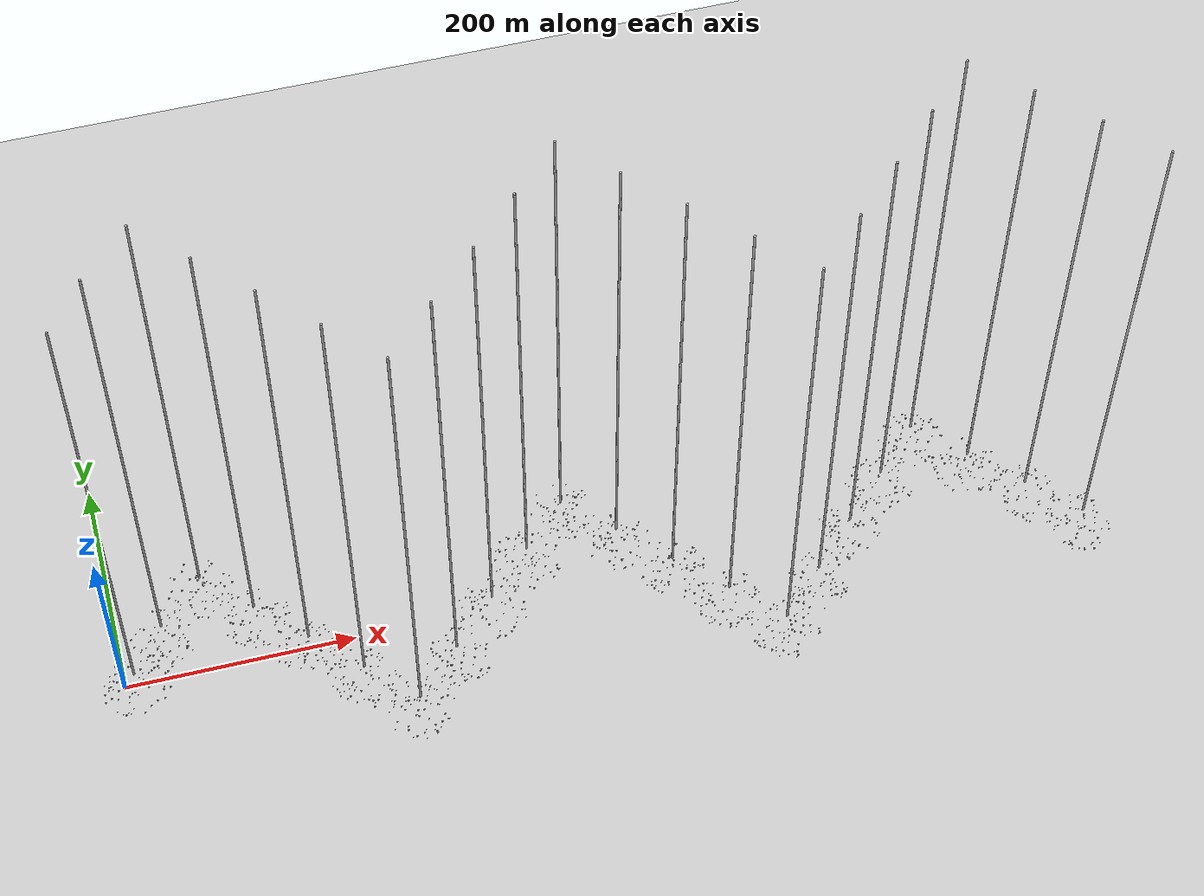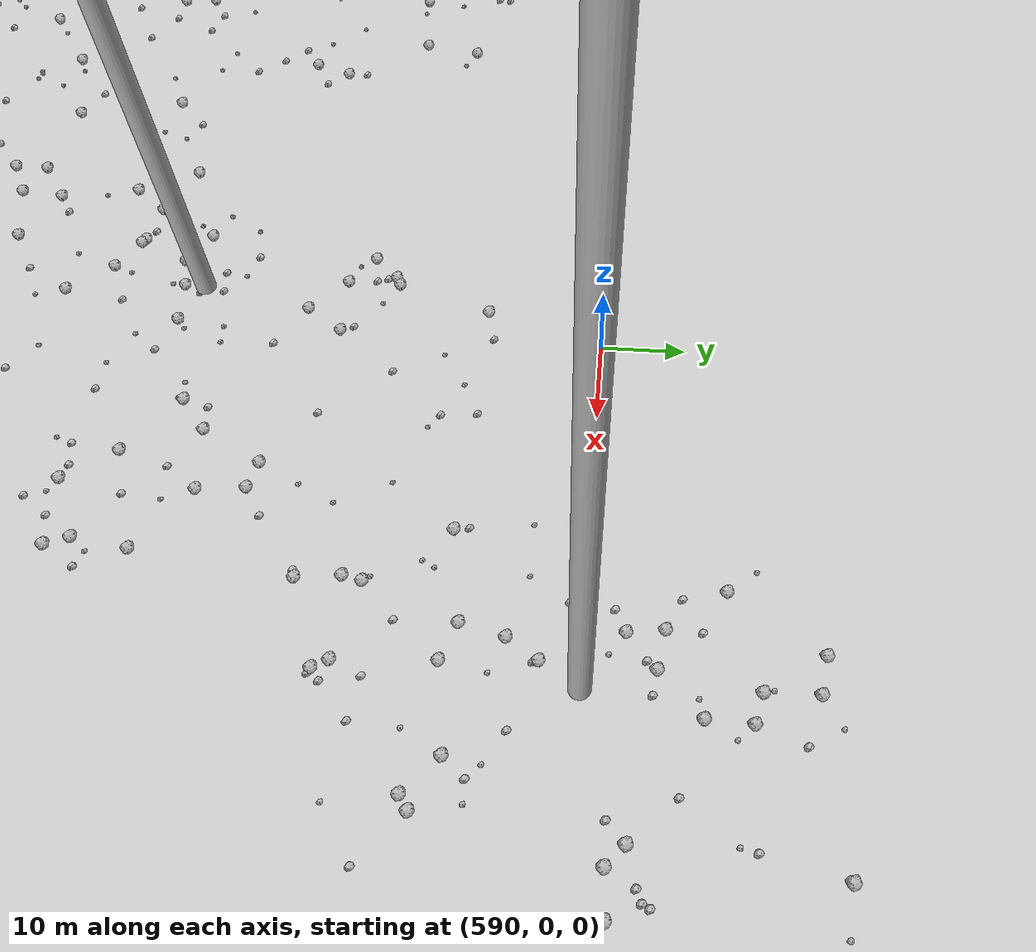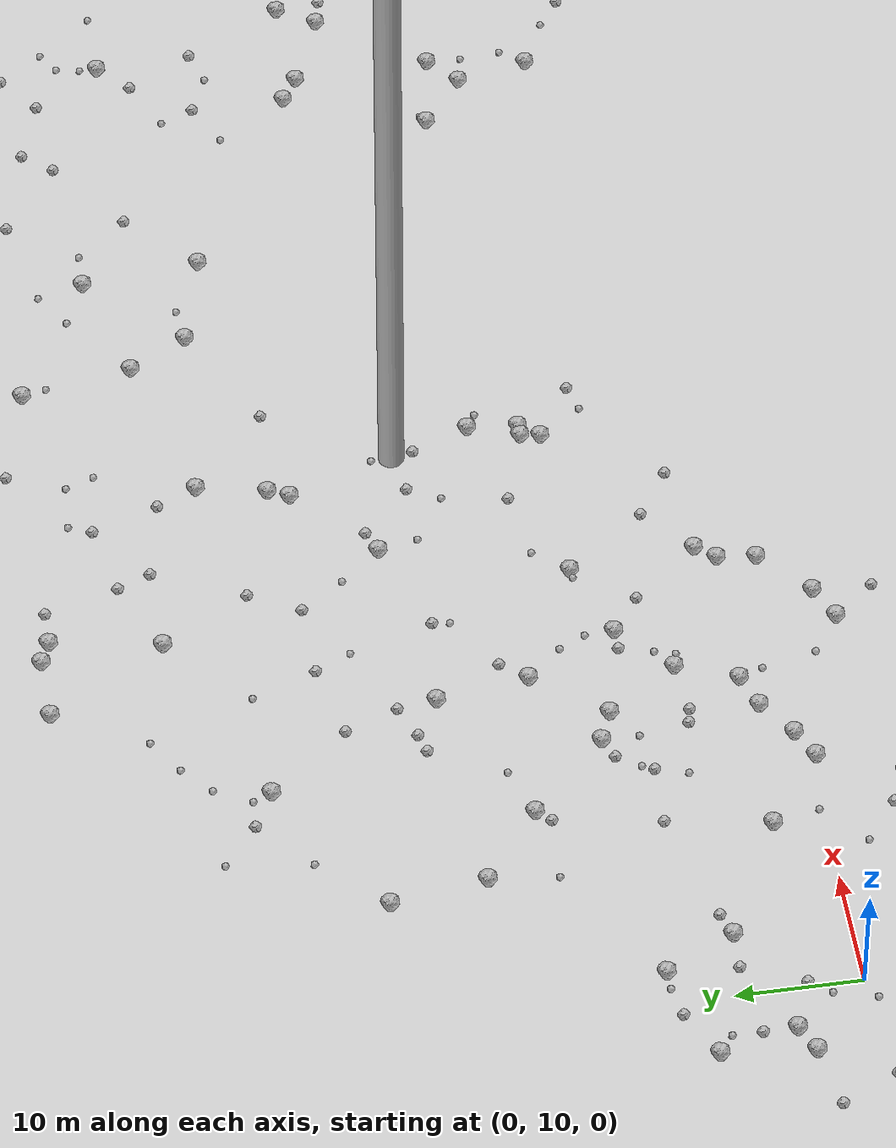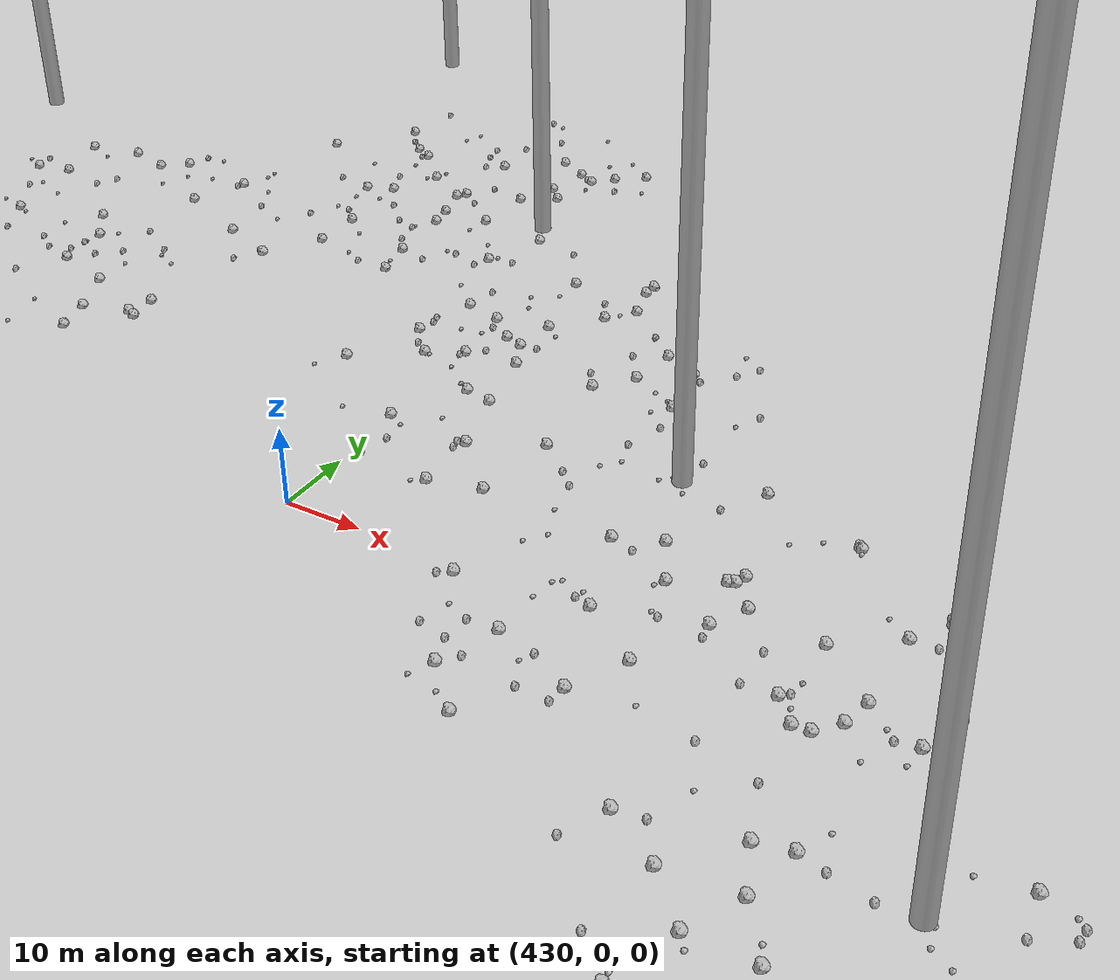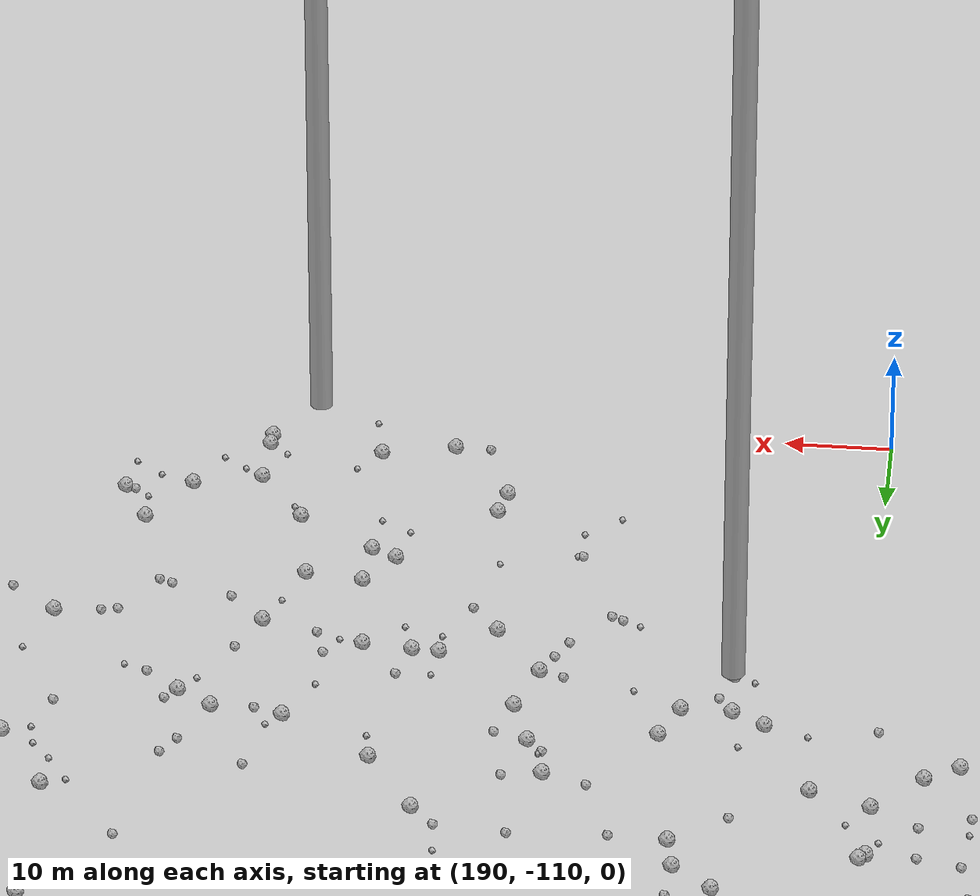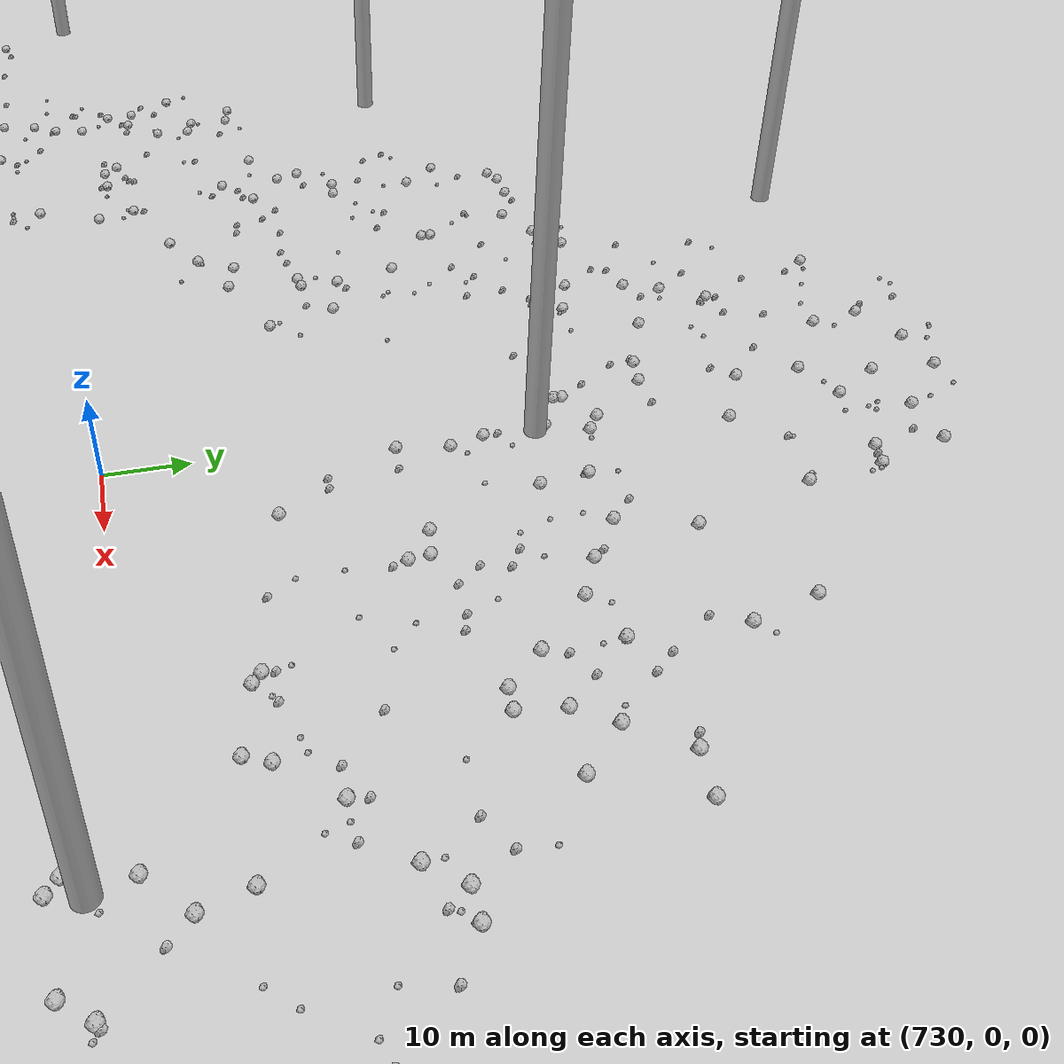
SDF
<sdf version="1.6">
 <world name="default">
  <include><uri>model://custom_ground</uri></include>
  <include><uri>model://sun</uri></include>
  <spherical_coordinates>
   <surface_model>EARTH_WGS84</surface_model>
   <latitude_deg>38.161479</latitude_deg>
   <longitude_deg>-122.454630</longitude_deg>
   <elevation>488.0</elevation>
   <heading_deg>90</heading_deg>
  </spherical_coordinates>
  <model name="rock1_0_0">
   <include><uri>model://rock1</uri><pose>-17.915404779759147 -10.806029402420169 0.5 0 0 0</pose></include>
  </model>
  <model name="rock1_0_1">
   <include><uri>model://rock1</uri><pose>2.9134768158623885 24.679286409674354 0.5 0 0 0</pose></include>
  </model>
  <model name="rock1_0_2">
   <include><uri>model://rock1</uri><pose>-3.705516055684562 15.855797608863426 0.5 0 0 0</pose></include>
  </model>
  <model name="rock1_0_3">
   <include><uri>model://rock1</uri><pose>37.64154435634173 -8.718711251509635 0.5 0 0 0</pose></include>
  </model>
  <model name="rock1_0_4">
   <include><uri>model://rock1</uri><pose>-5.951408935199577 14.798947788764977 0.5 0 0 0</pose></include>
  </model>
  <model name="rock1_0_5">
   <include><uri>model://rock1</uri><pose>38.308753995326875 6.773752560092902 0.5 0 0 0</pose></include>
  </model>
  <model name="rock1_0_6">
   <include><uri>model://rock1</uri><pose>35.434587126131646 5.417240247349774 0.5 0 0 0</pose></include>
  </model>
  <model name="rock1_0_7">
   <include><uri>model://rock1</uri><pose>21.824181921714406 9.603411171974464 0.5 0 0 0</pose></include>
  </model>
  <model name="rock1_0_8">
   <include><uri>model://rock1</uri><pose>5.700219949162072 19.074657103640376 0.5 0 0 0</pose></include>
  </model>
  <model name="rock1_0_9">
   <include><uri>model://rock1</uri><pose>15.765515057922912 14.105280686788973 0.5 0 0 0</pose></include>
  </model>
  <model name="rock1_0_10">
   <include><uri>model://rock1</uri><pose>31.768130179791243 -9.35963275134776 0.5 0 0 0</pose></include>
  </model>
  <model name="rock1_0_11">
   <include><uri>model://rock1</uri><pose>7.6408392003457415 -6.62398424471861 0.5 0 0 0</pose></include>
  </model>
  <model name="rock1_0_12">
   <include><uri>model://rock1</uri><pose>-12.808781390569328 2.8477196562167535 0.5 0 0 0</pose></include>
  </model>
  <model name="rock1_0_13">
   <include><uri>model://rock1</uri><pose>31.482870572075868 -17.985838286660425 0.5 0 0 0</pose></include>
  </model>
  <model name="rock1_0_14">
   <include><uri>model://rock1</uri><pose>-3.100586573590011 -26.39039809620051 0.5 0 0 0</pose></include>
  </model>
  <model name="rock1_0_15">
   <include><uri>model://rock1</uri><pose>18.887100328799875 -22.239854302606826 0.5 0 0 0</pose></include>
  </model>
  <model name="rock1_0_16">
   <include><uri>model://rock1</uri><pose>24.32207438233774 10.857487320000374 0.5 0 0 0</pose></include>
  </model>
  <model name="rock1_0_17">
   <include><uri>model://rock1</uri><pose>-5.554692438989559 -1.9125708159594481 0.5 0 0 0</pose></include>
  </model>
  <model name="rock1_0_18">
   <include><uri>model://rock1</uri><pose>-17.429728130830412 -3.301483436276861 0.5 0 0 0</pose></include>
  </model>
  <model name="rock1_0_19">
   <include><uri>model://rock1</uri><pose>25.086317144791096 -18.799839926142234 0.5 0 0 0</pose></include>
  </model>
  <model name="rock1_0_20">
   <include><uri>model://rock1</uri><pose>-5.732147861724357 6.444066927411001 0.5 0 0 0</pose></include>
  </model>
  <model name="rock1_0_21">
   <include><uri>model://rock1</uri><pose>4.940531705244609 -7.321453776041903 0.5 0 0 0</pose></include>
  </model>
  <model name="rock1_0_22">
   <include><uri>model://rock1</uri><pose>27.464352516778582 13.050335052906775 0.5 0 0 0</pose></include>
  </model>
  <model name="rock1_0_23">
   <include><uri>model://rock1</uri><pose>-5.163921175274442 22.039840157796313 0.5 0 0 0</pose></include>
  </model>
  <model name="rock1_0_24">
   <include><uri>model://rock1</uri><pose>12.957842016554736 -27.634805316818937 0.5 0 0 0</pose></include>
  </model>
  <model name="rock1_0_25">
   <include><uri>model://rock1</uri><pose>-13.938599539077918 -0.19528708638218717 0.5 0 0 0</pose></include>
  </model>
  <model name="rock1_0_26">
   <include><uri>model://rock1</uri><pose>-12.446186286647102 -7.804175507952511 0.5 0 0 0</pose></include>
  </model>
  <model name="rock2_0_0">
   <include><uri>model://rock2</uri><pose>-7.381698312688398 -10.009308858674192 0.3 0 0 0</pose></include>
  </model>
  <model name="rock2_0_1">
   <include><uri>model://rock2</uri><pose>9.436453387917858 -9.326652428812462 0.3 0 0 0</pose></include>
  </model>
  <model name="rock2_0_2">
   <include><uri>model://rock2</uri><pose>7.603731748901378 19.735399528841832 0.3 0 0 0</pose></include>
  </model>
  <model name="rock2_0_3">
   <include><uri>model://rock2</uri><pose>-1.270191283398244 24.11665229018641 0.3 0 0 0</pose></include>
  </model>
  <model name="rock2_0_4">
   <include><uri>model://rock2</uri><pose>-8.08683942244915 7.93322161906589 0.3 0 0 0</pose></include>
  </model>
  <model name="rock2_0_5">
   <include><uri>model://rock2</uri><pose>-3.772994763254271 18.486835318943086 0.3 0 0 0</pose></include>
  </model>
  <model name="rock2_0_6">
   <include><uri>model://rock2</uri><pose>-10.42603133991857 0.4157483828914508 0.3 0 0 0</pose></include>
  </model>
  <model name="rock2_0_7">
   <include><uri>model://rock2</uri><pose>38.082482791660105 2.037889189184895 0.3 0 0 0</pose></include>
  </model>
  <model name="rock2_0_8">
   <include><uri>model://rock2</uri><pose>-11.465794083890557 3.524127675324195 0.3 0 0 0</pose></include>
  </model>
  <model name="rock2_0_9">
   <include><uri>model://rock2</uri><pose>-5.327820094276166 7.43781459586959 0.3 0 0 0</pose></include>
  </model>
  <model name="rock2_0_10">
   <include><uri>model://rock2</uri><pose>17.141164262573973 22.349643652693423 0.3 0 0 0</pose></include>
  </model>
  <model name="rock2_0_11">
   <include><uri>model://rock2</uri><pose>26.500757212661988 18.756590823409475 0.3 0 0 0</pose></include>
  </model>
  <model name="rock2_0_12">
   <include><uri>model://rock2</uri><pose>-11.157665194109576 13.80779199497119 0.3 0 0 0</pose></include>
  </model>
  <model name="rock2_0_13">
   <include><uri>model://rock2</uri><pose>-8.999601979666714 9.19882113775622 0.3 0 0 0</pose></include>
  </model>
  <model name="rock2_0_14">
   <include><uri>model://rock2</uri><pose>-1.1600595928010975 -24.834326786239863 0.3 0 0 0</pose></include>
  </model>
  <model name="rock2_0_15">
   <include><uri>model://rock2</uri><pose>1.0496747323392484 -26.1401671699154 0.3 0 0 0</pose></include>
  </model>
  <model name="rock2_0_16">
   <include><uri>model://rock2</uri><pose>24.008757408986078 24.98376965410145 0.3 0 0 0</pose></include>
  </model>
  <model name="rock2_0_17">
   <include><uri>model://rock2</uri><pose>27.78649872567197 18.47477366144186 0.3 0 0 0</pose></include>
  </model>
  <model name="rock2_0_18">
   <include><uri>model://rock2</uri><pose>0.3490646558229713 14.310133800852881 0.3 0 0 0</pose></include>
  </model>
  <model name="rock2_0_19">
   <include><uri>model://rock2</uri><pose>21.905756854306205 -2.4931369859961237 0.3 0 0 0</pose></include>
  </model>
  <model name="rock2_0_20">
   <include><uri>model://rock2</uri><pose>32.528781950174206 -7.059897898410192 0.3 0 0 0</pose></include>
  </model>
  <model name="rock2_0_21">
   <include><uri>model://rock2</uri><pose>-5.33157113084612 6.559916064209112 0.3 0 0 0</pose></include>
  </model>
  <model name="rock2_0_22">
   <include><uri>model://rock2</uri><pose>30.69888750343683 0.8715522596124714 0.3 0 0 0</pose></include>
  </model>
  <model name="rock2_0_23">
   <include><uri>model://rock2</uri><pose>19.898680970585062 -4.193612493056158 0.3 0 0 0</pose></include>
  </model>
  <model name="rock2_0_24">
   <include><uri>model://rock2</uri><pose>16.40228246426311 4.4598856183868705 0.3 0 0 0</pose></include>
  </model>
  <model name="rock2_0_25">
   <include><uri>model://rock2</uri><pose>2.4652573938654783 19.143670955984 0.3 0 0 0</pose></include>
  </model>
  <model name="rock2_0_26">
   <include><uri>model://rock2</uri><pose>2.3087428661384983 -9.714995238402945 0.3 0 0 0</pose></include>
  </model>
  <model name="rock3_0_0">
   <include><uri>model://rock3</uri><pose>-3.934836338782226 -9.1661398082013 0.2 0 0 0</pose></include>
  </model>
  <model name="rock3_0_1">
   <include><uri>model://rock3</uri><pose>18.324956722576665 -3.7846010518416477 0.2 0 0 0</pose></include>
  </model>
  <model name="rock3_0_2">
   <include><uri>model://rock3</uri><pose>20.694548294289795 -16.707713659507952 0.2 0 0 0</pose></include>
  </model>
  <model name="rock3_0_3">
   <include><uri>model://rock3</uri><pose>-1.8231470996980192 9.240548230919352 0.2 0 0 0</pose></include>
  </model>
  <model name="rock3_0_4">
   <include><uri>model://rock3</uri><pose>3.463788120244253 0.33245987227267904 0.2 0 0 0</pose></include>
  </model>
  <model name="rock3_0_5">
   <include><uri>model://rock3</uri><pose>33.49976979422271 18.509316721601266 0.2 0 0 0</pose></include>
  </model>
  <model name="rock3_0_6">
   <include><uri>model://rock3</uri><pose>13.028278861214673 7.053803676790409 0.2 0 0 0</pose></include>
  </model>
  <model name="rock3_0_7">
   <include><uri>model://rock3</uri><pose>6.9692317602007705 -20.436744161566637 0.2 0 0 0</pose></include>
  </model>
  <model name="rock3_0_8">
   <include><uri>model://rock3</uri><pose>16.52677278529721 10.29660343689499 0.2 0 0 0</pose></include>
  </model>
  <model name="rock3_0_9">
   <include><uri>model://rock3</uri><pose>-3.6997994233785434 20.80443742855941 0.2 0 0 0</pose></include>
  </model>
  <model name="rock3_0_10">
   <include><uri>model://rock3</uri><pose>1.2932564304546688 24.601269103559908 0.2 0 0 0</pose></include>
  </model>
  <model name="rock3_0_11">
   <include><uri>model://rock3</uri><pose>19.606524699712345 3.4121110037940454 0.2 0 0 0</pose></include>
  </model>
  <model name="rock3_0_12">
   <include><uri>model://rock3</uri><pose>-3.760746797391562 -6.684947290951243 0.2 0 0 0</pose></include>
  </model>
  <model name="rock3_0_13">
   <include><uri>model://rock3</uri><pose>25.815844786685894 22.71612574017815 0.2 0 0 0</pose></include>
  </model>
  <model name="rock3_0_14">
   <include><uri>model://rock3</uri><pose>12.418194844919924 -1.0729722542745392 0.2 0 0 0</pose></include>
  </model>
  <model name="rock3_0_15">
   <include><uri>model://rock3</uri><pose>-12.027496017616139 8.591550813186515 0.2 0 0 0</pose></include>
  </model>
  <model name="rock3_0_16">
   <include><uri>model://rock3</uri><pose>-5.561048120024797 -0.7781075618353803 0.2 0 0 0</pose></include>
  </model>
  <model name="rock3_0_17">
   <include><uri>model://rock3</uri><pose>-4.946746090570318 -2.024615514938521 0.2 0 0 0</pose></include>
  </model>
  <model name="rock3_0_18">
   <include><uri>model://rock3</uri><pose>-9.924481976728938 -21.714439787291358 0.2 0 0 0</pose></include>
  </model>
  <model name="rock3_0_19">
   <include><uri>model://rock3</uri><pose>22.811816280015265 23.065503309377128 0.2 0 0 0</pose></include>
  </model>
  <model name="rock3_0_20">
   <include><uri>model://rock3</uri><pose>1.492072875778124 -15.368342351961765 0.2 0 0 0</pose></include>
  </model>
  <model name="rock3_0_21">
   <include><uri>model://rock3</uri><pose>32.08286133347873 7.59197460030007 0.2 0 0 0</pose></include>
  </model>
  <model name="rock3_0_22">
   <include><uri>model://rock3</uri><pose>9.296548587458663 -27.123280036525045 0.2 0 0 0</pose></include>
  </model>
  <model name="rock3_0_23">
   <include><uri>model://rock3</uri><pose>-0.8998751206533093 12.582622273772863 0.2 0 0 0</pose></include>
  </model>
  <model name="rock3_0_24">
   <include><uri>model://rock3</uri><pose>-5.364684860773451 -25.416894265212452 0.2 0 0 0</pose></include>
  </model>
  <model name="rock3_0_25">
   <include><uri>model://rock3</uri><pose>3.7107618172026626 -21.808583358617682 0.2 0 0 0</pose></include>
  </model>
  <model name="rock3_0_26">
   <include><uri>model://rock3</uri><pose>-16.722581685919447 5.754181644185124 0.2 0 0 0</pose></include>
  </model>
  <model name="rock1_1_0">
   <include><uri>model://rock1</uri><pose>59.356933262627585 31.08037869083029 0.5 0 0 0</pose></include>
  </model>
  <model name="rock1_1_1">
   <include><uri>model://rock1</uri><pose>32.278462508885255 18.916058276301214 0.5 0 0 0</pose></include>
  </model>
  <model name="rock1_1_2">
   <include><uri>model://rock1</uri><pose>54.35470752289281 46.224174248707314 0.5 0 0 0</pose></include>
  </model>
  <model name="rock1_1_3">
   <include><uri>model://rock1</uri><pose>58.930414671895015 27.003814632540898 0.5 0 0 0</pose></include>
  </model>
  <model name="rock1_1_4">
   <include><uri>model://rock1</uri><pose>56.318178391541124 53.52083233266312 0.5 0 0 0</pose></include>
  </model>
  <model name="rock1_1_5">
   <include><uri>model://rock1</uri><pose>32.89182058554742 30.365742447320066 0.5 0 0 0</pose></include>
  </model>
  <model name="rock1_1_6">
   <include><uri>model://rock1</uri><pose>34.887577336091255 67.77378473410195 0.5 0 0 0</pose></include>
  </model>
  <model name="rock1_1_7">
   <include><uri>model://rock1</uri><pose>19.652719706152602 31.999366563351835 0.5 0 0 0</pose></include>
  </model>
  <model name="rock1_1_8">
   <include><uri>model://rock1</uri><pose>12.559732880556208 44.35745458599338 0.5 0 0 0</pose></include>
  </model>
  <model name="rock1_1_9">
   <include><uri>model://rock1</uri><pose>57.91828604046808 26.973150953377885 0.5 0 0 0</pose></include>
  </model>
  <model name="rock1_1_10">
   <include><uri>model://rock1</uri><pose>57.62748086097367 25.37865986151848 0.5 0 0 0</pose></include>
  </model>
  <model name="rock1_1_11">
   <include><uri>model://rock1</uri><pose>30.357513451143653 14.079796005584663 0.5 0 0 0</pose></include>
  </model>
  <model name="rock1_1_12">
   <include><uri>model://rock1</uri><pose>40.26395010416188 67.83599952611286 0.5 0 0 0</pose></include>
  </model>
  <model name="rock1_1_13">
   <include><uri>model://rock1</uri><pose>28.487445624737905 24.687994071452927 0.5 0 0 0</pose></include>
  </model>
  <model name="rock1_1_14">
   <include><uri>model://rock1</uri><pose>36.5638446300926 22.97027435794169 0.5 0 0 0</pose></include>
  </model>
  <model name="rock1_1_15">
   <include><uri>model://rock1</uri><pose>42.78653414973002 13.652024911350507 0.5 0 0 0</pose></include>
  </model>
  <model name="rock1_1_16">
   <include><uri>model://rock1</uri><pose>25.852845122303126 25.766778482050384 0.5 0 0 0</pose></include>
  </model>
  <model name="rock1_1_17">
   <include><uri>model://rock1</uri><pose>44.06798153269182 15.247829404829192 0.5 0 0 0</pose></include>
  </model>
  <model name="rock1_1_18">
   <include><uri>model://rock1</uri><pose>42.37712012944186 10.537444490850794 0.5 0 0 0</pose></include>
  </model>
  <model name="rock1_1_19">
   <include><uri>model://rock1</uri><pose>24.586277431046128 51.80307662172268 0.5 0 0 0</pose></include>
  </model>
  <model name="rock1_1_20">
   <include><uri>model://rock1</uri><pose>47.64564738632276 40.04902212102999 0.5 0 0 0</pose></include>
  </model>
  <model name="rock1_1_21">
   <include><uri>model://rock1</uri><pose>40.60840141192237 58.19604127458623 0.5 0 0 0</pose></include>
  </model>
  <model name="rock1_1_22">
   <include><uri>model://rock1</uri><pose>42.133518307592915 67.03828584532103 0.5 0 0 0</pose></include>
  </model>
  <model name="rock1_1_23">
   <include><uri>model://rock1</uri><pose>31.777947154825455 37.81294536872545 0.5 0 0 0</pose></include>
  </model>
  <model name="rock1_1_24">
   <include><uri>model://rock1</uri><pose>13.733097343394947 36.6301545853884 0.5 0 0 0</pose></include>
  </model>
  <model name="rock1_1_25">
   <include><uri>model://rock1</uri><pose>55.10740192270984 47.915991559879004 0.5 0 0 0</pose></include>
  </model>
  <model name="rock1_1_26">
   <include><uri>model://rock1</uri><pose>43.285671691780855 25.370458183848534 0.5 0 0 0</pose></include>
  </model>
  <model name="rock2_1_0">
   <include><uri>model://rock2</uri><pose>49.50462057301499 40.79608842895446 0.3 0 0 0</pose></include>
  </model>
  <model name="rock2_1_1">
   <include><uri>model://rock2</uri><pose>21.442967180316174 53.461879503820526 0.3 0 0 0</pose></include>
  </model>
  <model name="rock2_1_2">
   <include><uri>model://rock2</uri><pose>47.88164250771851 58.27177014474387 0.3 0 0 0</pose></include>
  </model>
  <model name="rock2_1_3">
   <include><uri>model://rock2</uri><pose>18.580687835797747 30.86515790317072 0.3 0 0 0</pose></include>
  </model>
  <model name="rock2_1_4">
   <include><uri>model://rock2</uri><pose>57.460074218014235 35.78622837904363 0.3 0 0 0</pose></include>
  </model>
  <model name="rock2_1_5">
   <include><uri>model://rock2</uri><pose>39.55983417117143 20.647563151605755 0.3 0 0 0</pose></include>
  </model>
  <model name="rock2_1_6">
   <include><uri>model://rock2</uri><pose>62.30123689624477 22.436758639225076 0.3 0 0 0</pose></include>
  </model>
  <model name="rock2_1_7">
   <include><uri>model://rock2</uri><pose>45.07180938715323 66.98711572435519 0.3 0 0 0</pose></include>
  </model>
  <model name="rock2_1_8">
   <include><uri>model://rock2</uri><pose>26.78511583966567 39.29773995431911 0.3 0 0 0</pose></include>
  </model>
  <model name="rock2_1_9">
   <include><uri>model://rock2</uri><pose>52.106135167203675 16.17316171510695 0.3 0 0 0</pose></include>
  </model>
  <model name="rock2_1_10">
   <include><uri>model://rock2</uri><pose>52.95620545893742 62.25673714298404 0.3 0 0 0</pose></include>
  </model>
  <model name="rock2_1_11">
   <include><uri>model://rock2</uri><pose>44.53990400515275 50.98685977796007 0.3 0 0 0</pose></include>
  </model>
  <model name="rock2_1_12">
   <include><uri>model://rock2</uri><pose>48.08552442686787 18.827966098780188 0.3 0 0 0</pose></include>
  </model>
  <model name="rock2_1_13">
   <include><uri>model://rock2</uri><pose>53.570010752055076 36.88112782705076 0.3 0 0 0</pose></include>
  </model>
  <model name="rock2_1_14">
   <include><uri>model://rock2</uri><pose>51.35502240791006 28.985518545859545 0.3 0 0 0</pose></include>
  </model>
  <model name="rock2_1_15">
   <include><uri>model://rock2</uri><pose>63.077979861992006 47.37437523006204 0.3 0 0 0</pose></include>
  </model>
  <model name="rock2_1_16">
   <include><uri>model://rock2</uri><pose>34.69697614083143 22.910587211883993 0.3 0 0 0</pose></include>
  </model>
  <model name="rock2_1_17">
   <include><uri>model://rock2</uri><pose>42.37900487595874 46.900202825066025 0.3 0 0 0</pose></include>
  </model>
  <model name="rock2_1_18">
   <include><uri>model://rock2</uri><pose>22.303277528345582 22.179076226892967 0.3 0 0 0</pose></include>
  </model>
  <model name="rock2_1_19">
   <include><uri>model://rock2</uri><pose>46.7887295078024 60.97696447975449 0.3 0 0 0</pose></include>
  </model>
  <model name="rock2_1_20">
   <include><uri>model://rock2</uri><pose>29.66406022093386 45.28513074442759 0.3 0 0 0</pose></include>
  </model>
  <model name="rock2_1_21">
   <include><uri>model://rock2</uri><pose>28.46131154265083 39.76749241688441 0.3 0 0 0</pose></include>
  </model>
  <model name="rock2_1_22">
   <include><uri>model://rock2</uri><pose>36.03526673783537 46.715537536344776 0.3 0 0 0</pose></include>
  </model>
  <model name="rock2_1_23">
   <include><uri>model://rock2</uri><pose>39.472863573196776 36.96970724391893 0.3 0 0 0</pose></include>
  </model>
  <model name="rock2_1_24">
   <include><uri>model://rock2</uri><pose>54.82404595624468 56.81398954578066 0.3 0 0 0</pose></include>
  </model>
  <model name="rock2_1_25">
   <include><uri>model://rock2</uri><pose>31.29449806789974 40.97519624950064 0.3 0 0 0</pose></include>
  </model>
  <model name="rock2_1_26">
   <include><uri>model://rock2</uri><pose>34.52350824802967 32.438821159335845 0.3 0 0 0</pose></include>
  </model>
  <model name="rock3_1_0">
   <include><uri>model://rock3</uri><pose>52.27450777427361 34.21479973453779 0.2 0 0 0</pose></include>
  </model>
  <model name="rock3_1_1">
   <include><uri>model://rock3</uri><pose>17.170445660437856 49.46677274077152 0.2 0 0 0</pose></include>
  </model>
  <model name="rock3_1_2">
   <include><uri>model://rock3</uri><pose>42.463019542657676 25.209456760786797 0.2 0 0 0</pose></include>
  </model>
  <model name="rock3_1_3">
   <include><uri>model://rock3</uri><pose>60.63550218155038 30.22039363944829 0.2 0 0 0</pose></include>
  </model>
  <model name="rock3_1_4">
   <include><uri>model://rock3</uri><pose>53.77709510646454 64.0713744152444 0.2 0 0 0</pose></include>
  </model>
  <model name="rock3_1_5">
   <include><uri>model://rock3</uri><pose>23.77585798717758 33.4374584982599 0.2 0 0 0</pose></include>
  </model>
  <model name="rock3_1_6">
   <include><uri>model://rock3</uri><pose>57.03329880522003 39.17122587911713 0.2 0 0 0</pose></include>
  </model>
  <model name="rock3_1_7">
   <include><uri>model://rock3</uri><pose>18.052058551086816 56.235370098102365 0.2 0 0 0</pose></include>
  </model>
  <model name="rock3_1_8">
   <include><uri>model://rock3</uri><pose>13.089099632392676 31.104102293294595 0.2 0 0 0</pose></include>
  </model>
  <model name="rock3_1_9">
   <include><uri>model://rock3</uri><pose>60.01647256621227 21.749998976891206 0.2 0 0 0</pose></include>
  </model>
  <model name="rock3_1_10">
   <include><uri>model://rock3</uri><pose>21.601049641517264 19.571418614064065 0.2 0 0 0</pose></include>
  </model>
  <model name="rock3_1_11">
   <include><uri>model://rock3</uri><pose>34.10856742847693 51.925240869613404 0.2 0 0 0</pose></include>
  </model>
  <model name="rock3_1_12">
   <include><uri>model://rock3</uri><pose>37.45315581280734 43.74626247578874 0.2 0 0 0</pose></include>
  </model>
  <model name="rock3_1_13">
   <include><uri>model://rock3</uri><pose>36.44596107071787 25.274551965655967 0.2 0 0 0</pose></include>
  </model>
  <model name="rock3_1_14">
   <include><uri>model://rock3</uri><pose>30.902744948266257 60.38791575560154 0.2 0 0 0</pose></include>
  </model>
  <model name="rock3_1_15">
   <include><uri>model://rock3</uri><pose>35.3772118959354 27.427422505067625 0.2 0 0 0</pose></include>
  </model>
  <model name="rock3_1_16">
   <include><uri>model://rock3</uri><pose>57.8604333854373 63.74982847638828 0.2 0 0 0</pose></include>
  </model>
  <model name="rock3_1_17">
   <include><uri>model://rock3</uri><pose>45.50636346892062 28.03437978638805 0.2 0 0 0</pose></include>
  </model>
  <model name="rock3_1_18">
   <include><uri>model://rock3</uri><pose>33.989500968366016 20.15528628949968 0.2 0 0 0</pose></include>
  </model>
  <model name="rock3_1_19">
   <include><uri>model://rock3</uri><pose>39.33618125365972 35.531907171238544 0.2 0 0 0</pose></include>
  </model>
  <model name="rock3_1_20">
   <include><uri>model://rock3</uri><pose>25.463585701308222 56.21638888328601 0.2 0 0 0</pose></include>
  </model>
  <model name="rock3_1_21">
   <include><uri>model://rock3</uri><pose>58.73158616942664 61.441519501471184 0.2 0 0 0</pose></include>
  </model>
  <model name="rock3_1_22">
   <include><uri>model://rock3</uri><pose>31.042405998995463 12.043971766690904 0.2 0 0 0</pose></include>
  </model>
  <model name="rock3_1_23">
   <include><uri>model://rock3</uri><pose>44.86358062837221 43.317299669085536 0.2 0 0 0</pose></include>
  </model>
  <model name="rock3_1_24">
   <include><uri>model://rock3</uri><pose>23.92747776150327 53.26917715589786 0.2 0 0 0</pose></include>
  </model>
  <model name="rock3_1_25">
   <include><uri>model://rock3</uri><pose>48.27844255865996 36.752346483822976 0.2 0 0 0</pose></include>
  </model>
  <model name="rock3_1_26">
   <include><uri>model://rock3</uri><pose>27.882065042861193 58.394042773586314 0.2 0 0 0</pose></include>
  </model>
  <model name="rock1_2_0">
   <include><uri>model://rock1</uri><pose>63.190326894585844 82.24454443399046 0.5 0 0 0</pose></include>
  </model>
  <model name="rock1_2_1">
   <include><uri>model://rock1</uri><pose>74.79710992690957 77.59319605356785 0.5 0 0 0</pose></include>
  </model>
  <model name="rock1_2_2">
   <include><uri>model://rock1</uri><pose>99.91743921252788 77.7219992806588 0.5 0 0 0</pose></include>
  </model>
  <model name="rock1_2_3">
   <include><uri>model://rock1</uri><pose>77.20958940051355 92.05465844932036 0.5 0 0 0</pose></include>
  </model>
  <model name="rock1_2_4">
   <include><uri>model://rock1</uri><pose>58.77158183221681 94.93565376277228 0.5 0 0 0</pose></include>
  </model>
  <model name="rock1_2_5">
   <include><uri>model://rock1</uri><pose>91.32920222519547 67.42970050325246 0.5 0 0 0</pose></include>
  </model>
  <model name="rock1_2_6">
   <include><uri>model://rock1</uri><pose>83.21398101850025 90.46972679411081 0.5 0 0 0</pose></include>
  </model>
  <model name="rock1_2_7">
   <include><uri>model://rock1</uri><pose>93.00950150012713 102.9252356026365 0.5 0 0 0</pose></include>
  </model>
  <model name="rock1_2_8">
   <include><uri>model://rock1</uri><pose>54.522489449282034 83.2357916352747 0.5 0 0 0</pose></include>
  </model>
  <model name="rock1_2_9">
   <include><uri>model://rock1</uri><pose>101.26367336216695 90.2481627295308 0.5 0 0 0</pose></include>
  </model>
  <model name="rock1_2_10">
   <include><uri>model://rock1</uri><pose>51.02732991309231 77.43690342835365 0.5 0 0 0</pose></include>
  </model>
  <model name="rock1_2_11">
   <include><uri>model://rock1</uri><pose>67.98312258418056 71.53724481451829 0.5 0 0 0</pose></include>
  </model>
  <model name="rock1_2_12">
   <include><uri>model://rock1</uri><pose>82.25427093014684 82.44756786579117 0.5 0 0 0</pose></include>
  </model>
  <model name="rock1_2_13">
   <include><uri>model://rock1</uri><pose>71.91872004253518 91.70351789036597 0.5 0 0 0</pose></include>
  </model>
  <model name="rock1_2_14">
   <include><uri>model://rock1</uri><pose>69.81684351032251 57.077797271984636 0.5 0 0 0</pose></include>
  </model>
  <model name="rock1_2_15">
   <include><uri>model://rock1</uri><pose>83.65304905054282 75.86291138741134 0.5 0 0 0</pose></include>
  </model>
  <model name="rock1_2_16">
   <include><uri>model://rock1</uri><pose>79.65850859418595 59.81872117891423 0.5 0 0 0</pose></include>
  </model>
  <model name="rock1_2_17">
   <include><uri>model://rock1</uri><pose>83.35210914206195 85.03466942481981 0.5 0 0 0</pose></include>
  </model>
  <model name="rock1_2_18">
   <include><uri>model://rock1</uri><pose>68.22173706642535 66.12821951308018 0.5 0 0 0</pose></include>
  </model>
  <model name="rock1_2_19">
   <include><uri>model://rock1</uri><pose>80.63962389596219 50.15358913029644 0.5 0 0 0</pose></include>
  </model>
  <model name="rock1_2_20">
   <include><uri>model://rock1</uri><pose>72.50625108595878 52.292174531578915 0.5 0 0 0</pose></include>
  </model>
  <model name="rock1_2_21">
   <include><uri>model://rock1</uri><pose>92.1441657705214 79.948244012322 0.5 0 0 0</pose></include>
  </model>
  <model name="rock1_2_22">
   <include><uri>model://rock1</uri><pose>77.28674546150897 79.92997213193095 0.5 0 0 0</pose></include>
  </model>
  <model name="rock1_2_23">
   <include><uri>model://rock1</uri><pose>86.38524979560043 96.25867621884389 0.5 0 0 0</pose></include>
  </model>
  <model name="rock1_2_24">
   <include><uri>model://rock1</uri><pose>78.06610793890012 89.13418675624419 0.5 0 0 0</pose></include>
  </model>
  <model name="rock1_2_25">
   <include><uri>model://rock1</uri><pose>69.15289018920433 107.7788108962771 0.5 0 0 0</pose></include>
  </model>
  <model name="rock1_2_26">
   <include><uri>model://rock1</uri><pose>106.88541707156651 80.77962254605615 0.5 0 0 0</pose></include>
  </model>
  <model name="rock2_2_0">
   <include><uri>model://rock2</uri><pose>79.577268670459 101.59912056838925 0.3 0 0 0</pose></include>
  </model>
  <model name="rock2_2_1">
   <include><uri>model://rock2</uri><pose>96.52098799398865 70.59383046461465 0.3 0 0 0</pose></include>
  </model>
  <model name="rock2_2_2">
   <include><uri>model://rock2</uri><pose>106.90009511840677 80.16595783499336 0.3 0 0 0</pose></include>
  </model>
  <model name="rock2_2_3">
   <include><uri>model://rock2</uri><pose>86.79191739104647 65.27392412442943 0.3 0 0 0</pose></include>
  </model>
  <model name="rock2_2_4">
   <include><uri>model://rock2</uri><pose>88.2729973305597 83.94775246353933 0.3 0 0 0</pose></include>
  </model>
  <model name="rock2_2_5">
   <include><uri>model://rock2</uri><pose>104.06298389539386 68.61812702542073 0.3 0 0 0</pose></include>
  </model>
  <model name="rock2_2_6">
   <include><uri>model://rock2</uri><pose>81.50272055735061 84.0658079398612 0.3 0 0 0</pose></include>
  </model>
  <model name="rock2_2_7">
   <include><uri>model://rock2</uri><pose>105.6932971307601 87.74032658022729 0.3 0 0 0</pose></include>
  </model>
  <model name="rock2_2_8">
   <include><uri>model://rock2</uri><pose>70.99876948606911 73.75983229711954 0.3 0 0 0</pose></include>
  </model>
  <model name="rock2_2_9">
   <include><uri>model://rock2</uri><pose>55.627081508053 97.31643741387809 0.3 0 0 0</pose></include>
  </model>
  <model name="rock2_2_10">
   <include><uri>model://rock2</uri><pose>59.67503533548272 68.41282675586345 0.3 0 0 0</pose></include>
  </model>
  <model name="rock2_2_11">
   <include><uri>model://rock2</uri><pose>96.84663719747115 82.03094474468895 0.3 0 0 0</pose></include>
  </model>
  <model name="rock2_2_12">
   <include><uri>model://rock2</uri><pose>71.32195300322721 79.01585788946042 0.3 0 0 0</pose></include>
  </model>
  <model name="rock2_2_13">
   <include><uri>model://rock2</uri><pose>90.20470347459516 101.57819239366663 0.3 0 0 0</pose></include>
  </model>
  <model name="rock2_2_14">
   <include><uri>model://rock2</uri><pose>69.87225676157965 79.54778137788193 0.3 0 0 0</pose></include>
  </model>
  <model name="rock2_2_15">
   <include><uri>model://rock2</uri><pose>66.04987241689965 101.46471425592651 0.3 0 0 0</pose></include>
  </model>
  <model name="rock2_2_16">
   <include><uri>model://rock2</uri><pose>69.56245612256035 107.4039549372694 0.3 0 0 0</pose></include>
  </model>
  <model name="rock2_2_17">
   <include><uri>model://rock2</uri><pose>92.8500195809016 60.68842645878459 0.3 0 0 0</pose></include>
  </model>
  <model name="rock2_2_18">
   <include><uri>model://rock2</uri><pose>81.22329276410862 67.1199126158466 0.3 0 0 0</pose></include>
  </model>
  <model name="rock2_2_19">
   <include><uri>model://rock2</uri><pose>106.41889476565416 80.42454122328375 0.3 0 0 0</pose></include>
  </model>
  <model name="rock2_2_20">
   <include><uri>model://rock2</uri><pose>94.79552588107401 63.08355849777936 0.3 0 0 0</pose></include>
  </model>
  <model name="rock2_2_21">
   <include><uri>model://rock2</uri><pose>90.82107970810743 106.18204371644059 0.3 0 0 0</pose></include>
  </model>
  <model name="rock2_2_22">
   <include><uri>model://rock2</uri><pose>103.65541969439852 63.8419836984186 0.3 0 0 0</pose></include>
  </model>
  <model name="rock2_2_23">
   <include><uri>model://rock2</uri><pose>57.886707479116765 72.23895213565854 0.3 0 0 0</pose></include>
  </model>
  <model name="rock2_2_24">
   <include><uri>model://rock2</uri><pose>78.1468674009836 94.24340035649624 0.3 0 0 0</pose></include>
  </model>
  <model name="rock2_2_25">
   <include><uri>model://rock2</uri><pose>86.1333964990981 55.58811807820617 0.3 0 0 0</pose></include>
  </model>
  <model name="rock2_2_26">
   <include><uri>model://rock2</uri><pose>78.4826127872859 67.2284197092948 0.3 0 0 0</pose></include>
  </model>
  <model name="rock3_2_0">
   <include><uri>model://rock3</uri><pose>85.25172322361635 83.4766574775679 0.2 0 0 0</pose></include>
  </model>
  <model name="rock3_2_1">
   <include><uri>model://rock3</uri><pose>63.42915613036092 85.95806090887454 0.2 0 0 0</pose></include>
  </model>
  <model name="rock3_2_2">
   <include><uri>model://rock3</uri><pose>79.16404885080284 87.38581359037009 0.2 0 0 0</pose></include>
  </model>
  <model name="rock3_2_3">
   <include><uri>model://rock3</uri><pose>104.5762535230981 64.3988024816399 0.2 0 0 0</pose></include>
  </model>
  <model name="rock3_2_4">
   <include><uri>model://rock3</uri><pose>78.71805987140783 63.54832124017102 0.2 0 0 0</pose></include>
  </model>
  <model name="rock3_2_5">
   <include><uri>model://rock3</uri><pose>79.12010526124257 108.16970766390469 0.2 0 0 0</pose></include>
  </model>
  <model name="rock3_2_6">
   <include><uri>model://rock3</uri><pose>76.60797544380884 94.34716686170097 0.2 0 0 0</pose></include>
  </model>
  <model name="rock3_2_7">
   <include><uri>model://rock3</uri><pose>66.03049634966308 69.07388001631159 0.2 0 0 0</pose></include>
  </model>
  <model name="rock3_2_8">
   <include><uri>model://rock3</uri><pose>67.05580099453374 100.8209819063743 0.2 0 0 0</pose></include>
  </model>
  <model name="rock3_2_9">
   <include><uri>model://rock3</uri><pose>102.92806617096952 75.08892554130625 0.2 0 0 0</pose></include>
  </model>
  <model name="rock3_2_10">
   <include><uri>model://rock3</uri><pose>82.754546998047 59.69286686529417 0.2 0 0 0</pose></include>
  </model>
  <model name="rock3_2_11">
   <include><uri>model://rock3</uri><pose>75.50952239549225 52.565619098946684 0.2 0 0 0</pose></include>
  </model>
  <model name="rock3_2_12">
   <include><uri>model://rock3</uri><pose>81.53291635322162 86.17210912114865 0.2 0 0 0</pose></include>
  </model>
  <model name="rock3_2_13">
   <include><uri>model://rock3</uri><pose>74.80939263095756 96.40267270300359 0.2 0 0 0</pose></include>
  </model>
  <model name="rock3_2_14">
   <include><uri>model://rock3</uri><pose>85.58310285075832 86.46254026577265 0.2 0 0 0</pose></include>
  </model>
  <model name="rock3_2_15">
   <include><uri>model://rock3</uri><pose>94.41877339765696 87.98795870424223 0.2 0 0 0</pose></include>
  </model>
  <model name="rock3_2_16">
   <include><uri>model://rock3</uri><pose>89.07832038432062 70.32827592501029 0.2 0 0 0</pose></include>
  </model>
  <model name="rock3_2_17">
   <include><uri>model://rock3</uri><pose>64.36225124293773 85.66924202459285 0.2 0 0 0</pose></include>
  </model>
  <model name="rock3_2_18">
   <include><uri>model://rock3</uri><pose>68.68302461731146 64.08935701131506 0.2 0 0 0</pose></include>
  </model>
  <model name="rock3_2_19">
   <include><uri>model://rock3</uri><pose>80.90545971430117 102.81646909884029 0.2 0 0 0</pose></include>
  </model>
  <model name="rock3_2_20">
   <include><uri>model://rock3</uri><pose>55.80882335720201 73.93074346945374 0.2 0 0 0</pose></include>
  </model>
  <model name="rock3_2_21">
   <include><uri>model://rock3</uri><pose>101.36547697993186 69.88290371657997 0.2 0 0 0</pose></include>
  </model>
  <model name="rock3_2_22">
   <include><uri>model://rock3</uri><pose>89.04067806548719 83.55954600224698 0.2 0 0 0</pose></include>
  </model>
  <model name="rock3_2_23">
   <include><uri>model://rock3</uri><pose>93.45705731772236 102.57197246386082 0.2 0 0 0</pose></include>
  </model>
  <model name="rock3_2_24">
   <include><uri>model://rock3</uri><pose>75.64865198553605 61.55014173327075 0.2 0 0 0</pose></include>
  </model>
  <model name="rock3_2_25">
   <include><uri>model://rock3</uri><pose>88.82773407191368 71.09736749201679 0.2 0 0 0</pose></include>
  </model>
  <model name="rock3_2_26">
   <include><uri>model://rock3</uri><pose>59.271143299292646 90.91674331622201 0.2 0 0 0</pose></include>
  </model>
  <model name="rock1_3_0">
   <include><uri>model://rock1</uri><pose>136.3005108059727 32.284274223018684 0.5 0 0 0</pose></include>
  </model>
  <model name="rock1_3_1">
   <include><uri>model://rock1</uri><pose>98.03510473105791 40.60990084335283 0.5 0 0 0</pose></include>
  </model>
  <model name="rock1_3_2">
   <include><uri>model://rock1</uri><pose>149.22746864963136 37.908637425755344 0.5 0 0 0</pose></include>
  </model>
  <model name="rock1_3_3">
   <include><uri>model://rock1</uri><pose>111.71947298157993 19.610548500607585 0.5 0 0 0</pose></include>
  </model>
  <model name="rock1_3_4">
   <include><uri>model://rock1</uri><pose>127.55780399657388 48.18791601592831 0.5 0 0 0</pose></include>
  </model>
  <model name="rock1_3_5">
   <include><uri>model://rock1</uri><pose>146.12722854927043 37.36120538398583 0.5 0 0 0</pose></include>
  </model>
  <model name="rock1_3_6">
   <include><uri>model://rock1</uri><pose>131.39356258380587 48.30606332713131 0.5 0 0 0</pose></include>
  </model>
  <model name="rock1_3_7">
   <include><uri>model://rock1</uri><pose>103.95875711397856 55.67258214690043 0.5 0 0 0</pose></include>
  </model>
  <model name="rock1_3_8">
   <include><uri>model://rock1</uri><pose>135.971505768275 45.562742178393506 0.5 0 0 0</pose></include>
  </model>
  <model name="rock1_3_9">
   <include><uri>model://rock1</uri><pose>140.03108844804515 35.80431960206778 0.5 0 0 0</pose></include>
  </model>
  <model name="rock1_3_10">
   <include><uri>model://rock1</uri><pose>139.42899163449215 49.386375806664574 0.5 0 0 0</pose></include>
  </model>
  <model name="rock1_3_11">
   <include><uri>model://rock1</uri><pose>122.54724099507783 15.170515695042546 0.5 0 0 0</pose></include>
  </model>
  <model name="rock1_3_12">
   <include><uri>model://rock1</uri><pose>121.46723564509325 41.74266454709872 0.5 0 0 0</pose></include>
  </model>
  <model name="rock1_3_13">
   <include><uri>model://rock1</uri><pose>133.883606797709 46.024279198635035 0.5 0 0 0</pose></include>
  </model>
  <model name="rock1_3_14">
   <include><uri>model://rock1</uri><pose>113.59918251046068 27.15827566392853 0.5 0 0 0</pose></include>
  </model>
  <model name="rock1_3_15">
   <include><uri>model://rock1</uri><pose>118.45933060192586 22.315831727788492 0.5 0 0 0</pose></include>
  </model>
  <model name="rock1_3_16">
   <include><uri>model://rock1</uri><pose>100.20832027294179 39.26801148993551 0.5 0 0 0</pose></include>
  </model>
  <model name="rock1_3_17">
   <include><uri>model://rock1</uri><pose>136.84789802569458 21.863155843841604 0.5 0 0 0</pose></include>
  </model>
  <model name="rock1_3_18">
   <include><uri>model://rock1</uri><pose>109.02687875551993 64.04228365890626 0.5 0 0 0</pose></include>
  </model>
  <model name="rock1_3_19">
   <include><uri>model://rock1</uri><pose>136.16784235362462 37.00321405632706 0.5 0 0 0</pose></include>
  </model>
  <model name="rock1_3_20">
   <include><uri>model://rock1</uri><pose>108.52296090720526 39.74324474769259 0.5 0 0 0</pose></include>
  </model>
  <model name="rock1_3_21">
   <include><uri>model://rock1</uri><pose>99.25679073009213 19.843091723906447 0.5 0 0 0</pose></include>
  </model>
  <model name="rock1_3_22">
   <include><uri>model://rock1</uri><pose>93.6940305907101 29.116789317715263 0.5 0 0 0</pose></include>
  </model>
  <model name="rock1_3_23">
   <include><uri>model://rock1</uri><pose>106.61033745942139 36.641309464365435 0.5 0 0 0</pose></include>
  </model>
  <model name="rock1_3_24">
   <include><uri>model://rock1</uri><pose>97.99896573082559 25.73162007457104 0.5 0 0 0</pose></include>
  </model>
  <model name="rock1_3_25">
   <include><uri>model://rock1</uri><pose>123.4013584646693 46.19228666368126 0.5 0 0 0</pose></include>
  </model>
  <model name="rock1_3_26">
   <include><uri>model://rock1</uri><pose>100.51540917847187 28.023481737131053 0.5 0 0 0</pose></include>
  </model>
  <model name="rock2_3_0">
   <include><uri>model://rock2</uri><pose>140.90182587677108 49.97160615029054 0.3 0 0 0</pose></include>
  </model>
  <model name="rock2_3_1">
   <include><uri>model://rock2</uri><pose>114.47016844761333 16.74581337592377 0.3 0 0 0</pose></include>
  </model>
  <model name="rock2_3_2">
   <include><uri>model://rock2</uri><pose>138.21848238578986 21.453607722973477 0.3 0 0 0</pose></include>
  </model>
  <model name="rock2_3_3">
   <include><uri>model://rock2</uri><pose>100.23225374418602 61.22599241907186 0.3 0 0 0</pose></include>
  </model>
  <model name="rock2_3_4">
   <include><uri>model://rock2</uri><pose>127.17357234832733 12.132180280977625 0.3 0 0 0</pose></include>
  </model>
  <model name="rock2_3_5">
   <include><uri>model://rock2</uri><pose>134.8544326928202 29.728057289984648 0.3 0 0 0</pose></include>
  </model>
  <model name="rock2_3_6">
   <include><uri>model://rock2</uri><pose>104.30173135169946 47.77149187678359 0.3 0 0 0</pose></include>
  </model>
  <model name="rock2_3_7">
   <include><uri>model://rock2</uri><pose>121.57427172250928 65.52708648855042 0.3 0 0 0</pose></include>
  </model>
  <model name="rock2_3_8">
   <include><uri>model://rock2</uri><pose>101.34527795225644 53.185506186289224 0.3 0 0 0</pose></include>
  </model>
  <model name="rock2_3_9">
   <include><uri>model://rock2</uri><pose>134.98238991328174 41.60158470301206 0.3 0 0 0</pose></include>
  </model>
  <model name="rock2_3_10">
   <include><uri>model://rock2</uri><pose>126.70993955025159 58.57992166927161 0.3 0 0 0</pose></include>
  </model>
  <model name="rock2_3_11">
   <include><uri>model://rock2</uri><pose>116.49461908693661 54.50474024181001 0.3 0 0 0</pose></include>
  </model>
  <model name="rock2_3_12">
   <include><uri>model://rock2</uri><pose>145.26597523792526 44.88015347458237 0.3 0 0 0</pose></include>
  </model>
  <model name="rock2_3_13">
   <include><uri>model://rock2</uri><pose>99.9027234464443 31.417883138186625 0.3 0 0 0</pose></include>
  </model>
  <model name="rock2_3_14">
   <include><uri>model://rock2</uri><pose>100.26508258571911 39.03173859764875 0.3 0 0 0</pose></include>
  </model>
  <model name="rock2_3_15">
   <include><uri>model://rock2</uri><pose>115.24169605733059 11.257241262270469 0.3 0 0 0</pose></include>
  </model>
  <model name="rock2_3_16">
   <include><uri>model://rock2</uri><pose>109.23401983958769 19.360460378774427 0.3 0 0 0</pose></include>
  </model>
  <model name="rock2_3_17">
   <include><uri>model://rock2</uri><pose>108.92208596284704 36.088245612266405 0.3 0 0 0</pose></include>
  </model>
  <model name="rock2_3_18">
   <include><uri>model://rock2</uri><pose>121.53540476965779 26.877426850371155 0.3 0 0 0</pose></include>
  </model>
  <model name="rock2_3_19">
   <include><uri>model://rock2</uri><pose>105.88968738249963 16.051383758506493 0.3 0 0 0</pose></include>
  </model>
  <model name="rock2_3_20">
   <include><uri>model://rock2</uri><pose>114.15047814377847 36.87198992276718 0.3 0 0 0</pose></include>
  </model>
  <model name="rock2_3_21">
   <include><uri>model://rock2</uri><pose>148.3118500849537 49.08990323787868 0.3 0 0 0</pose></include>
  </model>
  <model name="rock2_3_22">
   <include><uri>model://rock2</uri><pose>97.96904407581282 48.323540408946485 0.3 0 0 0</pose></include>
  </model>
  <model name="rock2_3_23">
   <include><uri>model://rock2</uri><pose>137.13024706335668 37.06793405487213 0.3 0 0 0</pose></include>
  </model>
  <model name="rock2_3_24">
   <include><uri>model://rock2</uri><pose>117.84242839455761 20.11838621341995 0.3 0 0 0</pose></include>
  </model>
  <model name="rock2_3_25">
   <include><uri>model://rock2</uri><pose>117.8334781171238 65.89428686951283 0.3 0 0 0</pose></include>
  </model>
  <model name="rock2_3_26">
   <include><uri>model://rock2</uri><pose>113.56931362552193 48.80713920162725 0.3 0 0 0</pose></include>
  </model>
  <model name="rock3_3_0">
   <include><uri>model://rock3</uri><pose>125.64535505536354 11.353604819873436 0.2 0 0 0</pose></include>
  </model>
  <model name="rock3_3_1">
   <include><uri>model://rock3</uri><pose>118.05719901984537 68.43079480006601 0.2 0 0 0</pose></include>
  </model>
  <model name="rock3_3_2">
   <include><uri>model://rock3</uri><pose>138.6029857421985 52.91563521209086 0.2 0 0 0</pose></include>
  </model>
  <model name="rock3_3_3">
   <include><uri>model://rock3</uri><pose>96.88273538453282 51.02413153267533 0.2 0 0 0</pose></include>
  </model>
  <model name="rock3_3_4">
   <include><uri>model://rock3</uri><pose>109.87211953039683 55.66715637992662 0.2 0 0 0</pose></include>
  </model>
  <model name="rock3_3_5">
   <include><uri>model://rock3</uri><pose>114.44374065475338 54.5778360639738 0.2 0 0 0</pose></include>
  </model>
  <model name="rock3_3_6">
   <include><uri>model://rock3</uri><pose>135.48875210826407 30.399811635925406 0.2 0 0 0</pose></include>
  </model>
  <model name="rock3_3_7">
   <include><uri>model://rock3</uri><pose>110.64807629718729 22.16198041523146 0.2 0 0 0</pose></include>
  </model>
  <model name="rock3_3_8">
   <include><uri>model://rock3</uri><pose>104.05675134536136 57.05973154748047 0.2 0 0 0</pose></include>
  </model>
  <model name="rock3_3_9">
   <include><uri>model://rock3</uri><pose>103.43934219828148 17.764954064678896 0.2 0 0 0</pose></include>
  </model>
  <model name="rock3_3_10">
   <include><uri>model://rock3</uri><pose>101.35535478964583 46.7942237440439 0.2 0 0 0</pose></include>
  </model>
  <model name="rock3_3_11">
   <include><uri>model://rock3</uri><pose>104.45384342530437 59.01025344371758 0.2 0 0 0</pose></include>
  </model>
  <model name="rock3_3_12">
   <include><uri>model://rock3</uri><pose>100.48359532581168 25.10927243382913 0.2 0 0 0</pose></include>
  </model>
  <model name="rock3_3_13">
   <include><uri>model://rock3</uri><pose>127.61083703734111 45.64200184138856 0.2 0 0 0</pose></include>
  </model>
  <model name="rock3_3_14">
   <include><uri>model://rock3</uri><pose>106.26974794437274 60.16300132009769 0.2 0 0 0</pose></include>
  </model>
  <model name="rock3_3_15">
   <include><uri>model://rock3</uri><pose>127.72426955911274 67.7420989623529 0.2 0 0 0</pose></include>
  </model>
  <model name="rock3_3_16">
   <include><uri>model://rock3</uri><pose>129.41424869867697 47.457717320078594 0.2 0 0 0</pose></include>
  </model>
  <model name="rock3_3_17">
   <include><uri>model://rock3</uri><pose>121.84255223307416 12.861483790273095 0.2 0 0 0</pose></include>
  </model>
  <model name="rock3_3_18">
   <include><uri>model://rock3</uri><pose>148.57486564662733 45.78372136587472 0.2 0 0 0</pose></include>
  </model>
  <model name="rock3_3_19">
   <include><uri>model://rock3</uri><pose>112.93148642139082 49.08320629311717 0.2 0 0 0</pose></include>
  </model>
  <model name="rock3_3_20">
   <include><uri>model://rock3</uri><pose>127.15688535948118 39.953975586745145 0.2 0 0 0</pose></include>
  </model>
  <model name="rock3_3_21">
   <include><uri>model://rock3</uri><pose>94.24305850293713 46.39370032183439 0.2 0 0 0</pose></include>
  </model>
  <model name="rock3_3_22">
   <include><uri>model://rock3</uri><pose>94.34249547348523 29.531775232503065 0.2 0 0 0</pose></include>
  </model>
  <model name="rock3_3_23">
   <include><uri>model://rock3</uri><pose>125.82929491239683 60.46425973073765 0.2 0 0 0</pose></include>
  </model>
  <model name="rock3_3_24">
   <include><uri>model://rock3</uri><pose>143.5358539457997 30.80802918271212 0.2 0 0 0</pose></include>
  </model>
  <model name="rock3_3_25">
   <include><uri>model://rock3</uri><pose>142.97884941139466 28.242806664607293 0.2 0 0 0</pose></include>
  </model>
  <model name="rock3_3_26">
   <include><uri>model://rock3</uri><pose>100.75809734898759 21.739484184843665 0.2 0 0 0</pose></include>
  </model>
  <model name="rock1_4_0">
   <include><uri>model://rock1</uri><pose>179.4694176467031 1.5134878791824207 0.5 0 0 0</pose></include>
  </model>
  <model name="rock1_4_1">
   <include><uri>model://rock1</uri><pose>182.9492576076649 -18.369522036307202 0.5 0 0 0</pose></include>
  </model>
  <model name="rock1_4_2">
   <include><uri>model://rock1</uri><pose>170.381376848534 9.950127114190494 0.5 0 0 0</pose></include>
  </model>
  <model name="rock1_4_3">
   <include><uri>model://rock1</uri><pose>158.18441223294488 17.595957075521092 0.5 0 0 0</pose></include>
  </model>
  <model name="rock1_4_4">
   <include><uri>model://rock1</uri><pose>156.5218076970509 -5.668073426327915 0.5 0 0 0</pose></include>
  </model>
  <model name="rock1_4_5">
   <include><uri>model://rock1</uri><pose>150.16187965976636 -3.034354028197857 0.5 0 0 0</pose></include>
  </model>
  <model name="rock1_4_6">
   <include><uri>model://rock1</uri><pose>187.46382854505651 2.0620324148873976 0.5 0 0 0</pose></include>
  </model>
  <model name="rock1_4_7">
   <include><uri>model://rock1</uri><pose>147.19947589870367 24.649829652033148 0.5 0 0 0</pose></include>
  </model>
  <model name="rock1_4_8">
   <include><uri>model://rock1</uri><pose>138.95702651588326 -12.87728538880814 0.5 0 0 0</pose></include>
  </model>
  <model name="rock1_4_9">
   <include><uri>model://rock1</uri><pose>169.7074308208911 -28.31016310644732 0.5 0 0 0</pose></include>
  </model>
  <model name="rock1_4_10">
   <include><uri>model://rock1</uri><pose>158.6004397056147 -20.482836064724115 0.5 0 0 0</pose></include>
  </model>
  <model name="rock1_4_11">
   <include><uri>model://rock1</uri><pose>140.31905976928272 3.2931575944841995 0.5 0 0 0</pose></include>
  </model>
  <model name="rock1_4_12">
   <include><uri>model://rock1</uri><pose>153.1235600156279 -10.853350835858315 0.5 0 0 0</pose></include>
  </model>
  <model name="rock1_4_13">
   <include><uri>model://rock1</uri><pose>136.86845818447063 -9.098250446023755 0.5 0 0 0</pose></include>
  </model>
  <model name="rock1_4_14">
   <include><uri>model://rock1</uri><pose>154.17387334834618 -7.17409651253633 0.5 0 0 0</pose></include>
  </model>
  <model name="rock1_4_15">
   <include><uri>model://rock1</uri><pose>182.11766773886035 -1.890253871768877 0.5 0 0 0</pose></include>
  </model>
  <model name="rock1_4_16">
   <include><uri>model://rock1</uri><pose>179.98008455119358 -0.9772204664680544 0.5 0 0 0</pose></include>
  </model>
  <model name="rock1_4_17">
   <include><uri>model://rock1</uri><pose>173.64259953942684 -24.685192012986832 0.5 0 0 0</pose></include>
  </model>
  <model name="rock1_4_18">
   <include><uri>model://rock1</uri><pose>144.43267978795038 13.145913184470729 0.5 0 0 0</pose></include>
  </model>
  <model name="rock1_4_19">
   <include><uri>model://rock1</uri><pose>168.33201141387565 -5.3194126199743685 0.5 0 0 0</pose></include>
  </model>
  <model name="rock1_4_20">
   <include><uri>model://rock1</uri><pose>164.06891553829743 -13.882914823249209 0.5 0 0 0</pose></include>
  </model>
  <model name="rock1_4_21">
   <include><uri>model://rock1</uri><pose>163.78917582887073 22.26697560733694 0.5 0 0 0</pose></include>
  </model>
  <model name="rock1_4_22">
   <include><uri>model://rock1</uri><pose>151.62502271443546 17.657750049089366 0.5 0 0 0</pose></include>
  </model>
  <model name="rock1_4_23">
   <include><uri>model://rock1</uri><pose>153.52166083365012 -3.5093693097910332 0.5 0 0 0</pose></include>
  </model>
  <model name="rock1_4_24">
   <include><uri>model://rock1</uri><pose>130.04720154644843 1.083188693112234 0.5 0 0 0</pose></include>
  </model>
  <model name="rock1_4_25">
   <include><uri>model://rock1</uri><pose>153.61995004501358 19.38552584998527 0.5 0 0 0</pose></include>
  </model>
  <model name="rock1_4_26">
   <include><uri>model://rock1</uri><pose>169.88694269789 -19.306342626922433 0.5 0 0 0</pose></include>
  </model>
  <model name="rock2_4_0">
   <include><uri>model://rock2</uri><pose>185.63195793710244 -13.34104322427704 0.3 0 0 0</pose></include>
  </model>
  <model name="rock2_4_1">
   <include><uri>model://rock2</uri><pose>169.9230222691477 -1.5824601847833186 0.3 0 0 0</pose></include>
  </model>
  <model name="rock2_4_2">
   <include><uri>model://rock2</uri><pose>150.96970898553283 5.042630227228273 0.3 0 0 0</pose></include>
  </model>
  <model name="rock2_4_3">
   <include><uri>model://rock2</uri><pose>178.24119628090645 -11.912132154696028 0.3 0 0 0</pose></include>
  </model>
  <model name="rock2_4_4">
   <include><uri>model://rock2</uri><pose>140.87311941922508 8.635631358139683 0.3 0 0 0</pose></include>
  </model>
  <model name="rock2_4_5">
   <include><uri>model://rock2</uri><pose>154.26452782485174 -6.668519511228649 0.3 0 0 0</pose></include>
  </model>
  <model name="rock2_4_6">
   <include><uri>model://rock2</uri><pose>167.44467106115582 -4.109714584401424 0.3 0 0 0</pose></include>
  </model>
  <model name="rock2_4_7">
   <include><uri>model://rock2</uri><pose>163.27197288102673 -8.408660062668815 0.3 0 0 0</pose></include>
  </model>
  <model name="rock2_4_8">
   <include><uri>model://rock2</uri><pose>187.44185454282086 3.8233275121150427 0.3 0 0 0</pose></include>
  </model>
  <model name="rock2_4_9">
   <include><uri>model://rock2</uri><pose>180.53449073524598 1.7938342809203967 0.3 0 0 0</pose></include>
  </model>
  <model name="rock2_4_10">
   <include><uri>model://rock2</uri><pose>148.3331556914501 -7.58179820193606 0.3 0 0 0</pose></include>
  </model>
  <model name="rock2_4_11">
   <include><uri>model://rock2</uri><pose>175.64101551698192 -7.891922567104487 0.3 0 0 0</pose></include>
  </model>
  <model name="rock2_4_12">
   <include><uri>model://rock2</uri><pose>175.62062226858743 19.1637469575762 0.3 0 0 0</pose></include>
  </model>
  <model name="rock2_4_13">
   <include><uri>model://rock2</uri><pose>175.95307170900136 14.947341320997083 0.3 0 0 0</pose></include>
  </model>
  <model name="rock2_4_14">
   <include><uri>model://rock2</uri><pose>189.2252362739594 -2.9254529560619886 0.3 0 0 0</pose></include>
  </model>
  <model name="rock2_4_15">
   <include><uri>model://rock2</uri><pose>171.01070475785409 17.48039734492456 0.3 0 0 0</pose></include>
  </model>
  <model name="rock2_4_16">
   <include><uri>model://rock2</uri><pose>165.9172095604398 23.94015201049546 0.3 0 0 0</pose></include>
  </model>
  <model name="rock2_4_17">
   <include><uri>model://rock2</uri><pose>131.69293407887758 -6.96208834798167 0.3 0 0 0</pose></include>
  </model>
  <model name="rock2_4_18">
   <include><uri>model://rock2</uri><pose>150.26772122721604 17.195039492716155 0.3 0 0 0</pose></include>
  </model>
  <model name="rock2_4_19">
   <include><uri>model://rock2</uri><pose>157.80907206739158 5.927075092796265 0.3 0 0 0</pose></include>
  </model>
  <model name="rock2_4_20">
   <include><uri>model://rock2</uri><pose>134.7172531882778 7.953612812321403 0.3 0 0 0</pose></include>
  </model>
  <model name="rock2_4_21">
   <include><uri>model://rock2</uri><pose>152.26888925192839 -13.01598740061052 0.3 0 0 0</pose></include>
  </model>
  <model name="rock2_4_22">
   <include><uri>model://rock2</uri><pose>160.23403360340333 24.06956553146353 0.3 0 0 0</pose></include>
  </model>
  <model name="rock2_4_23">
   <include><uri>model://rock2</uri><pose>172.9708547171882 -24.97686708096127 0.3 0 0 0</pose></include>
  </model>
  <model name="rock2_4_24">
   <include><uri>model://rock2</uri><pose>159.55469202874346 6.549090446193723 0.3 0 0 0</pose></include>
  </model>
  <model name="rock2_4_25">
   <include><uri>model://rock2</uri><pose>176.92172349018736 -3.877349866088373 0.3 0 0 0</pose></include>
  </model>
  <model name="rock2_4_26">
   <include><uri>model://rock2</uri><pose>171.16673697463486 -16.18183684503527 0.3 0 0 0</pose></include>
  </model>
  <model name="rock3_4_0">
   <include><uri>model://rock3</uri><pose>151.79281873732978 19.22363127581165 0.2 0 0 0</pose></include>
  </model>
  <model name="rock3_4_1">
   <include><uri>model://rock3</uri><pose>151.1209135282593 18.09505959003595 0.2 0 0 0</pose></include>
  </model>
  <model name="rock3_4_2">
   <include><uri>model://rock3</uri><pose>178.3603079521175 11.72938071580203 0.2 0 0 0</pose></include>
  </model>
  <model name="rock3_4_3">
   <include><uri>model://rock3</uri><pose>151.90954390363146 -25.80180733249292 0.2 0 0 0</pose></include>
  </model>
  <model name="rock3_4_4">
   <include><uri>model://rock3</uri><pose>155.0535307984097 15.08009460720043 0.2 0 0 0</pose></include>
  </model>
  <model name="rock3_4_5">
   <include><uri>model://rock3</uri><pose>144.45058554025667 -2.95021350995793 0.2 0 0 0</pose></include>
  </model>
  <model name="rock3_4_6">
   <include><uri>model://rock3</uri><pose>141.79630879766597 13.705890314701605 0.2 0 0 0</pose></include>
  </model>
  <model name="rock3_4_7">
   <include><uri>model://rock3</uri><pose>151.35858976464968 5.601343576590963 0.2 0 0 0</pose></include>
  </model>
  <model name="rock3_4_8">
   <include><uri>model://rock3</uri><pose>148.2183551845617 -17.70929147758407 0.2 0 0 0</pose></include>
  </model>
  <model name="rock3_4_9">
   <include><uri>model://rock3</uri><pose>156.9375997934318 -18.939230479876716 0.2 0 0 0</pose></include>
  </model>
  <model name="rock3_4_10">
   <include><uri>model://rock3</uri><pose>147.04964410182228 20.356987486374678 0.2 0 0 0</pose></include>
  </model>
  <model name="rock3_4_11">
   <include><uri>model://rock3</uri><pose>138.20788481700768 20.520100687090874 0.2 0 0 0</pose></include>
  </model>
  <model name="rock3_4_12">
   <include><uri>model://rock3</uri><pose>146.0847522317201 4.089068522877064 0.2 0 0 0</pose></include>
  </model>
  <model name="rock3_4_13">
   <include><uri>model://rock3</uri><pose>180.00390231696602 4.115997567672672 0.2 0 0 0</pose></include>
  </model>
  <model name="rock3_4_14">
   <include><uri>model://rock3</uri><pose>140.9014374338692 -9.521698319619066 0.2 0 0 0</pose></include>
  </model>
  <model name="rock3_4_15">
   <include><uri>model://rock3</uri><pose>154.59595757366392 13.988679213528599 0.2 0 0 0</pose></include>
  </model>
  <model name="rock3_4_16">
   <include><uri>model://rock3</uri><pose>167.4212173896354 18.94216038818326 0.2 0 0 0</pose></include>
  </model>
  <model name="rock3_4_17">
   <include><uri>model://rock3</uri><pose>171.00110383565732 3.68869183803492 0.2 0 0 0</pose></include>
  </model>
  <model name="rock3_4_18">
   <include><uri>model://rock3</uri><pose>185.3009386627435 6.238393524417376 0.2 0 0 0</pose></include>
  </model>
  <model name="rock3_4_19">
   <include><uri>model://rock3</uri><pose>168.12978319025814 14.77372716558282 0.2 0 0 0</pose></include>
  </model>
  <model name="rock3_4_20">
   <include><uri>model://rock3</uri><pose>165.6929222663171 19.217001414805736 0.2 0 0 0</pose></include>
  </model>
  <model name="rock3_4_21">
   <include><uri>model://rock3</uri><pose>141.3309689871822 7.407303484104659 0.2 0 0 0</pose></include>
  </model>
  <model name="rock3_4_22">
   <include><uri>model://rock3</uri><pose>179.71726386092902 -7.532776267151714 0.2 0 0 0</pose></include>
  </model>
  <model name="rock3_4_23">
   <include><uri>model://rock3</uri><pose>172.29932024201273 -25.418104513846863 0.2 0 0 0</pose></include>
  </model>
  <model name="rock3_4_24">
   <include><uri>model://rock3</uri><pose>168.9698285764193 -16.076736557626997 0.2 0 0 0</pose></include>
  </model>
  <model name="rock3_4_25">
   <include><uri>model://rock3</uri><pose>168.4168652808249 -12.269653748888405 0.2 0 0 0</pose></include>
  </model>
  <model name="rock3_4_26">
   <include><uri>model://rock3</uri><pose>155.7623409409581 -27.473194383776708 0.2 0 0 0</pose></include>
  </model>
  <model name="rock1_5_0">
   <include><uri>model://rock1</uri><pose>207.8157416881256 -59.26973415150057 0.5 0 0 0</pose></include>
  </model>
  <model name="rock1_5_1">
   <include><uri>model://rock1</uri><pose>198.57811865278222 -61.63978425286893 0.5 0 0 0</pose></include>
  </model>
  <model name="rock1_5_2">
   <include><uri>model://rock1</uri><pose>177.71186943778045 -21.00328109873557 0.5 0 0 0</pose></include>
  </model>
  <model name="rock1_5_3">
   <include><uri>model://rock1</uri><pose>193.95032538428595 -51.80108016423617 0.5 0 0 0</pose></include>
  </model>
  <model name="rock1_5_4">
   <include><uri>model://rock1</uri><pose>187.17185836345413 -19.729212033848277 0.5 0 0 0</pose></include>
  </model>
  <model name="rock1_5_5">
   <include><uri>model://rock1</uri><pose>206.68880738460237 -15.078147751055837 0.5 0 0 0</pose></include>
  </model>
  <model name="rock1_5_6">
   <include><uri>model://rock1</uri><pose>204.9776454571488 -39.19421202748801 0.5 0 0 0</pose></include>
  </model>
  <model name="rock1_5_7">
   <include><uri>model://rock1</uri><pose>174.40954747217225 -45.009312722170975 0.5 0 0 0</pose></include>
  </model>
  <model name="rock1_5_8">
   <include><uri>model://rock1</uri><pose>188.47635745592896 -49.783470513298795 0.5 0 0 0</pose></include>
  </model>
  <model name="rock1_5_9">
   <include><uri>model://rock1</uri><pose>182.10319315234418 -35.07143062297631 0.5 0 0 0</pose></include>
  </model>
  <model name="rock1_5_10">
   <include><uri>model://rock1</uri><pose>193.25136734525285 -10.827117876425163 0.5 0 0 0</pose></include>
  </model>
  <model name="rock1_5_11">
   <include><uri>model://rock1</uri><pose>219.249130957111 -57.22556228949854 0.5 0 0 0</pose></include>
  </model>
  <model name="rock1_5_12">
   <include><uri>model://rock1</uri><pose>201.3805968333186 -36.1249205333119 0.5 0 0 0</pose></include>
  </model>
  <model name="rock1_5_13">
   <include><uri>model://rock1</uri><pose>228.31043351202234 -45.85187020181835 0.5 0 0 0</pose></include>
  </model>
  <model name="rock1_5_14">
   <include><uri>model://rock1</uri><pose>180.99707683837983 -56.70220847588592 0.5 0 0 0</pose></include>
  </model>
  <model name="rock1_5_15">
   <include><uri>model://rock1</uri><pose>189.06546317136136 -41.91084959533027 0.5 0 0 0</pose></include>
  </model>
  <model name="rock1_5_16">
   <include><uri>model://rock1</uri><pose>188.51630659637325 -42.528133618339425 0.5 0 0 0</pose></include>
  </model>
  <model name="rock1_5_17">
   <include><uri>model://rock1</uri><pose>201.84246836414997 -69.39282893107598 0.5 0 0 0</pose></include>
  </model>
  <model name="rock1_5_18">
   <include><uri>model://rock1</uri><pose>205.66669423875052 -43.022226860304244 0.5 0 0 0</pose></include>
  </model>
  <model name="rock1_5_19">
   <include><uri>model://rock1</uri><pose>201.57315543570968 -63.51039798093706 0.5 0 0 0</pose></include>
  </model>
  <model name="rock1_5_20">
   <include><uri>model://rock1</uri><pose>209.28818787861982 -20.120134323143887 0.5 0 0 0</pose></include>
  </model>
  <model name="rock1_5_21">
   <include><uri>model://rock1</uri><pose>209.59726730434903 -14.658172118036752 0.5 0 0 0</pose></include>
  </model>
  <model name="rock1_5_22">
   <include><uri>model://rock1</uri><pose>206.16538183623544 -63.54465009671407 0.5 0 0 0</pose></include>
  </model>
  <model name="rock1_5_23">
   <include><uri>model://rock1</uri><pose>184.0773364656622 -54.660443749424594 0.5 0 0 0</pose></include>
  </model>
  <model name="rock1_5_24">
   <include><uri>model://rock1</uri><pose>204.52931467313326 -20.550500599517378 0.5 0 0 0</pose></include>
  </model>
  <model name="rock1_5_25">
   <include><uri>model://rock1</uri><pose>181.1728860042785 -25.188865110140654 0.5 0 0 0</pose></include>
  </model>
  <model name="rock1_5_26">
   <include><uri>model://rock1</uri><pose>217.44344532137927 -52.20880027783358 0.5 0 0 0</pose></include>
  </model>
  <model name="rock2_5_0">
   <include><uri>model://rock2</uri><pose>212.2549312621526 -31.89159399723973 0.3 0 0 0</pose></include>
  </model>
  <model name="rock2_5_1">
   <include><uri>model://rock2</uri><pose>184.15433982497518 -47.14912846580236 0.3 0 0 0</pose></include>
  </model>
  <model name="rock2_5_2">
   <include><uri>model://rock2</uri><pose>184.0645741519628 -42.49602216726604 0.3 0 0 0</pose></include>
  </model>
  <model name="rock2_5_3">
   <include><uri>model://rock2</uri><pose>217.7769673959425 -55.69719123345955 0.3 0 0 0</pose></include>
  </model>
  <model name="rock2_5_4">
   <include><uri>model://rock2</uri><pose>179.32298164710647 -36.84927383286187 0.3 0 0 0</pose></include>
  </model>
  <model name="rock2_5_5">
   <include><uri>model://rock2</uri><pose>195.37765691854628 -21.492288471654817 0.3 0 0 0</pose></include>
  </model>
  <model name="rock2_5_6">
   <include><uri>model://rock2</uri><pose>196.6372050712219 -24.87566081719772 0.3 0 0 0</pose></include>
  </model>
  <model name="rock2_5_7">
   <include><uri>model://rock2</uri><pose>226.07622913406118 -43.48566948253422 0.3 0 0 0</pose></include>
  </model>
  <model name="rock2_5_8">
   <include><uri>model://rock2</uri><pose>206.30928938009805 -30.571558233553347 0.3 0 0 0</pose></include>
  </model>
  <model name="rock2_5_9">
   <include><uri>model://rock2</uri><pose>213.73038530237585 -22.82217050038092 0.3 0 0 0</pose></include>
  </model>
  <model name="rock2_5_10">
   <include><uri>model://rock2</uri><pose>213.4127337189787 -50.86846800957051 0.3 0 0 0</pose></include>
  </model>
  <model name="rock2_5_11">
   <include><uri>model://rock2</uri><pose>218.00691940119927 -25.01301384714685 0.3 0 0 0</pose></include>
  </model>
  <model name="rock2_5_12">
   <include><uri>model://rock2</uri><pose>210.84640608241156 -43.35444885364885 0.3 0 0 0</pose></include>
  </model>
  <model name="rock2_5_13">
   <include><uri>model://rock2</uri><pose>219.63889998569107 -42.842143757632996 0.3 0 0 0</pose></include>
  </model>
  <model name="rock2_5_14">
   <include><uri>model://rock2</uri><pose>175.7507392536243 -52.398881069721185 0.3 0 0 0</pose></include>
  </model>
  <model name="rock2_5_15">
   <include><uri>model://rock2</uri><pose>184.7604074018234 -25.168873719457487 0.3 0 0 0</pose></include>
  </model>
  <model name="rock2_5_16">
   <include><uri>model://rock2</uri><pose>197.69475441102907 -31.5052681088414 0.3 0 0 0</pose></include>
  </model>
  <model name="rock2_5_17">
   <include><uri>model://rock2</uri><pose>202.85359005975693 -65.68379704955413 0.3 0 0 0</pose></include>
  </model>
  <model name="rock2_5_18">
   <include><uri>model://rock2</uri><pose>175.7892395268572 -48.35756620474501 0.3 0 0 0</pose></include>
  </model>
  <model name="rock2_5_19">
   <include><uri>model://rock2</uri><pose>220.9925253705275 -51.71463987850028 0.3 0 0 0</pose></include>
  </model>
  <model name="rock2_5_20">
   <include><uri>model://rock2</uri><pose>205.2220763560057 -34.858289820460904 0.3 0 0 0</pose></include>
  </model>
  <model name="rock2_5_21">
   <include><uri>model://rock2</uri><pose>179.5524613675251 -48.959382317489826 0.3 0 0 0</pose></include>
  </model>
  <model name="rock2_5_22">
   <include><uri>model://rock2</uri><pose>180.15407629462948 -41.56319686459885 0.3 0 0 0</pose></include>
  </model>
  <model name="rock2_5_23">
   <include><uri>model://rock2</uri><pose>181.04404462330695 -21.424448095951064 0.3 0 0 0</pose></include>
  </model>
  <model name="rock2_5_24">
   <include><uri>model://rock2</uri><pose>188.40929017642497 -61.67704396918636 0.3 0 0 0</pose></include>
  </model>
  <model name="rock2_5_25">
   <include><uri>model://rock2</uri><pose>214.8953961931287 -26.209929714872167 0.3 0 0 0</pose></include>
  </model>
  <model name="rock2_5_26">
   <include><uri>model://rock2</uri><pose>200.6267643658361 -47.03054757741971 0.3 0 0 0</pose></include>
  </model>
  <model name="rock3_5_0">
   <include><uri>model://rock3</uri><pose>192.25619898087214 -23.864280183567864 0.2 0 0 0</pose></include>
  </model>
  <model name="rock3_5_1">
   <include><uri>model://rock3</uri><pose>210.49552741259566 -66.29106433335473 0.2 0 0 0</pose></include>
  </model>
  <model name="rock3_5_2">
   <include><uri>model://rock3</uri><pose>189.0276608272841 -33.93386019466717 0.2 0 0 0</pose></include>
  </model>
  <model name="rock3_5_3">
   <include><uri>model://rock3</uri><pose>171.34505702754745 -41.665004305924924 0.2 0 0 0</pose></include>
  </model>
  <model name="rock3_5_4">
   <include><uri>model://rock3</uri><pose>225.66728773957328 -39.70147144696506 0.2 0 0 0</pose></include>
  </model>
  <model name="rock3_5_5">
   <include><uri>model://rock3</uri><pose>173.8272013342651 -49.63479305142867 0.2 0 0 0</pose></include>
  </model>
  <model name="rock3_5_6">
   <include><uri>model://rock3</uri><pose>186.42192309076873 -24.728570040437603 0.2 0 0 0</pose></include>
  </model>
  <model name="rock3_5_7">
   <include><uri>model://rock3</uri><pose>188.96944390224994 -19.26877766029817 0.2 0 0 0</pose></include>
  </model>
  <model name="rock3_5_8">
   <include><uri>model://rock3</uri><pose>194.57269347620164 -60.44879184272541 0.2 0 0 0</pose></include>
  </model>
  <model name="rock3_5_9">
   <include><uri>model://rock3</uri><pose>190.43613737348767 -47.17199544837936 0.2 0 0 0</pose></include>
  </model>
  <model name="rock3_5_10">
   <include><uri>model://rock3</uri><pose>200.6148413910666 -58.306961717982915 0.2 0 0 0</pose></include>
  </model>
  <model name="rock3_5_11">
   <include><uri>model://rock3</uri><pose>223.83825717565654 -29.883388535642503 0.2 0 0 0</pose></include>
  </model>
  <model name="rock3_5_12">
   <include><uri>model://rock3</uri><pose>185.93242909203676 -16.006935820021255 0.2 0 0 0</pose></include>
  </model>
  <model name="rock3_5_13">
   <include><uri>model://rock3</uri><pose>216.4368038119881 -24.98536875850661 0.2 0 0 0</pose></include>
  </model>
  <model name="rock3_5_14">
   <include><uri>model://rock3</uri><pose>187.43520617908086 -44.68734837224544 0.2 0 0 0</pose></include>
  </model>
  <model name="rock3_5_15">
   <include><uri>model://rock3</uri><pose>192.20159443978758 -33.51528086049894 0.2 0 0 0</pose></include>
  </model>
  <model name="rock3_5_16">
   <include><uri>model://rock3</uri><pose>215.8292672913031 -19.82896380546447 0.2 0 0 0</pose></include>
  </model>
  <model name="rock3_5_17">
   <include><uri>model://rock3</uri><pose>176.42353621235904 -50.9842036123606 0.2 0 0 0</pose></include>
  </model>
  <model name="rock3_5_18">
   <include><uri>model://rock3</uri><pose>218.0280214384601 -55.47049293021071 0.2 0 0 0</pose></include>
  </model>
  <model name="rock3_5_19">
   <include><uri>model://rock3</uri><pose>175.26322359615295 -33.93965198460291 0.2 0 0 0</pose></include>
  </model>
  <model name="rock3_5_20">
   <include><uri>model://rock3</uri><pose>219.77602658115637 -24.036400236194375 0.2 0 0 0</pose></include>
  </model>
  <model name="rock3_5_21">
   <include><uri>model://rock3</uri><pose>179.64568981488247 -46.64197934567815 0.2 0 0 0</pose></include>
  </model>
  <model name="rock3_5_22">
   <include><uri>model://rock3</uri><pose>180.05501454490687 -25.022363404872095 0.2 0 0 0</pose></include>
  </model>
  <model name="rock3_5_23">
   <include><uri>model://rock3</uri><pose>199.829540080188 -68.64560748376724 0.2 0 0 0</pose></include>
  </model>
  <model name="rock3_5_24">
   <include><uri>model://rock3</uri><pose>176.66605454864984 -51.10306830683639 0.2 0 0 0</pose></include>
  </model>
  <model name="rock3_5_25">
   <include><uri>model://rock3</uri><pose>201.44637581332486 -32.44856123908434 0.2 0 0 0</pose></include>
  </model>
  <model name="rock3_5_26">
   <include><uri>model://rock3</uri><pose>185.16193522018264 -35.86564952420622 0.2 0 0 0</pose></include>
  </model>
  <model name="rock1_6_0">
   <include><uri>model://rock1</uri><pose>223.62864045099354 -74.6554679559325 0.5 0 0 0</pose></include>
  </model>
  <model name="rock1_6_1">
   <include><uri>model://rock1</uri><pose>236.49042931448676 -87.1547981435756 0.5 0 0 0</pose></include>
  </model>
  <model name="rock1_6_2">
   <include><uri>model://rock1</uri><pose>263.99785910792986 -74.02069154118183 0.5 0 0 0</pose></include>
  </model>
  <model name="rock1_6_3">
   <include><uri>model://rock1</uri><pose>234.13486605346358 -85.86586300569238 0.5 0 0 0</pose></include>
  </model>
  <model name="rock1_6_4">
   <include><uri>model://rock1</uri><pose>225.64979857634629 -94.66840910427662 0.5 0 0 0</pose></include>
  </model>
  <model name="rock1_6_5">
   <include><uri>model://rock1</uri><pose>225.04794208910215 -97.91522527024408 0.5 0 0 0</pose></include>
  </model>
  <model name="rock1_6_6">
   <include><uri>model://rock1</uri><pose>251.02720953032377 -62.163051979451446 0.5 0 0 0</pose></include>
  </model>
  <model name="rock1_6_7">
   <include><uri>model://rock1</uri><pose>258.0298374015235 -90.64283095029862 0.5 0 0 0</pose></include>
  </model>
  <model name="rock1_6_8">
   <include><uri>model://rock1</uri><pose>235.52581730954108 -71.2799139991859 0.5 0 0 0</pose></include>
  </model>
  <model name="rock1_6_9">
   <include><uri>model://rock1</uri><pose>219.21905551352378 -68.35510895754074 0.5 0 0 0</pose></include>
  </model>
  <model name="rock1_6_10">
   <include><uri>model://rock1</uri><pose>260.57266293546434 -95.64779636741537 0.5 0 0 0</pose></include>
  </model>
  <model name="rock1_6_11">
   <include><uri>model://rock1</uri><pose>220.94859839528908 -62.63561019287668 0.5 0 0 0</pose></include>
  </model>
  <model name="rock1_6_12">
   <include><uri>model://rock1</uri><pose>236.75325274493633 -81.758423411788 0.5 0 0 0</pose></include>
  </model>
  <model name="rock1_6_13">
   <include><uri>model://rock1</uri><pose>230.98776046932238 -70.78446752285323 0.5 0 0 0</pose></include>
  </model>
  <model name="rock1_6_14">
   <include><uri>model://rock1</uri><pose>237.5022358432024 -103.9446707154778 0.5 0 0 0</pose></include>
  </model>
  <model name="rock1_6_15">
   <include><uri>model://rock1</uri><pose>243.70008554305306 -92.08070193122532 0.5 0 0 0</pose></include>
  </model>
  <model name="rock1_6_16">
   <include><uri>model://rock1</uri><pose>230.7268025298695 -105.55940309426236 0.5 0 0 0</pose></include>
  </model>
  <model name="rock1_6_17">
   <include><uri>model://rock1</uri><pose>247.79133175236458 -59.88787373260011 0.5 0 0 0</pose></include>
  </model>
  <model name="rock1_6_18">
   <include><uri>model://rock1</uri><pose>232.88337821296014 -53.23348036568583 0.5 0 0 0</pose></include>
  </model>
  <model name="rock1_6_19">
   <include><uri>model://rock1</uri><pose>244.97691733697576 -74.23338321947409 0.5 0 0 0</pose></include>
  </model>
  <model name="rock1_6_20">
   <include><uri>model://rock1</uri><pose>228.5313548781303 -70.64420266568203 0.5 0 0 0</pose></include>
  </model>
  <model name="rock1_6_21">
   <include><uri>model://rock1</uri><pose>248.08174823121243 -106.0722985248315 0.5 0 0 0</pose></include>
  </model>
  <model name="rock1_6_22">
   <include><uri>model://rock1</uri><pose>241.27722568769454 -59.08281696300848 0.5 0 0 0</pose></include>
  </model>
  <model name="rock1_6_23">
   <include><uri>model://rock1</uri><pose>242.0596298327111 -82.46086791584136 0.5 0 0 0</pose></include>
  </model>
  <model name="rock1_6_24">
   <include><uri>model://rock1</uri><pose>254.42329954155952 -96.90602834880549 0.5 0 0 0</pose></include>
  </model>
  <model name="rock1_6_25">
   <include><uri>model://rock1</uri><pose>248.13283506678513 -104.56635558420813 0.5 0 0 0</pose></include>
  </model>
  <model name="rock1_6_26">
   <include><uri>model://rock1</uri><pose>248.15209679746414 -98.6458058966572 0.5 0 0 0</pose></include>
  </model>
  <model name="rock2_6_0">
   <include><uri>model://rock2</uri><pose>253.9476165364939 -79.65038644632625 0.3 0 0 0</pose></include>
  </model>
  <model name="rock2_6_1">
   <include><uri>model://rock2</uri><pose>243.73688486769024 -51.04839826382421 0.3 0 0 0</pose></include>
  </model>
  <model name="rock2_6_2">
   <include><uri>model://rock2</uri><pose>252.03203388628503 -60.79591801682805 0.3 0 0 0</pose></include>
  </model>
  <model name="rock2_6_3">
   <include><uri>model://rock2</uri><pose>246.87016408570494 -69.68119251354608 0.3 0 0 0</pose></include>
  </model>
  <model name="rock2_6_4">
   <include><uri>model://rock2</uri><pose>222.29075267785763 -58.37783954089901 0.3 0 0 0</pose></include>
  </model>
  <model name="rock2_6_5">
   <include><uri>model://rock2</uri><pose>251.2593483711219 -52.28412301284074 0.3 0 0 0</pose></include>
  </model>
  <model name="rock2_6_6">
   <include><uri>model://rock2</uri><pose>231.998446206786 -66.76896869938585 0.3 0 0 0</pose></include>
  </model>
  <model name="rock2_6_7">
   <include><uri>model://rock2</uri><pose>255.15775745897767 -80.16095718966616 0.3 0 0 0</pose></include>
  </model>
  <model name="rock2_6_8">
   <include><uri>model://rock2</uri><pose>227.38601481076242 -105.56176206623094 0.3 0 0 0</pose></include>
  </model>
  <model name="rock2_6_9">
   <include><uri>model://rock2</uri><pose>268.30679419854386 -77.74722707242302 0.3 0 0 0</pose></include>
  </model>
  <model name="rock2_6_10">
   <include><uri>model://rock2</uri><pose>248.28105247918364 -77.98009062329525 0.3 0 0 0</pose></include>
  </model>
  <model name="rock2_6_11">
   <include><uri>model://rock2</uri><pose>217.044889709715 -87.88714354175576 0.3 0 0 0</pose></include>
  </model>
  <model name="rock2_6_12">
   <include><uri>model://rock2</uri><pose>238.8810096255698 -69.58693342312402 0.3 0 0 0</pose></include>
  </model>
  <model name="rock2_6_13">
   <include><uri>model://rock2</uri><pose>226.16052155956532 -78.23286790974475 0.3 0 0 0</pose></include>
  </model>
  <model name="rock2_6_14">
   <include><uri>model://rock2</uri><pose>212.4741973847859 -77.47175487307236 0.3 0 0 0</pose></include>
  </model>
  <model name="rock2_6_15">
   <include><uri>model://rock2</uri><pose>218.05738804102015 -70.93733965240949 0.3 0 0 0</pose></include>
  </model>
  <model name="rock2_6_16">
   <include><uri>model://rock2</uri><pose>254.1849612692487 -64.98234856712826 0.3 0 0 0</pose></include>
  </model>
  <model name="rock2_6_17">
   <include><uri>model://rock2</uri><pose>258.2560416919835 -74.90406080999728 0.3 0 0 0</pose></include>
  </model>
  <model name="rock2_6_18">
   <include><uri>model://rock2</uri><pose>239.7971294119045 -72.80608347033944 0.3 0 0 0</pose></include>
  </model>
  <model name="rock2_6_19">
   <include><uri>model://rock2</uri><pose>216.9401357986208 -73.36582879900665 0.3 0 0 0</pose></include>
  </model>
  <model name="rock2_6_20">
   <include><uri>model://rock2</uri><pose>261.80671072081435 -59.50120394095055 0.3 0 0 0</pose></include>
  </model>
  <model name="rock2_6_21">
   <include><uri>model://rock2</uri><pose>213.52536879374895 -78.05369526120123 0.3 0 0 0</pose></include>
  </model>
  <model name="rock2_6_22">
   <include><uri>model://rock2</uri><pose>259.7423119591443 -74.53203098923417 0.3 0 0 0</pose></include>
  </model>
  <model name="rock2_6_23">
   <include><uri>model://rock2</uri><pose>216.97218320083212 -67.65577820058033 0.3 0 0 0</pose></include>
  </model>
  <model name="rock2_6_24">
   <include><uri>model://rock2</uri><pose>259.6126922355351 -95.45940521667768 0.3 0 0 0</pose></include>
  </model>
  <model name="rock2_6_25">
   <include><uri>model://rock2</uri><pose>243.87682256992917 -60.06317704946361 0.3 0 0 0</pose></include>
  </model>
  <model name="rock2_6_26">
   <include><uri>model://rock2</uri><pose>249.98888619548296 -54.478498265251716 0.3 0 0 0</pose></include>
  </model>
  <model name="rock3_6_0">
   <include><uri>model://rock3</uri><pose>233.38708360427879 -56.74686392992274 0.2 0 0 0</pose></include>
  </model>
  <model name="rock3_6_1">
   <include><uri>model://rock3</uri><pose>238.423559808238 -109.42268271924159 0.2 0 0 0</pose></include>
  </model>
  <model name="rock3_6_2">
   <include><uri>model://rock3</uri><pose>236.06708600006215 -92.29645614661689 0.2 0 0 0</pose></include>
  </model>
  <model name="rock3_6_3">
   <include><uri>model://rock3</uri><pose>228.80003608045666 -67.04348594369696 0.2 0 0 0</pose></include>
  </model>
  <model name="rock3_6_4">
   <include><uri>model://rock3</uri><pose>237.59486994205201 -72.00707678427625 0.2 0 0 0</pose></include>
  </model>
  <model name="rock3_6_5">
   <include><uri>model://rock3</uri><pose>233.24790290710246 -90.5632262460468 0.2 0 0 0</pose></include>
  </model>
  <model name="rock3_6_6">
   <include><uri>model://rock3</uri><pose>265.8508243177031 -67.86660380185754 0.2 0 0 0</pose></include>
  </model>
  <model name="rock3_6_7">
   <include><uri>model://rock3</uri><pose>244.43598695378142 -93.93067048539774 0.2 0 0 0</pose></include>
  </model>
  <model name="rock3_6_8">
   <include><uri>model://rock3</uri><pose>258.2272206449359 -94.39055464962091 0.2 0 0 0</pose></include>
  </model>
  <model name="rock3_6_9">
   <include><uri>model://rock3</uri><pose>210.79849197303855 -76.80686852593206 0.2 0 0 0</pose></include>
  </model>
  <model name="rock3_6_10">
   <include><uri>model://rock3</uri><pose>231.93980623794096 -74.61332599798277 0.2 0 0 0</pose></include>
  </model>
  <model name="rock3_6_11">
   <include><uri>model://rock3</uri><pose>260.09715904129644 -100.38664575505847 0.2 0 0 0</pose></include>
  </model>
  <model name="rock3_6_12">
   <include><uri>model://rock3</uri><pose>249.54582823012566 -64.40505048512819 0.2 0 0 0</pose></include>
  </model>
  <model name="rock3_6_13">
   <include><uri>model://rock3</uri><pose>246.29686936178894 -103.06134185889822 0.2 0 0 0</pose></include>
  </model>
  <model name="rock3_6_14">
   <include><uri>model://rock3</uri><pose>242.5347288237461 -57.65462661053716 0.2 0 0 0</pose></include>
  </model>
  <model name="rock3_6_15">
   <include><uri>model://rock3</uri><pose>239.47259928384935 -101.15302354815147 0.2 0 0 0</pose></include>
  </model>
  <model name="rock3_6_16">
   <include><uri>model://rock3</uri><pose>243.60177498526136 -77.9300546182714 0.2 0 0 0</pose></include>
  </model>
  <model name="rock3_6_17">
   <include><uri>model://rock3</uri><pose>249.8071842346801 -100.15055842655212 0.2 0 0 0</pose></include>
  </model>
  <model name="rock3_6_18">
   <include><uri>model://rock3</uri><pose>257.50189602279545 -98.33883103689794 0.2 0 0 0</pose></include>
  </model>
  <model name="rock3_6_19">
   <include><uri>model://rock3</uri><pose>217.21407374564203 -91.82865765168935 0.2 0 0 0</pose></include>
  </model>
  <model name="rock3_6_20">
   <include><uri>model://rock3</uri><pose>224.5002131144169 -86.01173284079208 0.2 0 0 0</pose></include>
  </model>
  <model name="rock3_6_21">
   <include><uri>model://rock3</uri><pose>228.42281577867314 -73.39015736708666 0.2 0 0 0</pose></include>
  </model>
  <model name="rock3_6_22">
   <include><uri>model://rock3</uri><pose>217.49696125671215 -88.01664176376948 0.2 0 0 0</pose></include>
  </model>
  <model name="rock3_6_23">
   <include><uri>model://rock3</uri><pose>213.9984070966517 -94.74020790876405 0.2 0 0 0</pose></include>
  </model>
  <model name="rock3_6_24">
   <include><uri>model://rock3</uri><pose>252.02481406203802 -101.89943780282822 0.2 0 0 0</pose></include>
  </model>
  <model name="rock3_6_25">
   <include><uri>model://rock3</uri><pose>256.3274700693831 -66.01942546228071 0.2 0 0 0</pose></include>
  </model>
  <model name="rock3_6_26">
   <include><uri>model://rock3</uri><pose>238.89309601559995 -64.49834546572075 0.2 0 0 0</pose></include>
  </model>
  <model name="rock1_7_0">
   <include><uri>model://rock1</uri><pose>265.6688002628497 -35.75298592787496 0.5 0 0 0</pose></include>
  </model>
  <model name="rock1_7_1">
   <include><uri>model://rock1</uri><pose>259.7418489199096 -26.521673552564387 0.5 0 0 0</pose></include>
  </model>
  <model name="rock1_7_2">
   <include><uri>model://rock1</uri><pose>273.95804730250256 -46.182617619917664 0.5 0 0 0</pose></include>
  </model>
  <model name="rock1_7_3">
   <include><uri>model://rock1</uri><pose>263.06856904257745 -32.161859371518304 0.5 0 0 0</pose></include>
  </model>
  <model name="rock1_7_4">
   <include><uri>model://rock1</uri><pose>271.86662661009706 -63.64198161968433 0.5 0 0 0</pose></include>
  </model>
  <model name="rock1_7_5">
   <include><uri>model://rock1</uri><pose>297.2498491527063 -35.30350478642797 0.5 0 0 0</pose></include>
  </model>
  <model name="rock1_7_6">
   <include><uri>model://rock1</uri><pose>303.66568080099125 -56.63727184728598 0.5 0 0 0</pose></include>
  </model>
  <model name="rock1_7_7">
   <include><uri>model://rock1</uri><pose>280.22237415960154 -57.200727178825105 0.5 0 0 0</pose></include>
  </model>
  <model name="rock1_7_8">
   <include><uri>model://rock1</uri><pose>271.57543187076726 -30.98592164855456 0.5 0 0 0</pose></include>
  </model>
  <model name="rock1_7_9">
   <include><uri>model://rock1</uri><pose>294.4237451164638 -43.21649470860575 0.5 0 0 0</pose></include>
  </model>
  <model name="rock1_7_10">
   <include><uri>model://rock1</uri><pose>285.6942919173412 -58.27825974677303 0.5 0 0 0</pose></include>
  </model>
  <model name="rock1_7_11">
   <include><uri>model://rock1</uri><pose>266.6554437891401 -39.857405309466515 0.5 0 0 0</pose></include>
  </model>
  <model name="rock1_7_12">
   <include><uri>model://rock1</uri><pose>287.59259688715963 -12.71902278466964 0.5 0 0 0</pose></include>
  </model>
  <model name="rock1_7_13">
   <include><uri>model://rock1</uri><pose>270.61363714156624 -42.305383039337244 0.5 0 0 0</pose></include>
  </model>
  <model name="rock1_7_14">
   <include><uri>model://rock1</uri><pose>282.4917676192168 -45.74758262483442 0.5 0 0 0</pose></include>
  </model>
  <model name="rock1_7_15">
   <include><uri>model://rock1</uri><pose>293.2812913433718 -63.506790662221064 0.5 0 0 0</pose></include>
  </model>
  <model name="rock1_7_16">
   <include><uri>model://rock1</uri><pose>265.62170196123697 -54.137933087684694 0.5 0 0 0</pose></include>
  </model>
  <model name="rock1_7_17">
   <include><uri>model://rock1</uri><pose>276.46244230694333 -32.517509496513455 0.5 0 0 0</pose></include>
  </model>
  <model name="rock1_7_18">
   <include><uri>model://rock1</uri><pose>305.0863118925294 -37.79344289156146 0.5 0 0 0</pose></include>
  </model>
  <model name="rock1_7_19">
   <include><uri>model://rock1</uri><pose>260.4515983484286 -29.672079094039375 0.5 0 0 0</pose></include>
  </model>
  <model name="rock1_7_20">
   <include><uri>model://rock1</uri><pose>269.7994635223413 -45.807398345699106 0.5 0 0 0</pose></include>
  </model>
  <model name="rock1_7_21">
   <include><uri>model://rock1</uri><pose>306.7463526267517 -33.19004234578549 0.5 0 0 0</pose></include>
  </model>
  <model name="rock1_7_22">
   <include><uri>model://rock1</uri><pose>297.3997277329762 -56.173442390588164 0.5 0 0 0</pose></include>
  </model>
  <model name="rock1_7_23">
   <include><uri>model://rock1</uri><pose>262.48812457089883 -21.14246920783993 0.5 0 0 0</pose></include>
  </model>
  <model name="rock1_7_24">
   <include><uri>model://rock1</uri><pose>260.94421317499064 -46.2236764303982 0.5 0 0 0</pose></include>
  </model>
  <model name="rock1_7_25">
   <include><uri>model://rock1</uri><pose>270.9638972945748 -56.92040276180492 0.5 0 0 0</pose></include>
  </model>
  <model name="rock1_7_26">
   <include><uri>model://rock1</uri><pose>281.5696546882049 -63.508849083723405 0.5 0 0 0</pose></include>
  </model>
  <model name="rock2_7_0">
   <include><uri>model://rock2</uri><pose>280.25280131991457 -12.359868891748732 0.3 0 0 0</pose></include>
  </model>
  <model name="rock2_7_1">
   <include><uri>model://rock2</uri><pose>276.85480315888566 -40.55260741022346 0.3 0 0 0</pose></include>
  </model>
  <model name="rock2_7_2">
   <include><uri>model://rock2</uri><pose>274.0383560718499 -51.52675046584177 0.3 0 0 0</pose></include>
  </model>
  <model name="rock2_7_3">
   <include><uri>model://rock2</uri><pose>302.7680983996178 -56.089975460631635 0.3 0 0 0</pose></include>
  </model>
  <model name="rock2_7_4">
   <include><uri>model://rock2</uri><pose>279.1580346419844 -24.85978367577703 0.3 0 0 0</pose></include>
  </model>
  <model name="rock2_7_5">
   <include><uri>model://rock2</uri><pose>275.548131375914 -36.957757709199115 0.3 0 0 0</pose></include>
  </model>
  <model name="rock2_7_6">
   <include><uri>model://rock2</uri><pose>303.3375737846533 -44.51206863829694 0.3 0 0 0</pose></include>
  </model>
  <model name="rock2_7_7">
   <include><uri>model://rock2</uri><pose>268.4866771888067 -64.43633058294701 0.3 0 0 0</pose></include>
  </model>
  <model name="rock2_7_8">
   <include><uri>model://rock2</uri><pose>292.5744864832214 -63.36633611650991 0.3 0 0 0</pose></include>
  </model>
  <model name="rock2_7_9">
   <include><uri>model://rock2</uri><pose>285.62737775371886 -39.56765055480641 0.3 0 0 0</pose></include>
  </model>
  <model name="rock2_7_10">
   <include><uri>model://rock2</uri><pose>272.68583219152003 -45.87523034759243 0.3 0 0 0</pose></include>
  </model>
  <model name="rock2_7_11">
   <include><uri>model://rock2</uri><pose>275.31309723430445 -66.76351297239862 0.3 0 0 0</pose></include>
  </model>
  <model name="rock2_7_12">
   <include><uri>model://rock2</uri><pose>281.61854314060196 -11.001611913080353 0.3 0 0 0</pose></include>
  </model>
  <model name="rock2_7_13">
   <include><uri>model://rock2</uri><pose>296.11411664633795 -57.301126332602344 0.3 0 0 0</pose></include>
  </model>
  <model name="rock2_7_14">
   <include><uri>model://rock2</uri><pose>289.69479429624096 -11.993030005939119 0.3 0 0 0</pose></include>
  </model>
  <model name="rock2_7_15">
   <include><uri>model://rock2</uri><pose>301.26881789193754 -33.36254388242088 0.3 0 0 0</pose></include>
  </model>
  <model name="rock2_7_16">
   <include><uri>model://rock2</uri><pose>297.0284208696877 -61.77260673963086 0.3 0 0 0</pose></include>
  </model>
  <model name="rock2_7_17">
   <include><uri>model://rock2</uri><pose>269.60163122631366 -57.33084730306145 0.3 0 0 0</pose></include>
  </model>
  <model name="rock2_7_18">
   <include><uri>model://rock2</uri><pose>287.4497524149717 -60.83356026272968 0.3 0 0 0</pose></include>
  </model>
  <model name="rock2_7_19">
   <include><uri>model://rock2</uri><pose>275.5205937968046 -21.77493907387504 0.3 0 0 0</pose></include>
  </model>
  <model name="rock2_7_20">
   <include><uri>model://rock2</uri><pose>275.13927311680527 -16.366571251831225 0.3 0 0 0</pose></include>
  </model>
  <model name="rock2_7_21">
   <include><uri>model://rock2</uri><pose>296.5134208382487 -20.208776312856017 0.3 0 0 0</pose></include>
  </model>
  <model name="rock2_7_22">
   <include><uri>model://rock2</uri><pose>253.494801177896 -39.213148673090956 0.3 0 0 0</pose></include>
  </model>
  <model name="rock2_7_23">
   <include><uri>model://rock2</uri><pose>297.2665408033258 -30.806015662290193 0.3 0 0 0</pose></include>
  </model>
  <model name="rock2_7_24">
   <include><uri>model://rock2</uri><pose>260.60294331915316 -33.62437076337582 0.3 0 0 0</pose></include>
  </model>
  <model name="rock2_7_25">
   <include><uri>model://rock2</uri><pose>280.6792020926038 -51.40730215194828 0.3 0 0 0</pose></include>
  </model>
  <model name="rock2_7_26">
   <include><uri>model://rock2</uri><pose>283.0798976772321 -62.69602052490863 0.3 0 0 0</pose></include>
  </model>
  <model name="rock3_7_0">
   <include><uri>model://rock3</uri><pose>285.88626247822714 -36.51317256411019 0.2 0 0 0</pose></include>
  </model>
  <model name="rock3_7_1">
   <include><uri>model://rock3</uri><pose>302.86484059908383 -57.5345214343578 0.2 0 0 0</pose></include>
  </model>
  <model name="rock3_7_2">
   <include><uri>model://rock3</uri><pose>284.5187573619309 -28.050871129496983 0.2 0 0 0</pose></include>
  </model>
  <model name="rock3_7_3">
   <include><uri>model://rock3</uri><pose>280.95953732588583 -22.731993898429657 0.2 0 0 0</pose></include>
  </model>
  <model name="rock3_7_4">
   <include><uri>model://rock3</uri><pose>281.51114160765945 -59.652995581333386 0.2 0 0 0</pose></include>
  </model>
  <model name="rock3_7_5">
   <include><uri>model://rock3</uri><pose>262.525738944423 -52.640834077677 0.2 0 0 0</pose></include>
  </model>
  <model name="rock3_7_6">
   <include><uri>model://rock3</uri><pose>260.7708862879196 -50.41289317798886 0.2 0 0 0</pose></include>
  </model>
  <model name="rock3_7_7">
   <include><uri>model://rock3</uri><pose>288.0927814246273 -31.99433932643482 0.2 0 0 0</pose></include>
  </model>
  <model name="rock3_7_8">
   <include><uri>model://rock3</uri><pose>301.369190878352 -60.12335083065813 0.2 0 0 0</pose></include>
  </model>
  <model name="rock3_7_9">
   <include><uri>model://rock3</uri><pose>263.642618887198 -20.684052727199514 0.2 0 0 0</pose></include>
  </model>
  <model name="rock3_7_10">
   <include><uri>model://rock3</uri><pose>287.98386744894924 -57.38751418689499 0.2 0 0 0</pose></include>
  </model>
  <model name="rock3_7_11">
   <include><uri>model://rock3</uri><pose>291.35630841074163 -50.30035195447515 0.2 0 0 0</pose></include>
  </model>
  <model name="rock3_7_12">
   <include><uri>model://rock3</uri><pose>273.7498624742627 -63.292576588021845 0.2 0 0 0</pose></include>
  </model>
  <model name="rock3_7_13">
   <include><uri>model://rock3</uri><pose>306.972335509131 -42.22349049951271 0.2 0 0 0</pose></include>
  </model>
  <model name="rock3_7_14">
   <include><uri>model://rock3</uri><pose>304.9046873603308 -40.791129426383065 0.2 0 0 0</pose></include>
  </model>
  <model name="rock3_7_15">
   <include><uri>model://rock3</uri><pose>258.7826570939005 -47.252544698740046 0.2 0 0 0</pose></include>
  </model>
  <model name="rock3_7_16">
   <include><uri>model://rock3</uri><pose>291.7561252250084 -40.16585932560228 0.2 0 0 0</pose></include>
  </model>
  <model name="rock3_7_17">
   <include><uri>model://rock3</uri><pose>284.64815369763755 -12.186367442781162 0.2 0 0 0</pose></include>
  </model>
  <model name="rock3_7_18">
   <include><uri>model://rock3</uri><pose>296.6794057816801 -34.90756213705875 0.2 0 0 0</pose></include>
  </model>
  <model name="rock3_7_19">
   <include><uri>model://rock3</uri><pose>263.07322136521594 -55.17494681295075 0.2 0 0 0</pose></include>
  </model>
  <model name="rock3_7_20">
   <include><uri>model://rock3</uri><pose>256.2665353269165 -22.30956761917374 0.2 0 0 0</pose></include>
  </model>
  <model name="rock3_7_21">
   <include><uri>model://rock3</uri><pose>275.1256641238479 -51.79766955218766 0.2 0 0 0</pose></include>
  </model>
  <model name="rock3_7_22">
   <include><uri>model://rock3</uri><pose>301.2873236121597 -49.49825950226618 0.2 0 0 0</pose></include>
  </model>
  <model name="rock3_7_23">
   <include><uri>model://rock3</uri><pose>291.2047333844962 -13.945883734932572 0.2 0 0 0</pose></include>
  </model>
  <model name="rock3_7_24">
   <include><uri>model://rock3</uri><pose>273.95448082454305 -14.64183176126577 0.2 0 0 0</pose></include>
  </model>
  <model name="rock3_7_25">
   <include><uri>model://rock3</uri><pose>268.56059316588255 -26.521805006253572 0.2 0 0 0</pose></include>
  </model>
  <model name="rock3_7_26">
   <include><uri>model://rock3</uri><pose>267.8709482146356 -20.807115133400025 0.2 0 0 0</pose></include>
  </model>
  <model name="rock1_8_0">
   <include><uri>model://rock1</uri><pose>342.80682528167154 11.593229792037803 0.5 0 0 0</pose></include>
  </model>
  <model name="rock1_8_1">
   <include><uri>model://rock1</uri><pose>309.89214708743896 1.0332148381374182 0.5 0 0 0</pose></include>
  </model>
  <model name="rock1_8_2">
   <include><uri>model://rock1</uri><pose>333.9733345448566 -22.957808578673088 0.5 0 0 0</pose></include>
  </model>
  <model name="rock1_8_3">
   <include><uri>model://rock1</uri><pose>303.5678323439688 5.463971314489157 0.5 0 0 0</pose></include>
  </model>
  <model name="rock1_8_4">
   <include><uri>model://rock1</uri><pose>313.6465139967064 -14.992972920134576 0.5 0 0 0</pose></include>
  </model>
  <model name="rock1_8_5">
   <include><uri>model://rock1</uri><pose>306.119768159328 20.881075394902474 0.5 0 0 0</pose></include>
  </model>
  <model name="rock1_8_6">
   <include><uri>model://rock1</uri><pose>336.51181692866703 5.593074764107506 0.5 0 0 0</pose></include>
  </model>
  <model name="rock1_8_7">
   <include><uri>model://rock1</uri><pose>344.6571105956484 -7.513832876846223 0.5 0 0 0</pose></include>
  </model>
  <model name="rock1_8_8">
   <include><uri>model://rock1</uri><pose>317.8112629936366 -29.882656373662083 0.5 0 0 0</pose></include>
  </model>
  <model name="rock1_8_9">
   <include><uri>model://rock1</uri><pose>299.5488710770865 15.820066231145745 0.5 0 0 0</pose></include>
  </model>
  <model name="rock1_8_10">
   <include><uri>model://rock1</uri><pose>347.77158784487676 -0.6365155430779232 0.5 0 0 0</pose></include>
  </model>
  <model name="rock1_8_11">
   <include><uri>model://rock1</uri><pose>314.32215850670536 4.648629118239199 0.5 0 0 0</pose></include>
  </model>
  <model name="rock1_8_12">
   <include><uri>model://rock1</uri><pose>315.1179124537709 18.32511206381256 0.5 0 0 0</pose></include>
  </model>
  <model name="rock1_8_13">
   <include><uri>model://rock1</uri><pose>319.9536952298088 -28.405343562691957 0.5 0 0 0</pose></include>
  </model>
  <model name="rock1_8_14">
   <include><uri>model://rock1</uri><pose>322.66575155528284 29.177591413097254 0.5 0 0 0</pose></include>
  </model>
  <model name="rock1_8_15">
   <include><uri>model://rock1</uri><pose>324.9622853491538 -29.50405147874219 0.5 0 0 0</pose></include>
  </model>
  <model name="rock1_8_16">
   <include><uri>model://rock1</uri><pose>314.11694517134185 12.479501724279423 0.5 0 0 0</pose></include>
  </model>
  <model name="rock1_8_17">
   <include><uri>model://rock1</uri><pose>293.0693893546222 -4.634785789651076 0.5 0 0 0</pose></include>
  </model>
  <model name="rock1_8_18">
   <include><uri>model://rock1</uri><pose>309.796041713663 -6.66237889108891 0.5 0 0 0</pose></include>
  </model>
  <model name="rock1_8_19">
   <include><uri>model://rock1</uri><pose>303.40556550267996 3.388163604257649 0.5 0 0 0</pose></include>
  </model>
  <model name="rock1_8_20">
   <include><uri>model://rock1</uri><pose>303.1630644200294 14.74709027674917 0.5 0 0 0</pose></include>
  </model>
  <model name="rock1_8_21">
   <include><uri>model://rock1</uri><pose>331.01982969134644 -26.24988498085099 0.5 0 0 0</pose></include>
  </model>
  <model name="rock1_8_22">
   <include><uri>model://rock1</uri><pose>306.7387515582792 20.25032579926065 0.5 0 0 0</pose></include>
  </model>
  <model name="rock1_8_23">
   <include><uri>model://rock1</uri><pose>315.9709446424281 3.7273172209053556 0.5 0 0 0</pose></include>
  </model>
  <model name="rock1_8_24">
   <include><uri>model://rock1</uri><pose>325.7254755399321 26.73420827635286 0.5 0 0 0</pose></include>
  </model>
  <model name="rock1_8_25">
   <include><uri>model://rock1</uri><pose>300.0770485402636 -2.7597682788579263 0.5 0 0 0</pose></include>
  </model>
  <model name="rock1_8_26">
   <include><uri>model://rock1</uri><pose>332.5212113731952 18.87737826872589 0.5 0 0 0</pose></include>
  </model>
  <model name="rock2_8_0">
   <include><uri>model://rock2</uri><pose>347.12198562090816 -7.985944944150219 0.3 0 0 0</pose></include>
  </model>
  <model name="rock2_8_1">
   <include><uri>model://rock2</uri><pose>343.858645239711 13.327434796645463 0.3 0 0 0</pose></include>
  </model>
  <model name="rock2_8_2">
   <include><uri>model://rock2</uri><pose>306.4262013071885 10.610916262742087 0.3 0 0 0</pose></include>
  </model>
  <model name="rock2_8_3">
   <include><uri>model://rock2</uri><pose>312.07678749573626 -9.332865323840341 0.3 0 0 0</pose></include>
  </model>
  <model name="rock2_8_4">
   <include><uri>model://rock2</uri><pose>306.27524196036563 10.21341040164058 0.3 0 0 0</pose></include>
  </model>
  <model name="rock2_8_5">
   <include><uri>model://rock2</uri><pose>336.9497291599355 3.9249116229567846 0.3 0 0 0</pose></include>
  </model>
  <model name="rock2_8_6">
   <include><uri>model://rock2</uri><pose>320.73041136698976 -12.760246981195035 0.3 0 0 0</pose></include>
  </model>
  <model name="rock2_8_7">
   <include><uri>model://rock2</uri><pose>323.7734080101678 25.04888918710671 0.3 0 0 0</pose></include>
  </model>
  <model name="rock2_8_8">
   <include><uri>model://rock2</uri><pose>339.1900798016782 18.338608807004846 0.3 0 0 0</pose></include>
  </model>
  <model name="rock2_8_9">
   <include><uri>model://rock2</uri><pose>318.2861441069578 17.269883541544267 0.3 0 0 0</pose></include>
  </model>
  <model name="rock2_8_10">
   <include><uri>model://rock2</uri><pose>318.7672674271178 19.859386480454837 0.3 0 0 0</pose></include>
  </model>
  <model name="rock2_8_11">
   <include><uri>model://rock2</uri><pose>314.5977579417077 19.1896215545229 0.3 0 0 0</pose></include>
  </model>
  <model name="rock2_8_12">
   <include><uri>model://rock2</uri><pose>334.7251718679886 11.971529796538107 0.3 0 0 0</pose></include>
  </model>
  <model name="rock2_8_13">
   <include><uri>model://rock2</uri><pose>328.1282522784766 -7.905602555290553 0.3 0 0 0</pose></include>
  </model>
  <model name="rock2_8_14">
   <include><uri>model://rock2</uri><pose>308.6467848890951 -7.304763112278071 0.3 0 0 0</pose></include>
  </model>
  <model name="rock2_8_15">
   <include><uri>model://rock2</uri><pose>309.2854065040252 6.873034505235466 0.3 0 0 0</pose></include>
  </model>
  <model name="rock2_8_16">
   <include><uri>model://rock2</uri><pose>292.6587243017365 -2.2343985975919054 0.3 0 0 0</pose></include>
  </model>
  <model name="rock2_8_17">
   <include><uri>model://rock2</uri><pose>314.39363934142614 19.98462415719318 0.3 0 0 0</pose></include>
  </model>
  <model name="rock2_8_18">
   <include><uri>model://rock2</uri><pose>308.92028253202966 -0.017959829929047544 0.3 0 0 0</pose></include>
  </model>
  <model name="rock2_8_19">
   <include><uri>model://rock2</uri><pose>312.06674458115265 16.060074816290587 0.3 0 0 0</pose></include>
  </model>
  <model name="rock2_8_20">
   <include><uri>model://rock2</uri><pose>345.6541133467586 -15.179647834395556 0.3 0 0 0</pose></include>
  </model>
  <model name="rock2_8_21">
   <include><uri>model://rock2</uri><pose>303.9804088488868 23.85292628309739 0.3 0 0 0</pose></include>
  </model>
  <model name="rock2_8_22">
   <include><uri>model://rock2</uri><pose>303.99062963975786 10.410246184830264 0.3 0 0 0</pose></include>
  </model>
  <model name="rock2_8_23">
   <include><uri>model://rock2</uri><pose>336.8733724965188 -18.440133415082833 0.3 0 0 0</pose></include>
  </model>
  <model name="rock2_8_24">
   <include><uri>model://rock2</uri><pose>294.7098028309244 6.6616916523687095 0.3 0 0 0</pose></include>
  </model>
  <model name="rock2_8_25">
   <include><uri>model://rock2</uri><pose>309.4251616208532 10.911996557128482 0.3 0 0 0</pose></include>
  </model>
  <model name="rock2_8_26">
   <include><uri>model://rock2</uri><pose>326.46558155929245 21.4197305839133 0.3 0 0 0</pose></include>
  </model>
  <model name="rock3_8_0">
   <include><uri>model://rock3</uri><pose>305.3397837762987 23.444644663045175 0.2 0 0 0</pose></include>
  </model>
  <model name="rock3_8_1">
   <include><uri>model://rock3</uri><pose>298.4182030995996 -12.569076615546294 0.2 0 0 0</pose></include>
  </model>
  <model name="rock3_8_2">
   <include><uri>model://rock3</uri><pose>307.85881415510215 14.581853116678595 0.2 0 0 0</pose></include>
  </model>
  <model name="rock3_8_3">
   <include><uri>model://rock3</uri><pose>342.41805333043175 -19.14896979406525 0.2 0 0 0</pose></include>
  </model>
  <model name="rock3_8_4">
   <include><uri>model://rock3</uri><pose>308.7319306031452 4.076318422844729 0.2 0 0 0</pose></include>
  </model>
  <model name="rock3_8_5">
   <include><uri>model://rock3</uri><pose>333.7082066735716 -8.44757350191161 0.2 0 0 0</pose></include>
  </model>
  <model name="rock3_8_6">
   <include><uri>model://rock3</uri><pose>323.8007729211559 -27.2638103492541 0.2 0 0 0</pose></include>
  </model>
  <model name="rock3_8_7">
   <include><uri>model://rock3</uri><pose>290.97273991819156 -6.2352358908070755 0.2 0 0 0</pose></include>
  </model>
  <model name="rock3_8_8">
   <include><uri>model://rock3</uri><pose>309.30796453557224 20.02753731503561 0.2 0 0 0</pose></include>
  </model>
  <model name="rock3_8_9">
   <include><uri>model://rock3</uri><pose>337.47733591138075 -3.8555736088317296 0.2 0 0 0</pose></include>
  </model>
  <model name="rock3_8_10">
   <include><uri>model://rock3</uri><pose>324.74418009900955 -25.589353068603202 0.2 0 0 0</pose></include>
  </model>
  <model name="rock3_8_11">
   <include><uri>model://rock3</uri><pose>331.6588892065549 1.4885786585855563 0.2 0 0 0</pose></include>
  </model>
  <model name="rock3_8_12">
   <include><uri>model://rock3</uri><pose>311.1951362924985 4.852507225413632 0.2 0 0 0</pose></include>
  </model>
  <model name="rock3_8_13">
   <include><uri>model://rock3</uri><pose>296.3509196181494 -17.586813507818636 0.2 0 0 0</pose></include>
  </model>
  <model name="rock3_8_14">
   <include><uri>model://rock3</uri><pose>315.64114092770257 13.349727715407006 0.2 0 0 0</pose></include>
  </model>
  <model name="rock3_8_15">
   <include><uri>model://rock3</uri><pose>338.71688489286964 -13.916299863844163 0.2 0 0 0</pose></include>
  </model>
  <model name="rock3_8_16">
   <include><uri>model://rock3</uri><pose>315.3882170637073 2.096367056113266 0.2 0 0 0</pose></include>
  </model>
  <model name="rock3_8_17">
   <include><uri>model://rock3</uri><pose>314.356270230516 8.605167740834816 0.2 0 0 0</pose></include>
  </model>
  <model name="rock3_8_18">
   <include><uri>model://rock3</uri><pose>321.25469089098505 -23.7019354068563 0.2 0 0 0</pose></include>
  </model>
  <model name="rock3_8_19">
   <include><uri>model://rock3</uri><pose>294.01660605447273 14.240235290452809 0.2 0 0 0</pose></include>
  </model>
  <model name="rock3_8_20">
   <include><uri>model://rock3</uri><pose>315.1478829256062 28.560353049010523 0.2 0 0 0</pose></include>
  </model>
  <model name="rock3_8_21">
   <include><uri>model://rock3</uri><pose>315.5921537194769 4.177601502322304 0.2 0 0 0</pose></include>
  </model>
  <model name="rock3_8_22">
   <include><uri>model://rock3</uri><pose>306.55340506286825 25.00482504956034 0.2 0 0 0</pose></include>
  </model>
  <model name="rock3_8_23">
   <include><uri>model://rock3</uri><pose>329.002286897982 3.7557011658629094 0.2 0 0 0</pose></include>
  </model>
  <model name="rock3_8_24">
   <include><uri>model://rock3</uri><pose>334.9454059051338 -2.7999558520211636 0.2 0 0 0</pose></include>
  </model>
  <model name="rock3_8_25">
   <include><uri>model://rock3</uri><pose>345.43428312008695 12.434226345483772 0.2 0 0 0</pose></include>
  </model>
  <model name="rock3_8_26">
   <include><uri>model://rock3</uri><pose>333.4159811627991 2.0907179339766913 0.2 0 0 0</pose></include>
  </model>
  <model name="rock1_9_0">
   <include><uri>model://rock1</uri><pose>338.87602697993015 53.585692583954 0.5 0 0 0</pose></include>
  </model>
  <model name="rock1_9_1">
   <include><uri>model://rock1</uri><pose>383.571154606023 24.85715060106294 0.5 0 0 0</pose></include>
  </model>
  <model name="rock1_9_2">
   <include><uri>model://rock1</uri><pose>379.84515177225643 51.02824725097615 0.5 0 0 0</pose></include>
  </model>
  <model name="rock1_9_3">
   <include><uri>model://rock1</uri><pose>371.1122585878546 64.2294639052196 0.5 0 0 0</pose></include>
  </model>
  <model name="rock1_9_4">
   <include><uri>model://rock1</uri><pose>336.0480248597106 26.679265988357063 0.5 0 0 0</pose></include>
  </model>
  <model name="rock1_9_5">
   <include><uri>model://rock1</uri><pose>332.9986802405548 46.4032576081239 0.5 0 0 0</pose></include>
  </model>
  <model name="rock1_9_6">
   <include><uri>model://rock1</uri><pose>346.5198691894824 15.443891874690355 0.5 0 0 0</pose></include>
  </model>
  <model name="rock1_9_7">
   <include><uri>model://rock1</uri><pose>365.0746448949972 32.387168496316434 0.5 0 0 0</pose></include>
  </model>
  <model name="rock1_9_8">
   <include><uri>model://rock1</uri><pose>341.330076407182 63.316240531215364 0.5 0 0 0</pose></include>
  </model>
  <model name="rock1_9_9">
   <include><uri>model://rock1</uri><pose>384.9874882265711 24.217192198023497 0.5 0 0 0</pose></include>
  </model>
  <model name="rock1_9_10">
   <include><uri>model://rock1</uri><pose>377.1493102389451 22.86372969860048 0.5 0 0 0</pose></include>
  </model>
  <model name="rock1_9_11">
   <include><uri>model://rock1</uri><pose>384.2390439586573 28.556174172721686 0.5 0 0 0</pose></include>
  </model>
  <model name="rock1_9_12">
   <include><uri>model://rock1</uri><pose>378.6775587755283 17.655230759856867 0.5 0 0 0</pose></include>
  </model>
  <model name="rock1_9_13">
   <include><uri>model://rock1</uri><pose>349.1380328222105 64.8326621568421 0.5 0 0 0</pose></include>
  </model>
  <model name="rock1_9_14">
   <include><uri>model://rock1</uri><pose>347.19391381987873 41.21129131040179 0.5 0 0 0</pose></include>
  </model>
  <model name="rock1_9_15">
   <include><uri>model://rock1</uri><pose>343.0223746357601 16.171826786252815 0.5 0 0 0</pose></include>
  </model>
  <model name="rock1_9_16">
   <include><uri>model://rock1</uri><pose>358.894922817339 65.85707738244625 0.5 0 0 0</pose></include>
  </model>
  <model name="rock1_9_17">
   <include><uri>model://rock1</uri><pose>355.46287965641733 63.09046345687611 0.5 0 0 0</pose></include>
  </model>
  <model name="rock1_9_18">
   <include><uri>model://rock1</uri><pose>368.0740395818622 56.27531873711564 0.5 0 0 0</pose></include>
  </model>
  <model name="rock1_9_19">
   <include><uri>model://rock1</uri><pose>350.9619258953545 28.01992864939493 0.5 0 0 0</pose></include>
  </model>
  <model name="rock1_9_20">
   <include><uri>model://rock1</uri><pose>388.1434464757655 47.64823947331232 0.5 0 0 0</pose></include>
  </model>
  <model name="rock1_9_21">
   <include><uri>model://rock1</uri><pose>364.449331428609 17.99703579156804 0.5 0 0 0</pose></include>
  </model>
  <model name="rock1_9_22">
   <include><uri>model://rock1</uri><pose>364.0136788011887 40.195848779506804 0.5 0 0 0</pose></include>
  </model>
  <model name="rock1_9_23">
   <include><uri>model://rock1</uri><pose>344.08248325414644 54.62962533272785 0.5 0 0 0</pose></include>
  </model>
  <model name="rock1_9_24">
   <include><uri>model://rock1</uri><pose>373.80414479280347 29.69137022387357 0.5 0 0 0</pose></include>
  </model>
  <model name="rock1_9_25">
   <include><uri>model://rock1</uri><pose>359.9893901656817 45.1859615050615 0.5 0 0 0</pose></include>
  </model>
  <model name="rock1_9_26">
   <include><uri>model://rock1</uri><pose>359.60534294842336 10.642195477168215 0.5 0 0 0</pose></include>
  </model>
  <model name="rock2_9_0">
   <include><uri>model://rock2</uri><pose>370.61088726198636 63.38359146602405 0.3 0 0 0</pose></include>
  </model>
  <model name="rock2_9_1">
   <include><uri>model://rock2</uri><pose>352.7312936422684 56.0376018234823 0.3 0 0 0</pose></include>
  </model>
  <model name="rock2_9_2">
   <include><uri>model://rock2</uri><pose>360.2598439730944 33.78845650264209 0.3 0 0 0</pose></include>
  </model>
  <model name="rock2_9_3">
   <include><uri>model://rock2</uri><pose>378.2421044874035 59.6542092127275 0.3 0 0 0</pose></include>
  </model>
  <model name="rock2_9_4">
   <include><uri>model://rock2</uri><pose>369.6128880235527 44.68325352093611 0.3 0 0 0</pose></include>
  </model>
  <model name="rock2_9_5">
   <include><uri>model://rock2</uri><pose>385.67629258689806 44.17121086751338 0.3 0 0 0</pose></include>
  </model>
  <model name="rock2_9_6">
   <include><uri>model://rock2</uri><pose>357.22426979477194 35.8088713578663 0.3 0 0 0</pose></include>
  </model>
  <model name="rock2_9_7">
   <include><uri>model://rock2</uri><pose>342.5049834618251 47.78359674149395 0.3 0 0 0</pose></include>
  </model>
  <model name="rock2_9_8">
   <include><uri>model://rock2</uri><pose>350.3433102853937 35.44995140170164 0.3 0 0 0</pose></include>
  </model>
  <model name="rock2_9_9">
   <include><uri>model://rock2</uri><pose>375.3591599051647 41.25203354554108 0.3 0 0 0</pose></include>
  </model>
  <model name="rock2_9_10">
   <include><uri>model://rock2</uri><pose>359.85051577908297 69.17656077550109 0.3 0 0 0</pose></include>
  </model>
  <model name="rock2_9_11">
   <include><uri>model://rock2</uri><pose>344.12640850397526 28.941907803039513 0.3 0 0 0</pose></include>
  </model>
  <model name="rock2_9_12">
   <include><uri>model://rock2</uri><pose>387.26138072872914 48.09675755523923 0.3 0 0 0</pose></include>
  </model>
  <model name="rock2_9_13">
   <include><uri>model://rock2</uri><pose>361.242089904358 26.269318902961743 0.3 0 0 0</pose></include>
  </model>
  <model name="rock2_9_14">
   <include><uri>model://rock2</uri><pose>364.3219946991489 18.573808817579852 0.3 0 0 0</pose></include>
  </model>
  <model name="rock2_9_15">
   <include><uri>model://rock2</uri><pose>349.45371687860893 28.31129580483766 0.3 0 0 0</pose></include>
  </model>
  <model name="rock2_9_16">
   <include><uri>model://rock2</uri><pose>367.6305479941694 35.32358258327952 0.3 0 0 0</pose></include>
  </model>
  <model name="rock2_9_17">
   <include><uri>model://rock2</uri><pose>356.23570962412674 13.127358550165127 0.3 0 0 0</pose></include>
  </model>
  <model name="rock2_9_18">
   <include><uri>model://rock2</uri><pose>338.5726775759123 24.149473574855072 0.3 0 0 0</pose></include>
  </model>
  <model name="rock2_9_19">
   <include><uri>model://rock2</uri><pose>351.22203885969503 53.23285312304938 0.3 0 0 0</pose></include>
  </model>
  <model name="rock2_9_20">
   <include><uri>model://rock2</uri><pose>331.72728360404534 35.04718912922182 0.3 0 0 0</pose></include>
  </model>
  <model name="rock2_9_21">
   <include><uri>model://rock2</uri><pose>334.8152188913215 36.72306792618154 0.3 0 0 0</pose></include>
  </model>
  <model name="rock2_9_22">
   <include><uri>model://rock2</uri><pose>338.20681818388005 56.51381426716574 0.3 0 0 0</pose></include>
  </model>
  <model name="rock2_9_23">
   <include><uri>model://rock2</uri><pose>363.68939319019614 37.403482549618325 0.3 0 0 0</pose></include>
  </model>
  <model name="rock2_9_24">
   <include><uri>model://rock2</uri><pose>370.5201991601981 37.9496431551175 0.3 0 0 0</pose></include>
  </model>
  <model name="rock2_9_25">
   <include><uri>model://rock2</uri><pose>363.49135235109713 34.80660869620909 0.3 0 0 0</pose></include>
  </model>
  <model name="rock2_9_26">
   <include><uri>model://rock2</uri><pose>346.6780411296994 34.26020609405447 0.3 0 0 0</pose></include>
  </model>
  <model name="rock3_9_0">
   <include><uri>model://rock3</uri><pose>336.57769644973183 33.6169286323048 0.2 0 0 0</pose></include>
  </model>
  <model name="rock3_9_1">
   <include><uri>model://rock3</uri><pose>348.69660759661326 40.65075419483887 0.2 0 0 0</pose></include>
  </model>
  <model name="rock3_9_2">
   <include><uri>model://rock3</uri><pose>382.91452579441903 57.469064006176836 0.2 0 0 0</pose></include>
  </model>
  <model name="rock3_9_3">
   <include><uri>model://rock3</uri><pose>335.5939599102395 55.11290638612804 0.2 0 0 0</pose></include>
  </model>
  <model name="rock3_9_4">
   <include><uri>model://rock3</uri><pose>343.4931088364397 49.53980157711128 0.2 0 0 0</pose></include>
  </model>
  <model name="rock3_9_5">
   <include><uri>model://rock3</uri><pose>376.0345770871414 39.82440855482945 0.2 0 0 0</pose></include>
  </model>
  <model name="rock3_9_6">
   <include><uri>model://rock3</uri><pose>361.9983707260542 17.90955666235174 0.2 0 0 0</pose></include>
  </model>
  <model name="rock3_9_7">
   <include><uri>model://rock3</uri><pose>371.0874919046555 14.934521410322201 0.2 0 0 0</pose></include>
  </model>
  <model name="rock3_9_8">
   <include><uri>model://rock3</uri><pose>365.89180743981575 41.97772360871889 0.2 0 0 0</pose></include>
  </model>
  <model name="rock3_9_9">
   <include><uri>model://rock3</uri><pose>361.37040525118886 62.407255839722886 0.2 0 0 0</pose></include>
  </model>
  <model name="rock3_9_10">
   <include><uri>model://rock3</uri><pose>348.2472382059511 47.74786749704698 0.2 0 0 0</pose></include>
  </model>
  <model name="rock3_9_11">
   <include><uri>model://rock3</uri><pose>342.87096566445683 42.40720588782532 0.2 0 0 0</pose></include>
  </model>
  <model name="rock3_9_12">
   <include><uri>model://rock3</uri><pose>375.792586279062 64.20373160534177 0.2 0 0 0</pose></include>
  </model>
  <model name="rock3_9_13">
   <include><uri>model://rock3</uri><pose>359.91434384457915 18.77345672059058 0.2 0 0 0</pose></include>
  </model>
  <model name="rock3_9_14">
   <include><uri>model://rock3</uri><pose>359.6054524685136 22.00430146815842 0.2 0 0 0</pose></include>
  </model>
  <model name="rock3_9_15">
   <include><uri>model://rock3</uri><pose>348.21051180168877 22.317340299903165 0.2 0 0 0</pose></include>
  </model>
  <model name="rock3_9_16">
   <include><uri>model://rock3</uri><pose>362.56744568567007 69.63338634580668 0.2 0 0 0</pose></include>
  </model>
  <model name="rock3_9_17">
   <include><uri>model://rock3</uri><pose>373.2635149019824 35.310885147297384 0.2 0 0 0</pose></include>
  </model>
  <model name="rock3_9_18">
   <include><uri>model://rock3</uri><pose>378.9554795479197 38.5002468760688 0.2 0 0 0</pose></include>
  </model>
  <model name="rock3_9_19">
   <include><uri>model://rock3</uri><pose>359.7078390930839 58.462758277242926 0.2 0 0 0</pose></include>
  </model>
  <model name="rock3_9_20">
   <include><uri>model://rock3</uri><pose>379.9253293683295 51.47872034850711 0.2 0 0 0</pose></include>
  </model>
  <model name="rock3_9_21">
   <include><uri>model://rock3</uri><pose>356.5242550624806 40.759343496249286 0.2 0 0 0</pose></include>
  </model>
  <model name="rock3_9_22">
   <include><uri>model://rock3</uri><pose>363.6945749652314 37.7373019206089 0.2 0 0 0</pose></include>
  </model>
  <model name="rock3_9_23">
   <include><uri>model://rock3</uri><pose>365.33588203255715 63.62185537317296 0.2 0 0 0</pose></include>
  </model>
  <model name="rock3_9_24">
   <include><uri>model://rock3</uri><pose>345.2786026310715 61.84598588913562 0.2 0 0 0</pose></include>
  </model>
  <model name="rock3_9_25">
   <include><uri>model://rock3</uri><pose>347.44117361737494 66.3852046745317 0.2 0 0 0</pose></include>
  </model>
  <model name="rock3_9_26">
   <include><uri>model://rock3</uri><pose>369.80220335888833 21.143654236639144 0.2 0 0 0</pose></include>
  </model>
  <model name="rock1_10_0">
   <include><uri>model://rock1</uri><pose>416.95809140463496 91.81005129361958 0.5 0 0 0</pose></include>
  </model>
  <model name="rock1_10_1">
   <include><uri>model://rock1</uri><pose>388.2013740302447 72.91461986446697 0.5 0 0 0</pose></include>
  </model>
  <model name="rock1_10_2">
   <include><uri>model://rock1</uri><pose>415.48148138744926 83.96889790861644 0.5 0 0 0</pose></include>
  </model>
  <model name="rock1_10_3">
   <include><uri>model://rock1</uri><pose>417.31771376353987 61.97488489541673 0.5 0 0 0</pose></include>
  </model>
  <model name="rock1_10_4">
   <include><uri>model://rock1</uri><pose>413.125252349738 86.6723248660106 0.5 0 0 0</pose></include>
  </model>
  <model name="rock1_10_5">
   <include><uri>model://rock1</uri><pose>419.6419293332612 94.34725340360578 0.5 0 0 0</pose></include>
  </model>
  <model name="rock1_10_6">
   <include><uri>model://rock1</uri><pose>403.9636100624069 68.38869093402931 0.5 0 0 0</pose></include>
  </model>
  <model name="rock1_10_7">
   <include><uri>model://rock1</uri><pose>392.00554313038407 74.4581765170754 0.5 0 0 0</pose></include>
  </model>
  <model name="rock1_10_8">
   <include><uri>model://rock1</uri><pose>410.2943744651613 72.08825040156603 0.5 0 0 0</pose></include>
  </model>
  <model name="rock1_10_9">
   <include><uri>model://rock1</uri><pose>402.31367486297097 89.89276356622932 0.5 0 0 0</pose></include>
  </model>
  <model name="rock1_10_10">
   <include><uri>model://rock1</uri><pose>410.77776386181495 81.00229450431236 0.5 0 0 0</pose></include>
  </model>
  <model name="rock1_10_11">
   <include><uri>model://rock1</uri><pose>423.5303495008551 97.2753559715095 0.5 0 0 0</pose></include>
  </model>
  <model name="rock1_10_12">
   <include><uri>model://rock1</uri><pose>389.68629250193874 87.18568288762111 0.5 0 0 0</pose></include>
  </model>
  <model name="rock1_10_13">
   <include><uri>model://rock1</uri><pose>414.2974718481464 93.31210389834399 0.5 0 0 0</pose></include>
  </model>
  <model name="rock1_10_14">
   <include><uri>model://rock1</uri><pose>402.7162601816317 78.46225119447924 0.5 0 0 0</pose></include>
  </model>
  <model name="rock1_10_15">
   <include><uri>model://rock1</uri><pose>406.218791149681 52.393226193892524 0.5 0 0 0</pose></include>
  </model>
  <model name="rock1_10_16">
   <include><uri>model://rock1</uri><pose>420.5214098933115 70.60874335411214 0.5 0 0 0</pose></include>
  </model>
  <model name="rock1_10_17">
   <include><uri>model://rock1</uri><pose>409.8471721124282 95.87451340281675 0.5 0 0 0</pose></include>
  </model>
  <model name="rock1_10_18">
   <include><uri>model://rock1</uri><pose>404.91293400920205 58.423518080399575 0.5 0 0 0</pose></include>
  </model>
  <model name="rock1_10_19">
   <include><uri>model://rock1</uri><pose>386.9151454150515 88.73457251378129 0.5 0 0 0</pose></include>
  </model>
  <model name="rock1_10_20">
   <include><uri>model://rock1</uri><pose>382.3906414696438 93.99170467678492 0.5 0 0 0</pose></include>
  </model>
  <model name="rock1_10_21">
   <include><uri>model://rock1</uri><pose>401.74717027970974 77.22619289223117 0.5 0 0 0</pose></include>
  </model>
  <model name="rock1_10_22">
   <include><uri>model://rock1</uri><pose>374.267905100674 83.73295493837134 0.5 0 0 0</pose></include>
  </model>
  <model name="rock1_10_23">
   <include><uri>model://rock1</uri><pose>393.0036171491135 55.15512346951205 0.5 0 0 0</pose></include>
  </model>
  <model name="rock1_10_24">
   <include><uri>model://rock1</uri><pose>395.3248701887255 81.24174591199228 0.5 0 0 0</pose></include>
  </model>
  <model name="rock1_10_25">
   <include><uri>model://rock1</uri><pose>392.84166899101746 62.663768073308 0.5 0 0 0</pose></include>
  </model>
  <model name="rock1_10_26">
   <include><uri>model://rock1</uri><pose>403.3070593254431 71.87586818603162 0.5 0 0 0</pose></include>
  </model>
  <model name="rock2_10_0">
   <include><uri>model://rock2</uri><pose>390.1323794194711 78.75905956441107 0.3 0 0 0</pose></include>
  </model>
  <model name="rock2_10_1">
   <include><uri>model://rock2</uri><pose>400.11107985709975 108.49704184724862 0.3 0 0 0</pose></include>
  </model>
  <model name="rock2_10_2">
   <include><uri>model://rock2</uri><pose>395.22902206594983 69.97527057805223 0.3 0 0 0</pose></include>
  </model>
  <model name="rock2_10_3">
   <include><uri>model://rock2</uri><pose>416.34107752140835 59.725427334908716 0.3 0 0 0</pose></include>
  </model>
  <model name="rock2_10_4">
   <include><uri>model://rock2</uri><pose>382.6153818650745 74.12136507680398 0.3 0 0 0</pose></include>
  </model>
  <model name="rock2_10_5">
   <include><uri>model://rock2</uri><pose>401.9483300691278 65.06654188603828 0.3 0 0 0</pose></include>
  </model>
  <model name="rock2_10_6">
   <include><uri>model://rock2</uri><pose>421.58732294649747 90.70463404456211 0.3 0 0 0</pose></include>
  </model>
  <model name="rock2_10_7">
   <include><uri>model://rock2</uri><pose>397.8718585906146 94.70192317647087 0.3 0 0 0</pose></include>
  </model>
  <model name="rock2_10_8">
   <include><uri>model://rock2</uri><pose>399.712297904325 88.56619427881523 0.3 0 0 0</pose></include>
  </model>
  <model name="rock2_10_9">
   <include><uri>model://rock2</uri><pose>412.27557196465483 61.17271388988115 0.3 0 0 0</pose></include>
  </model>
  <model name="rock2_10_10">
   <include><uri>model://rock2</uri><pose>409.77211050328907 87.58527575119292 0.3 0 0 0</pose></include>
  </model>
  <model name="rock2_10_11">
   <include><uri>model://rock2</uri><pose>401.6677830888555 97.4086806542106 0.3 0 0 0</pose></include>
  </model>
  <model name="rock2_10_12">
   <include><uri>model://rock2</uri><pose>398.35436393636417 91.910523171998 0.3 0 0 0</pose></include>
  </model>
  <model name="rock2_10_13">
   <include><uri>model://rock2</uri><pose>415.9135452995868 92.32881421817999 0.3 0 0 0</pose></include>
  </model>
  <model name="rock2_10_14">
   <include><uri>model://rock2</uri><pose>386.0783774572183 61.474379085249524 0.3 0 0 0</pose></include>
  </model>
  <model name="rock2_10_15">
   <include><uri>model://rock2</uri><pose>388.85376099091405 86.72014985469136 0.3 0 0 0</pose></include>
  </model>
  <model name="rock2_10_16">
   <include><uri>model://rock2</uri><pose>409.06112982331774 57.39809065429805 0.3 0 0 0</pose></include>
  </model>
  <model name="rock2_10_17">
   <include><uri>model://rock2</uri><pose>427.0000469120924 69.34233159812739 0.3 0 0 0</pose></include>
  </model>
  <model name="rock2_10_18">
   <include><uri>model://rock2</uri><pose>390.38812158433535 65.18542534735694 0.3 0 0 0</pose></include>
  </model>
  <model name="rock2_10_19">
   <include><uri>model://rock2</uri><pose>402.7944255841111 61.28079635224789 0.3 0 0 0</pose></include>
  </model>
  <model name="rock2_10_20">
   <include><uri>model://rock2</uri><pose>384.4697688529152 91.03452262916008 0.3 0 0 0</pose></include>
  </model>
  <model name="rock2_10_21">
   <include><uri>model://rock2</uri><pose>401.3920281669861 52.52080681032866 0.3 0 0 0</pose></include>
  </model>
  <model name="rock2_10_22">
   <include><uri>model://rock2</uri><pose>405.37355448367964 76.55750932970858 0.3 0 0 0</pose></include>
  </model>
  <model name="rock2_10_23">
   <include><uri>model://rock2</uri><pose>383.36353535064535 102.93998720040346 0.3 0 0 0</pose></include>
  </model>
  <model name="rock2_10_24">
   <include><uri>model://rock2</uri><pose>405.3851854790135 82.18073151721259 0.3 0 0 0</pose></include>
  </model>
  <model name="rock2_10_25">
   <include><uri>model://rock2</uri><pose>405.2684990378157 102.36628774341594 0.3 0 0 0</pose></include>
  </model>
  <model name="rock2_10_26">
   <include><uri>model://rock2</uri><pose>398.9707001345431 66.0880271410401 0.3 0 0 0</pose></include>
  </model>
  <model name="rock3_10_0">
   <include><uri>model://rock3</uri><pose>372.4035353518698 68.3642454864045 0.2 0 0 0</pose></include>
  </model>
  <model name="rock3_10_1">
   <include><uri>model://rock3</uri><pose>401.970850096162 65.73540829764806 0.2 0 0 0</pose></include>
  </model>
  <model name="rock3_10_2">
   <include><uri>model://rock3</uri><pose>391.24818380574646 95.75039089368204 0.2 0 0 0</pose></include>
  </model>
  <model name="rock3_10_3">
   <include><uri>model://rock3</uri><pose>405.2214969196615 54.871301101420656 0.2 0 0 0</pose></include>
  </model>
  <model name="rock3_10_4">
   <include><uri>model://rock3</uri><pose>410.57771263588404 61.4084587763087 0.2 0 0 0</pose></include>
  </model>
  <model name="rock3_10_5">
   <include><uri>model://rock3</uri><pose>393.9677559232037 80.56436702756972 0.2 0 0 0</pose></include>
  </model>
  <model name="rock3_10_6">
   <include><uri>model://rock3</uri><pose>417.3441056152254 89.09448968181144 0.2 0 0 0</pose></include>
  </model>
  <model name="rock3_10_7">
   <include><uri>model://rock3</uri><pose>398.55416112781757 54.01840336201027 0.2 0 0 0</pose></include>
  </model>
  <model name="rock3_10_8">
   <include><uri>model://rock3</uri><pose>416.320806769898 62.88158402335288 0.2 0 0 0</pose></include>
  </model>
  <model name="rock3_10_9">
   <include><uri>model://rock3</uri><pose>418.04315540202765 63.12408309672606 0.2 0 0 0</pose></include>
  </model>
  <model name="rock3_10_10">
   <include><uri>model://rock3</uri><pose>419.0874013535575 100.9674267500886 0.2 0 0 0</pose></include>
  </model>
  <model name="rock3_10_11">
   <include><uri>model://rock3</uri><pose>395.5541137552017 83.3843774187722 0.2 0 0 0</pose></include>
  </model>
  <model name="rock3_10_12">
   <include><uri>model://rock3</uri><pose>396.2547173215787 59.69894194771902 0.2 0 0 0</pose></include>
  </model>
  <model name="rock3_10_13">
   <include><uri>model://rock3</uri><pose>391.9235060384545 70.78511623380547 0.2 0 0 0</pose></include>
  </model>
  <model name="rock3_10_14">
   <include><uri>model://rock3</uri><pose>392.2469088064118 98.36349657193222 0.2 0 0 0</pose></include>
  </model>
  <model name="rock3_10_15">
   <include><uri>model://rock3</uri><pose>394.53307089231316 82.32362172861579 0.2 0 0 0</pose></include>
  </model>
  <model name="rock3_10_16">
   <include><uri>model://rock3</uri><pose>388.34668316039154 69.69890039764664 0.2 0 0 0</pose></include>
  </model>
  <model name="rock3_10_17">
   <include><uri>model://rock3</uri><pose>411.17602647676495 106.93468937432783 0.2 0 0 0</pose></include>
  </model>
  <model name="rock3_10_18">
   <include><uri>model://rock3</uri><pose>372.4083680604526 69.97314397290567 0.2 0 0 0</pose></include>
  </model>
  <model name="rock3_10_19">
   <include><uri>model://rock3</uri><pose>387.9611871149915 65.61880611234106 0.2 0 0 0</pose></include>
  </model>
  <model name="rock3_10_20">
   <include><uri>model://rock3</uri><pose>425.3395723600826 92.3498082524064 0.2 0 0 0</pose></include>
  </model>
  <model name="rock3_10_21">
   <include><uri>model://rock3</uri><pose>383.70544432545375 80.86445685078995 0.2 0 0 0</pose></include>
  </model>
  <model name="rock3_10_22">
   <include><uri>model://rock3</uri><pose>414.579092468893 65.90515865151067 0.2 0 0 0</pose></include>
  </model>
  <model name="rock3_10_23">
   <include><uri>model://rock3</uri><pose>389.65622407329676 83.5956575377549 0.2 0 0 0</pose></include>
  </model>
  <model name="rock3_10_24">
   <include><uri>model://rock3</uri><pose>402.1023328873105 107.95277213899675 0.2 0 0 0</pose></include>
  </model>
  <model name="rock3_10_25">
   <include><uri>model://rock3</uri><pose>409.53981046429885 68.74872420265422 0.2 0 0 0</pose></include>
  </model>
  <model name="rock3_10_26">
   <include><uri>model://rock3</uri><pose>416.35940711619907 98.39502882915522 0.2 0 0 0</pose></include>
  </model>
  <model name="rock1_11_0">
   <include><uri>model://rock1</uri><pose>440.90195002458086 20.358958999076695 0.5 0 0 0</pose></include>
  </model>
  <model name="rock1_11_1">
   <include><uri>model://rock1</uri><pose>434.17693210020957 43.41007315814476 0.5 0 0 0</pose></include>
  </model>
  <model name="rock1_11_2">
   <include><uri>model://rock1</uri><pose>431.5627090047995 44.33801539955355 0.5 0 0 0</pose></include>
  </model>
  <model name="rock1_11_3">
   <include><uri>model://rock1</uri><pose>420.3320717411597 40.40816562567004 0.5 0 0 0</pose></include>
  </model>
  <model name="rock1_11_4">
   <include><uri>model://rock1</uri><pose>436.19845766364296 39.13984447235724 0.5 0 0 0</pose></include>
  </model>
  <model name="rock1_11_5">
   <include><uri>model://rock1</uri><pose>449.53633499697077 24.73386018366917 0.5 0 0 0</pose></include>
  </model>
  <model name="rock1_11_6">
   <include><uri>model://rock1</uri><pose>443.00408414206174 58.922632333999886 0.5 0 0 0</pose></include>
  </model>
  <model name="rock1_11_7">
   <include><uri>model://rock1</uri><pose>458.49285484081855 39.708410226176085 0.5 0 0 0</pose></include>
  </model>
  <model name="rock1_11_8">
   <include><uri>model://rock1</uri><pose>429.00706857679575 38.27327830195301 0.5 0 0 0</pose></include>
  </model>
  <model name="rock1_11_9">
   <include><uri>model://rock1</uri><pose>457.1928679493574 48.099145257796756 0.5 0 0 0</pose></include>
  </model>
  <model name="rock1_11_10">
   <include><uri>model://rock1</uri><pose>434.869370536593 49.45048560648302 0.5 0 0 0</pose></include>
  </model>
  <model name="rock1_11_11">
   <include><uri>model://rock1</uri><pose>424.33134511524776 35.81410158230661 0.5 0 0 0</pose></include>
  </model>
  <model name="rock1_11_12">
   <include><uri>model://rock1</uri><pose>416.1414343779788 29.981625558633997 0.5 0 0 0</pose></include>
  </model>
  <model name="rock1_11_13">
   <include><uri>model://rock1</uri><pose>431.84264522450223 61.73484454055282 0.5 0 0 0</pose></include>
  </model>
  <model name="rock1_11_14">
   <include><uri>model://rock1</uri><pose>438.2070419280863 29.671751917208834 0.5 0 0 0</pose></include>
  </model>
  <model name="rock1_11_15">
   <include><uri>model://rock1</uri><pose>451.31031203595825 43.72987623968798 0.5 0 0 0</pose></include>
  </model>
  <model name="rock1_11_16">
   <include><uri>model://rock1</uri><pose>441.6142761874747 66.3273119820154 0.5 0 0 0</pose></include>
  </model>
  <model name="rock1_11_17">
   <include><uri>model://rock1</uri><pose>427.72574424194255 47.85845976468174 0.5 0 0 0</pose></include>
  </model>
  <model name="rock1_11_18">
   <include><uri>model://rock1</uri><pose>452.2663751460366 50.4989160617347 0.5 0 0 0</pose></include>
  </model>
  <model name="rock1_11_19">
   <include><uri>model://rock1</uri><pose>441.5367637148143 64.21676224924441 0.5 0 0 0</pose></include>
  </model>
  <model name="rock1_11_20">
   <include><uri>model://rock1</uri><pose>422.47632429604124 49.336300903241494 0.5 0 0 0</pose></include>
  </model>
  <model name="rock1_11_21">
   <include><uri>model://rock1</uri><pose>429.4693560636412 21.05972450633899 0.5 0 0 0</pose></include>
  </model>
  <model name="rock1_11_22">
   <include><uri>model://rock1</uri><pose>448.0259045270947 13.140368901594567 0.5 0 0 0</pose></include>
  </model>
  <model name="rock1_11_23">
   <include><uri>model://rock1</uri><pose>440.0780470981364 55.28039088656199 0.5 0 0 0</pose></include>
  </model>
  <model name="rock1_11_24">
   <include><uri>model://rock1</uri><pose>434.3612844803715 30.5659031152451 0.5 0 0 0</pose></include>
  </model>
  <model name="rock1_11_25">
   <include><uri>model://rock1</uri><pose>441.2272256504467 11.492733417908374 0.5 0 0 0</pose></include>
  </model>
  <model name="rock1_11_26">
   <include><uri>model://rock1</uri><pose>447.4698187141176 39.19291054904107 0.5 0 0 0</pose></include>
  </model>
  <model name="rock2_11_0">
   <include><uri>model://rock2</uri><pose>422.1281744119154 37.51420162363354 0.3 0 0 0</pose></include>
  </model>
  <model name="rock2_11_1">
   <include><uri>model://rock2</uri><pose>456.1666400204384 18.845480200099303 0.3 0 0 0</pose></include>
  </model>
  <model name="rock2_11_2">
   <include><uri>model://rock2</uri><pose>457.8497765119285 29.81261546297504 0.3 0 0 0</pose></include>
  </model>
  <model name="rock2_11_3">
   <include><uri>model://rock2</uri><pose>448.18990344073677 48.44277075000623 0.3 0 0 0</pose></include>
  </model>
  <model name="rock2_11_4">
   <include><uri>model://rock2</uri><pose>431.237529933471 12.510493619112083 0.3 0 0 0</pose></include>
  </model>
  <model name="rock2_11_5">
   <include><uri>model://rock2</uri><pose>428.47192913975186 45.744485226032054 0.3 0 0 0</pose></include>
  </model>
  <model name="rock2_11_6">
   <include><uri>model://rock2</uri><pose>428.5995287978766 37.631858798094925 0.3 0 0 0</pose></include>
  </model>
  <model name="rock2_11_7">
   <include><uri>model://rock2</uri><pose>468.8911602592015 43.1187424711346 0.3 0 0 0</pose></include>
  </model>
  <model name="rock2_11_8">
   <include><uri>model://rock2</uri><pose>420.81224256795895 43.024948386320595 0.3 0 0 0</pose></include>
  </model>
  <model name="rock2_11_9">
   <include><uri>model://rock2</uri><pose>454.00468199039483 20.989246163344838 0.3 0 0 0</pose></include>
  </model>
  <model name="rock2_11_10">
   <include><uri>model://rock2</uri><pose>430.98404817001926 40.143504167063774 0.3 0 0 0</pose></include>
  </model>
  <model name="rock2_11_11">
   <include><uri>model://rock2</uri><pose>423.0962310588191 54.00145363883472 0.3 0 0 0</pose></include>
  </model>
  <model name="rock2_11_12">
   <include><uri>model://rock2</uri><pose>459.4254522638948 34.982547781160356 0.3 0 0 0</pose></include>
  </model>
  <model name="rock2_11_13">
   <include><uri>model://rock2</uri><pose>458.6901677038501 46.97869503243421 0.3 0 0 0</pose></include>
  </model>
  <model name="rock2_11_14">
   <include><uri>model://rock2</uri><pose>462.06049936793187 50.55733682515485 0.3 0 0 0</pose></include>
  </model>
  <model name="rock2_11_15">
   <include><uri>model://rock2</uri><pose>445.6311785748313 42.022568291550286 0.3 0 0 0</pose></include>
  </model>
  <model name="rock2_11_16">
   <include><uri>model://rock2</uri><pose>438.0922246903785 58.877246877225495 0.3 0 0 0</pose></include>
  </model>
  <model name="rock2_11_17">
   <include><uri>model://rock2</uri><pose>448.4287016349924 54.1874009797042 0.3 0 0 0</pose></include>
  </model>
  <model name="rock2_11_18">
   <include><uri>model://rock2</uri><pose>467.46568621889844 30.656133854990056 0.3 0 0 0</pose></include>
  </model>
  <model name="rock2_11_19">
   <include><uri>model://rock2</uri><pose>463.99666769710973 53.366839324737484 0.3 0 0 0</pose></include>
  </model>
  <model name="rock2_11_20">
   <include><uri>model://rock2</uri><pose>436.47098932418993 43.81759987884865 0.3 0 0 0</pose></include>
  </model>
  <model name="rock2_11_21">
   <include><uri>model://rock2</uri><pose>441.96291849451364 66.49119970554403 0.3 0 0 0</pose></include>
  </model>
  <model name="rock2_11_22">
   <include><uri>model://rock2</uri><pose>439.7324752166588 20.259334419141116 0.3 0 0 0</pose></include>
  </model>
  <model name="rock2_11_23">
   <include><uri>model://rock2</uri><pose>440.0573967422985 18.941081326686152 0.3 0 0 0</pose></include>
  </model>
  <model name="rock2_11_24">
   <include><uri>model://rock2</uri><pose>432.0739236408877 16.54909109739406 0.3 0 0 0</pose></include>
  </model>
  <model name="rock2_11_25">
   <include><uri>model://rock2</uri><pose>420.76090924934965 62.81149417642027 0.3 0 0 0</pose></include>
  </model>
  <model name="rock2_11_26">
   <include><uri>model://rock2</uri><pose>420.46853853257164 44.27355926624298 0.3 0 0 0</pose></include>
  </model>
  <model name="rock3_11_0">
   <include><uri>model://rock3</uri><pose>427.8376130645696 43.86204688566978 0.2 0 0 0</pose></include>
  </model>
  <model name="rock3_11_1">
   <include><uri>model://rock3</uri><pose>429.2767346887528 34.52634102845106 0.2 0 0 0</pose></include>
  </model>
  <model name="rock3_11_2">
   <include><uri>model://rock3</uri><pose>424.91356740330804 43.37847597356465 0.2 0 0 0</pose></include>
  </model>
  <model name="rock3_11_3">
   <include><uri>model://rock3</uri><pose>457.115297952701 41.028042616588394 0.2 0 0 0</pose></include>
  </model>
  <model name="rock3_11_4">
   <include><uri>model://rock3</uri><pose>429.6102583493507 52.807985675711 0.2 0 0 0</pose></include>
  </model>
  <model name="rock3_11_5">
   <include><uri>model://rock3</uri><pose>428.28402758400415 55.53286281786856 0.2 0 0 0</pose></include>
  </model>
  <model name="rock3_11_6">
   <include><uri>model://rock3</uri><pose>431.4998884385277 57.780036153586735 0.2 0 0 0</pose></include>
  </model>
  <model name="rock3_11_7">
   <include><uri>model://rock3</uri><pose>441.3344594975782 57.12183624807855 0.2 0 0 0</pose></include>
  </model>
  <model name="rock3_11_8">
   <include><uri>model://rock3</uri><pose>435.1615269956079 23.721062068733406 0.2 0 0 0</pose></include>
  </model>
  <model name="rock3_11_9">
   <include><uri>model://rock3</uri><pose>431.5899563604759 19.93706045553902 0.2 0 0 0</pose></include>
  </model>
  <model name="rock3_11_10">
   <include><uri>model://rock3</uri><pose>413.5990320811502 26.373662269840118 0.2 0 0 0</pose></include>
  </model>
  <model name="rock3_11_11">
   <include><uri>model://rock3</uri><pose>422.96565050646905 19.817821405011507 0.2 0 0 0</pose></include>
  </model>
  <model name="rock3_11_12">
   <include><uri>model://rock3</uri><pose>432.5800988754439 31.710423029931526 0.2 0 0 0</pose></include>
  </model>
  <model name="rock3_11_13">
   <include><uri>model://rock3</uri><pose>460.9799849795003 55.42591200750539 0.2 0 0 0</pose></include>
  </model>
  <model name="rock3_11_14">
   <include><uri>model://rock3</uri><pose>448.88072603553957 25.8515154583449 0.2 0 0 0</pose></include>
  </model>
  <model name="rock3_11_15">
   <include><uri>model://rock3</uri><pose>465.6423223127045 26.46151681079214 0.2 0 0 0</pose></include>
  </model>
  <model name="rock3_11_16">
   <include><uri>model://rock3</uri><pose>454.93319748266856 41.96760478043555 0.2 0 0 0</pose></include>
  </model>
  <model name="rock3_11_17">
   <include><uri>model://rock3</uri><pose>467.0987279078212 39.859266009880855 0.2 0 0 0</pose></include>
  </model>
  <model name="rock3_11_18">
   <include><uri>model://rock3</uri><pose>457.0525050401349 24.289860849629854 0.2 0 0 0</pose></include>
  </model>
  <model name="rock3_11_19">
   <include><uri>model://rock3</uri><pose>436.79321875222763 47.868763010144654 0.2 0 0 0</pose></include>
  </model>
  <model name="rock3_11_20">
   <include><uri>model://rock3</uri><pose>464.4030984510787 25.159914747769037 0.2 0 0 0</pose></include>
  </model>
  <model name="rock3_11_21">
   <include><uri>model://rock3</uri><pose>417.99147819271144 53.737280921732335 0.2 0 0 0</pose></include>
  </model>
  <model name="rock3_11_22">
   <include><uri>model://rock3</uri><pose>439.54057700526795 10.686099297260991 0.2 0 0 0</pose></include>
  </model>
  <model name="rock3_11_23">
   <include><uri>model://rock3</uri><pose>424.98521520721005 35.81987736801254 0.2 0 0 0</pose></include>
  </model>
  <model name="rock3_11_24">
   <include><uri>model://rock3</uri><pose>448.4720532233006 53.913720898977374 0.2 0 0 0</pose></include>
  </model>
  <model name="rock3_11_25">
   <include><uri>model://rock3</uri><pose>456.5405817198732 37.71999897667939 0.2 0 0 0</pose></include>
  </model>
  <model name="rock3_11_26">
   <include><uri>model://rock3</uri><pose>458.83110582090956 26.34367909775604 0.2 0 0 0</pose></include>
  </model>
  <model name="rock1_12_0">
   <include><uri>model://rock1</uri><pose>477.33668735585377 -5.062781941858372 0.5 0 0 0</pose></include>
  </model>
  <model name="rock1_12_1">
   <include><uri>model://rock1</uri><pose>469.49207104954587 0.5385750130069091 0.5 0 0 0</pose></include>
  </model>
  <model name="rock1_12_2">
   <include><uri>model://rock1</uri><pose>476.8025270121126 28.55894324372845 0.5 0 0 0</pose></include>
  </model>
  <model name="rock1_12_3">
   <include><uri>model://rock1</uri><pose>499.73698065765365 -2.8128081515648233 0.5 0 0 0</pose></include>
  </model>
  <model name="rock1_12_4">
   <include><uri>model://rock1</uri><pose>485.9240337818604 -24.08541608490794 0.5 0 0 0</pose></include>
  </model>
  <model name="rock1_12_5">
   <include><uri>model://rock1</uri><pose>492.5232867761239 -2.3693154261668994 0.5 0 0 0</pose></include>
  </model>
  <model name="rock1_12_6">
   <include><uri>model://rock1</uri><pose>460.50093596552813 -14.976972428291992 0.5 0 0 0</pose></include>
  </model>
  <model name="rock1_12_7">
   <include><uri>model://rock1</uri><pose>481.6736355442287 4.094220833608482 0.5 0 0 0</pose></include>
  </model>
  <model name="rock1_12_8">
   <include><uri>model://rock1</uri><pose>470.9926310959195 14.635351156385177 0.5 0 0 0</pose></include>
  </model>
  <model name="rock1_12_9">
   <include><uri>model://rock1</uri><pose>465.4203817960267 12.333565742540394 0.5 0 0 0</pose></include>
  </model>
  <model name="rock1_12_10">
   <include><uri>model://rock1</uri><pose>489.92608253821214 24.377236759146435 0.5 0 0 0</pose></include>
  </model>
  <model name="rock1_12_11">
   <include><uri>model://rock1</uri><pose>480.1273004074174 11.511158606561501 0.5 0 0 0</pose></include>
  </model>
  <model name="rock1_12_12">
   <include><uri>model://rock1</uri><pose>465.88671423566655 -20.445957352755812 0.5 0 0 0</pose></include>
  </model>
  <model name="rock1_12_13">
   <include><uri>model://rock1</uri><pose>473.7961473559639 -11.896277543266663 0.5 0 0 0</pose></include>
  </model>
  <model name="rock1_12_14">
   <include><uri>model://rock1</uri><pose>480.9083989647629 11.830648146171512 0.5 0 0 0</pose></include>
  </model>
  <model name="rock1_12_15">
   <include><uri>model://rock1</uri><pose>453.75803496346947 -1.5433180498371968 0.5 0 0 0</pose></include>
  </model>
  <model name="rock1_12_16">
   <include><uri>model://rock1</uri><pose>507.48724385498866 -2.375209314108151 0.5 0 0 0</pose></include>
  </model>
  <model name="rock1_12_17">
   <include><uri>model://rock1</uri><pose>481.3979170888375 13.275965143360473 0.5 0 0 0</pose></include>
  </model>
  <model name="rock1_12_18">
   <include><uri>model://rock1</uri><pose>500.43443005361513 12.20819740648053 0.5 0 0 0</pose></include>
  </model>
  <model name="rock1_12_19">
   <include><uri>model://rock1</uri><pose>493.4193216673143 7.15895119016173 0.5 0 0 0</pose></include>
  </model>
  <model name="rock1_12_20">
   <include><uri>model://rock1</uri><pose>490.1756401221764 24.170489697776077 0.5 0 0 0</pose></include>
  </model>
  <model name="rock1_12_21">
   <include><uri>model://rock1</uri><pose>495.35171659082766 -5.582595102751814 0.5 0 0 0</pose></include>
  </model>
  <model name="rock1_12_22">
   <include><uri>model://rock1</uri><pose>497.4454947561967 -5.506799928250857 0.5 0 0 0</pose></include>
  </model>
  <model name="rock1_12_23">
   <include><uri>model://rock1</uri><pose>463.31186546678 -7.477866482956475 0.5 0 0 0</pose></include>
  </model>
  <model name="rock1_12_24">
   <include><uri>model://rock1</uri><pose>484.0346876519025 8.443943281641857 0.5 0 0 0</pose></include>
  </model>
  <model name="rock1_12_25">
   <include><uri>model://rock1</uri><pose>500.57548268792186 1.0297244422627578 0.5 0 0 0</pose></include>
  </model>
  <model name="rock1_12_26">
   <include><uri>model://rock1</uri><pose>474.29042319677285 8.381863747912014 0.5 0 0 0</pose></include>
  </model>
  <model name="rock2_12_0">
   <include><uri>model://rock2</uri><pose>502.91005356057997 17.73124374726997 0.3 0 0 0</pose></include>
  </model>
  <model name="rock2_12_1">
   <include><uri>model://rock2</uri><pose>483.3273847493682 -29.189337540900347 0.3 0 0 0</pose></include>
  </model>
  <model name="rock2_12_2">
   <include><uri>model://rock2</uri><pose>488.4171581853629 -12.129593007176634 0.3 0 0 0</pose></include>
  </model>
  <model name="rock2_12_3">
   <include><uri>model://rock2</uri><pose>481.9579838519245 2.0218482403903977 0.3 0 0 0</pose></include>
  </model>
  <model name="rock2_12_4">
   <include><uri>model://rock2</uri><pose>493.4500553661547 -1.439365012844931 0.3 0 0 0</pose></include>
  </model>
  <model name="rock2_12_5">
   <include><uri>model://rock2</uri><pose>509.533251531157 3.5884986994120496 0.3 0 0 0</pose></include>
  </model>
  <model name="rock2_12_6">
   <include><uri>model://rock2</uri><pose>504.73686086750206 -2.648373695925031 0.3 0 0 0</pose></include>
  </model>
  <model name="rock2_12_7">
   <include><uri>model://rock2</uri><pose>452.196401241258 -2.4871704514811235 0.3 0 0 0</pose></include>
  </model>
  <model name="rock2_12_8">
   <include><uri>model://rock2</uri><pose>503.5780726262094 12.415180711071272 0.3 0 0 0</pose></include>
  </model>
  <model name="rock2_12_9">
   <include><uri>model://rock2</uri><pose>483.6370441398114 9.153492292195033 0.3 0 0 0</pose></include>
  </model>
  <model name="rock2_12_10">
   <include><uri>model://rock2</uri><pose>467.2996983386718 1.2957732617758353 0.3 0 0 0</pose></include>
  </model>
  <model name="rock2_12_11">
   <include><uri>model://rock2</uri><pose>468.53791321645224 11.466217240326259 0.3 0 0 0</pose></include>
  </model>
  <model name="rock2_12_12">
   <include><uri>model://rock2</uri><pose>473.4611311810501 -14.243700576000368 0.3 0 0 0</pose></include>
  </model>
  <model name="rock2_12_13">
   <include><uri>model://rock2</uri><pose>462.2583876867448 -12.765962376733096 0.3 0 0 0</pose></include>
  </model>
  <model name="rock2_12_14">
   <include><uri>model://rock2</uri><pose>496.0515781060045 -14.233582903262542 0.3 0 0 0</pose></include>
  </model>
  <model name="rock2_12_15">
   <include><uri>model://rock2</uri><pose>488.4310271040805 -2.5233241350688687 0.3 0 0 0</pose></include>
  </model>
  <model name="rock2_12_16">
   <include><uri>model://rock2</uri><pose>455.4155195226428 -10.297077997263752 0.3 0 0 0</pose></include>
  </model>
  <model name="rock2_12_17">
   <include><uri>model://rock2</uri><pose>476.4106023018783 2.6682667154111144 0.3 0 0 0</pose></include>
  </model>
  <model name="rock2_12_18">
   <include><uri>model://rock2</uri><pose>468.4455481914335 -8.802648968093646 0.3 0 0 0</pose></include>
  </model>
  <model name="rock2_12_19">
   <include><uri>model://rock2</uri><pose>469.4140651455318 -14.0346326710369 0.3 0 0 0</pose></include>
  </model>
  <model name="rock2_12_20">
   <include><uri>model://rock2</uri><pose>459.1809310316256 -11.224029520981823 0.3 0 0 0</pose></include>
  </model>
  <model name="rock2_12_21">
   <include><uri>model://rock2</uri><pose>473.43259705851403 23.228851195526076 0.3 0 0 0</pose></include>
  </model>
  <model name="rock2_12_22">
   <include><uri>model://rock2</uri><pose>459.4418966671263 -7.610718384705077 0.3 0 0 0</pose></include>
  </model>
  <model name="rock2_12_23">
   <include><uri>model://rock2</uri><pose>503.22226172498836 16.746433980340896 0.3 0 0 0</pose></include>
  </model>
  <model name="rock2_12_24">
   <include><uri>model://rock2</uri><pose>504.1801409435142 16.543932050883065 0.3 0 0 0</pose></include>
  </model>
  <model name="rock2_12_25">
   <include><uri>model://rock2</uri><pose>489.3607696604182 -23.466904432885972 0.3 0 0 0</pose></include>
  </model>
  <model name="rock2_12_26">
   <include><uri>model://rock2</uri><pose>488.38435674902763 3.0628091809070384 0.3 0 0 0</pose></include>
  </model>
  <model name="rock3_12_0">
   <include><uri>model://rock3</uri><pose>507.02065372177356 -5.197400193039542 0.2 0 0 0</pose></include>
  </model>
  <model name="rock3_12_1">
   <include><uri>model://rock3</uri><pose>463.30002088390404 -0.8373278904666002 0.2 0 0 0</pose></include>
  </model>
  <model name="rock3_12_2">
   <include><uri>model://rock3</uri><pose>503.5100523373258 -1.410846533458411 0.2 0 0 0</pose></include>
  </model>
  <model name="rock3_12_3">
   <include><uri>model://rock3</uri><pose>497.29540913659196 14.52011891560749 0.2 0 0 0</pose></include>
  </model>
  <model name="rock3_12_4">
   <include><uri>model://rock3</uri><pose>457.06241001656105 7.112620075847417 0.2 0 0 0</pose></include>
  </model>
  <model name="rock3_12_5">
   <include><uri>model://rock3</uri><pose>503.04915226351494 -6.832208553719333 0.2 0 0 0</pose></include>
  </model>
  <model name="rock3_12_6">
   <include><uri>model://rock3</uri><pose>494.2605109365054 -3.3089960092724198 0.2 0 0 0</pose></include>
  </model>
  <model name="rock3_12_7">
   <include><uri>model://rock3</uri><pose>467.49050773775076 2.518132449652292 0.2 0 0 0</pose></include>
  </model>
  <model name="rock3_12_8">
   <include><uri>model://rock3</uri><pose>467.5563233903495 -10.409701466895957 0.2 0 0 0</pose></include>
  </model>
  <model name="rock3_12_9">
   <include><uri>model://rock3</uri><pose>481.01472181634864 -10.523671724427256 0.2 0 0 0</pose></include>
  </model>
  <model name="rock3_12_10">
   <include><uri>model://rock3</uri><pose>491.28036184801357 -18.062411018469035 0.2 0 0 0</pose></include>
  </model>
  <model name="rock3_12_11">
   <include><uri>model://rock3</uri><pose>463.72943374142835 2.351819309949036 0.2 0 0 0</pose></include>
  </model>
  <model name="rock3_12_12">
   <include><uri>model://rock3</uri><pose>473.10938057894884 -11.330323518777693 0.2 0 0 0</pose></include>
  </model>
  <model name="rock3_12_13">
   <include><uri>model://rock3</uri><pose>462.9735950263271 -18.525567598005516 0.2 0 0 0</pose></include>
  </model>
  <model name="rock3_12_14">
   <include><uri>model://rock3</uri><pose>493.7106118735952 0.6849457683505804 0.2 0 0 0</pose></include>
  </model>
  <model name="rock3_12_15">
   <include><uri>model://rock3</uri><pose>505.1898302897292 13.249075154354735 0.2 0 0 0</pose></include>
  </model>
  <model name="rock3_12_16">
   <include><uri>model://rock3</uri><pose>485.94346534155125 23.352303601502292 0.2 0 0 0</pose></include>
  </model>
  <model name="rock3_12_17">
   <include><uri>model://rock3</uri><pose>482.8018922568766 21.16811840024767 0.2 0 0 0</pose></include>
  </model>
  <model name="rock3_12_18">
   <include><uri>model://rock3</uri><pose>475.29783413738613 3.24154182643678 0.2 0 0 0</pose></include>
  </model>
  <model name="rock3_12_19">
   <include><uri>model://rock3</uri><pose>468.064583226204 24.05704274201107 0.2 0 0 0</pose></include>
  </model>
  <model name="rock3_12_20">
   <include><uri>model://rock3</uri><pose>458.9068608319336 9.482209291889959 0.2 0 0 0</pose></include>
  </model>
  <model name="rock3_12_21">
   <include><uri>model://rock3</uri><pose>473.4071660963431 7.364571332038437 0.2 0 0 0</pose></include>
  </model>
  <model name="rock3_12_22">
   <include><uri>model://rock3</uri><pose>457.0549837164714 13.967355113445699 0.2 0 0 0</pose></include>
  </model>
  <model name="rock3_12_23">
   <include><uri>model://rock3</uri><pose>459.03960145970456 -17.744897106314014 0.2 0 0 0</pose></include>
  </model>
  <model name="rock3_12_24">
   <include><uri>model://rock3</uri><pose>456.3143564364035 -6.2956919090639545 0.2 0 0 0</pose></include>
  </model>
  <model name="rock3_12_25">
   <include><uri>model://rock3</uri><pose>490.4060574010758 23.47434906105228 0.2 0 0 0</pose></include>
  </model>
  <model name="rock3_12_26">
   <include><uri>model://rock3</uri><pose>464.568590610411 3.123158613195571 0.2 0 0 0</pose></include>
  </model>
  <model name="rock1_13_0">
   <include><uri>model://rock1</uri><pose>521.2734206319901 -65.88746546563162 0.5 0 0 0</pose></include>
  </model>
  <model name="rock1_13_1">
   <include><uri>model://rock1</uri><pose>514.9925643756172 -64.794254676241 0.5 0 0 0</pose></include>
  </model>
  <model name="rock1_13_2">
   <include><uri>model://rock1</uri><pose>511.83465309474116 -51.7741829739614 0.5 0 0 0</pose></include>
  </model>
  <model name="rock1_13_3">
   <include><uri>model://rock1</uri><pose>505.61599926068635 -33.64203929916921 0.5 0 0 0</pose></include>
  </model>
  <model name="rock1_13_4">
   <include><uri>model://rock1</uri><pose>538.1977476222237 -27.00179042347485 0.5 0 0 0</pose></include>
  </model>
  <model name="rock1_13_5">
   <include><uri>model://rock1</uri><pose>544.8882215319902 -37.36408309574607 0.5 0 0 0</pose></include>
  </model>
  <model name="rock1_13_6">
   <include><uri>model://rock1</uri><pose>505.55213840592336 -40.303342882279615 0.5 0 0 0</pose></include>
  </model>
  <model name="rock1_13_7">
   <include><uri>model://rock1</uri><pose>527.6922058814491 -37.45303764612994 0.5 0 0 0</pose></include>
  </model>
  <model name="rock1_13_8">
   <include><uri>model://rock1</uri><pose>522.8009624249215 -14.362463941555454 0.5 0 0 0</pose></include>
  </model>
  <model name="rock1_13_9">
   <include><uri>model://rock1</uri><pose>493.10047267952956 -49.71795787929788 0.5 0 0 0</pose></include>
  </model>
  <model name="rock1_13_10">
   <include><uri>model://rock1</uri><pose>495.1596649037531 -41.796777341429895 0.5 0 0 0</pose></include>
  </model>
  <model name="rock1_13_11">
   <include><uri>model://rock1</uri><pose>502.76649728626165 -20.511421817402677 0.5 0 0 0</pose></include>
  </model>
  <model name="rock1_13_12">
   <include><uri>model://rock1</uri><pose>498.0195736007328 -33.67785774698609 0.5 0 0 0</pose></include>
  </model>
  <model name="rock1_13_13">
   <include><uri>model://rock1</uri><pose>525.6896421273503 -62.345495254014565 0.5 0 0 0</pose></include>
  </model>
  <model name="rock1_13_14">
   <include><uri>model://rock1</uri><pose>530.7997041735487 -63.712316133730226 0.5 0 0 0</pose></include>
  </model>
  <model name="rock1_13_15">
   <include><uri>model://rock1</uri><pose>539.4414612833805 -19.93046922450347 0.5 0 0 0</pose></include>
  </model>
  <model name="rock1_13_16">
   <include><uri>model://rock1</uri><pose>498.70136581329785 -21.380682401173978 0.5 0 0 0</pose></include>
  </model>
  <model name="rock1_13_17">
   <include><uri>model://rock1</uri><pose>492.60150783963087 -28.192660916889082 0.5 0 0 0</pose></include>
  </model>
  <model name="rock1_13_18">
   <include><uri>model://rock1</uri><pose>530.397612312597 -59.448672566509146 0.5 0 0 0</pose></include>
  </model>
  <model name="rock1_13_19">
   <include><uri>model://rock1</uri><pose>503.0760755380393 -38.091236085447946 0.5 0 0 0</pose></include>
  </model>
  <model name="rock1_13_20">
   <include><uri>model://rock1</uri><pose>543.3136966630102 -41.967715103487315 0.5 0 0 0</pose></include>
  </model>
  <model name="rock1_13_21">
   <include><uri>model://rock1</uri><pose>514.1489615404372 -68.00313097136011 0.5 0 0 0</pose></include>
  </model>
  <model name="rock1_13_22">
   <include><uri>model://rock1</uri><pose>501.21012275115316 -27.397454699966367 0.5 0 0 0</pose></include>
  </model>
  <model name="rock1_13_23">
   <include><uri>model://rock1</uri><pose>528.7361635537219 -28.056707565295483 0.5 0 0 0</pose></include>
  </model>
  <model name="rock1_13_24">
   <include><uri>model://rock1</uri><pose>520.6211385694235 -27.831622942351764 0.5 0 0 0</pose></include>
  </model>
  <model name="rock1_13_25">
   <include><uri>model://rock1</uri><pose>500.0396435833286 -41.28988294792342 0.5 0 0 0</pose></include>
  </model>
  <model name="rock1_13_26">
   <include><uri>model://rock1</uri><pose>505.9246654130685 -63.08318611882056 0.5 0 0 0</pose></include>
  </model>
  <model name="rock2_13_0">
   <include><uri>model://rock2</uri><pose>546.8920997266274 -40.02113773809519 0.3 0 0 0</pose></include>
  </model>
  <model name="rock2_13_1">
   <include><uri>model://rock2</uri><pose>534.5283902623759 -64.0751369451884 0.3 0 0 0</pose></include>
  </model>
  <model name="rock2_13_2">
   <include><uri>model://rock2</uri><pose>499.63330061915354 -59.82818677603234 0.3 0 0 0</pose></include>
  </model>
  <model name="rock2_13_3">
   <include><uri>model://rock2</uri><pose>505.95900996498216 -21.264756132875753 0.3 0 0 0</pose></include>
  </model>
  <model name="rock2_13_4">
   <include><uri>model://rock2</uri><pose>536.8466301639554 -58.66175305644816 0.3 0 0 0</pose></include>
  </model>
  <model name="rock2_13_5">
   <include><uri>model://rock2</uri><pose>506.4618377441831 -43.94052138616374 0.3 0 0 0</pose></include>
  </model>
  <model name="rock2_13_6">
   <include><uri>model://rock2</uri><pose>527.3842085089213 -17.7872785140057 0.3 0 0 0</pose></include>
  </model>
  <model name="rock2_13_7">
   <include><uri>model://rock2</uri><pose>497.3665544914288 -59.667872211721786 0.3 0 0 0</pose></include>
  </model>
  <model name="rock2_13_8">
   <include><uri>model://rock2</uri><pose>542.6203516127456 -46.73287385092277 0.3 0 0 0</pose></include>
  </model>
  <model name="rock2_13_9">
   <include><uri>model://rock2</uri><pose>490.7862901235399 -37.650919132560055 0.3 0 0 0</pose></include>
  </model>
  <model name="rock2_13_10">
   <include><uri>model://rock2</uri><pose>540.1958306495914 -43.99801863459891 0.3 0 0 0</pose></include>
  </model>
  <model name="rock2_13_11">
   <include><uri>model://rock2</uri><pose>544.7587163271419 -34.8218937466438 0.3 0 0 0</pose></include>
  </model>
  <model name="rock2_13_12">
   <include><uri>model://rock2</uri><pose>519.492656926322 -52.40902536079732 0.3 0 0 0</pose></include>
  </model>
  <model name="rock2_13_13">
   <include><uri>model://rock2</uri><pose>502.7225442043099 -57.9474180966283 0.3 0 0 0</pose></include>
  </model>
  <model name="rock2_13_14">
   <include><uri>model://rock2</uri><pose>523.493022959474 -19.737288656265484 0.3 0 0 0</pose></include>
  </model>
  <model name="rock2_13_15">
   <include><uri>model://rock2</uri><pose>512.81099595463 -60.01774412604206 0.3 0 0 0</pose></include>
  </model>
  <model name="rock2_13_16">
   <include><uri>model://rock2</uri><pose>516.764906642234 -32.906192428422415 0.3 0 0 0</pose></include>
  </model>
  <model name="rock2_13_17">
   <include><uri>model://rock2</uri><pose>524.6803744214138 -45.025185864834064 0.3 0 0 0</pose></include>
  </model>
  <model name="rock2_13_18">
   <include><uri>model://rock2</uri><pose>545.0487525687577 -50.135503909759564 0.3 0 0 0</pose></include>
  </model>
  <model name="rock2_13_19">
   <include><uri>model://rock2</uri><pose>515.0354291046908 -66.74343176327774 0.3 0 0 0</pose></include>
  </model>
  <model name="rock2_13_20">
   <include><uri>model://rock2</uri><pose>510.9222108846173 -22.351766791913015 0.3 0 0 0</pose></include>
  </model>
  <model name="rock2_13_21">
   <include><uri>model://rock2</uri><pose>527.5273530884642 -16.222758785875342 0.3 0 0 0</pose></include>
  </model>
  <model name="rock2_13_22">
   <include><uri>model://rock2</uri><pose>522.0867362167488 -64.82855282288807 0.3 0 0 0</pose></include>
  </model>
  <model name="rock2_13_23">
   <include><uri>model://rock2</uri><pose>533.5132517200097 -57.50864758828557 0.3 0 0 0</pose></include>
  </model>
  <model name="rock2_13_24">
   <include><uri>model://rock2</uri><pose>514.9638992378951 -40.40842460465602 0.3 0 0 0</pose></include>
  </model>
  <model name="rock2_13_25">
   <include><uri>model://rock2</uri><pose>496.44592141630136 -52.538332705345695 0.3 0 0 0</pose></include>
  </model>
  <model name="rock2_13_26">
   <include><uri>model://rock2</uri><pose>519.1649186964521 -69.04004410080277 0.3 0 0 0</pose></include>
  </model>
  <model name="rock3_13_0">
   <include><uri>model://rock3</uri><pose>534.9716567029179 -36.564298077599574 0.2 0 0 0</pose></include>
  </model>
  <model name="rock3_13_1">
   <include><uri>model://rock3</uri><pose>507.97957037594716 -50.01498352290677 0.2 0 0 0</pose></include>
  </model>
  <model name="rock3_13_2">
   <include><uri>model://rock3</uri><pose>499.1870843922163 -35.158918502717206 0.2 0 0 0</pose></include>
  </model>
  <model name="rock3_13_3">
   <include><uri>model://rock3</uri><pose>514.3738172943589 -55.54831910307099 0.2 0 0 0</pose></include>
  </model>
  <model name="rock3_13_4">
   <include><uri>model://rock3</uri><pose>526.5238702898733 -15.342306566107617 0.2 0 0 0</pose></include>
  </model>
  <model name="rock3_13_5">
   <include><uri>model://rock3</uri><pose>530.9212775942923 -28.262144579060653 0.2 0 0 0</pose></include>
  </model>
  <model name="rock3_13_6">
   <include><uri>model://rock3</uri><pose>541.3223236132891 -54.041089051253884 0.2 0 0 0</pose></include>
  </model>
  <model name="rock3_13_7">
   <include><uri>model://rock3</uri><pose>519.2338552811682 -25.9955249192204 0.2 0 0 0</pose></include>
  </model>
  <model name="rock3_13_8">
   <include><uri>model://rock3</uri><pose>528.4051668775115 -41.39471282582614 0.2 0 0 0</pose></include>
  </model>
  <model name="rock3_13_9">
   <include><uri>model://rock3</uri><pose>493.26364172850384 -49.28832523659644 0.2 0 0 0</pose></include>
  </model>
  <model name="rock3_13_10">
   <include><uri>model://rock3</uri><pose>500.47279639990325 -54.13892482427707 0.2 0 0 0</pose></include>
  </model>
  <model name="rock3_13_11">
   <include><uri>model://rock3</uri><pose>532.1995603572412 -53.35136997926996 0.2 0 0 0</pose></include>
  </model>
  <model name="rock3_13_12">
   <include><uri>model://rock3</uri><pose>518.4267088567423 -50.96671148349887 0.2 0 0 0</pose></include>
  </model>
  <model name="rock3_13_13">
   <include><uri>model://rock3</uri><pose>504.54884549252887 -31.30658096022892 0.2 0 0 0</pose></include>
  </model>
  <model name="rock3_13_14">
   <include><uri>model://rock3</uri><pose>504.4732542600069 -16.691737196815446 0.2 0 0 0</pose></include>
  </model>
  <model name="rock3_13_15">
   <include><uri>model://rock3</uri><pose>494.88830878134274 -40.30364172461307 0.2 0 0 0</pose></include>
  </model>
  <model name="rock3_13_16">
   <include><uri>model://rock3</uri><pose>538.4345622797376 -40.789859331701024 0.2 0 0 0</pose></include>
  </model>
  <model name="rock3_13_17">
   <include><uri>model://rock3</uri><pose>516.8441112712419 -24.663635196038783 0.2 0 0 0</pose></include>
  </model>
  <model name="rock3_13_18">
   <include><uri>model://rock3</uri><pose>517.1237769196175 -15.179407445114798 0.2 0 0 0</pose></include>
  </model>
  <model name="rock3_13_19">
   <include><uri>model://rock3</uri><pose>516.3101361315034 -22.25608725885109 0.2 0 0 0</pose></include>
  </model>
  <model name="rock3_13_20">
   <include><uri>model://rock3</uri><pose>544.9308462731859 -55.4149840743281 0.2 0 0 0</pose></include>
  </model>
  <model name="rock3_13_21">
   <include><uri>model://rock3</uri><pose>528.9412412399909 -22.99785089118057 0.2 0 0 0</pose></include>
  </model>
  <model name="rock3_13_22">
   <include><uri>model://rock3</uri><pose>526.2975685621549 -55.2592415852319 0.2 0 0 0</pose></include>
  </model>
  <model name="rock3_13_23">
   <include><uri>model://rock3</uri><pose>493.48211575873 -46.67586853900629 0.2 0 0 0</pose></include>
  </model>
  <model name="rock3_13_24">
   <include><uri>model://rock3</uri><pose>516.5540376175247 -44.798683273024196 0.2 0 0 0</pose></include>
  </model>
  <model name="rock3_13_25">
   <include><uri>model://rock3</uri><pose>523.080544624371 -60.066584639563196 0.2 0 0 0</pose></include>
  </model>
  <model name="rock3_13_26">
   <include><uri>model://rock3</uri><pose>541.7108119941407 -21.273461739322116 0.2 0 0 0</pose></include>
  </model>
  <model name="rock1_14_0">
   <include><uri>model://rock1</uri><pose>576.9803258949446 -58.04683858005067 0.5 0 0 0</pose></include>
  </model>
  <model name="rock1_14_1">
   <include><uri>model://rock1</uri><pose>587.3235213139967 -87.89624422248049 0.5 0 0 0</pose></include>
  </model>
  <model name="rock1_14_2">
   <include><uri>model://rock1</uri><pose>562.6970932125461 -108.32433076427634 0.5 0 0 0</pose></include>
  </model>
  <model name="rock1_14_3">
   <include><uri>model://rock1</uri><pose>542.2957608431433 -98.39367535084973 0.5 0 0 0</pose></include>
  </model>
  <model name="rock1_14_4">
   <include><uri>model://rock1</uri><pose>536.0791758012355 -81.11338702021894 0.5 0 0 0</pose></include>
  </model>
  <model name="rock1_14_5">
   <include><uri>model://rock1</uri><pose>577.3268207102237 -74.39308634943315 0.5 0 0 0</pose></include>
  </model>
  <model name="rock1_14_6">
   <include><uri>model://rock1</uri><pose>536.8632107802495 -94.31134196839398 0.5 0 0 0</pose></include>
  </model>
  <model name="rock1_14_7">
   <include><uri>model://rock1</uri><pose>577.5315822922662 -58.45538641531352 0.5 0 0 0</pose></include>
  </model>
  <model name="rock1_14_8">
   <include><uri>model://rock1</uri><pose>574.9943255492146 -81.80580860505056 0.5 0 0 0</pose></include>
  </model>
  <model name="rock1_14_9">
   <include><uri>model://rock1</uri><pose>554.997733512916 -72.60832445660179 0.5 0 0 0</pose></include>
  </model>
  <model name="rock1_14_10">
   <include><uri>model://rock1</uri><pose>564.8489343282354 -83.57695728028256 0.5 0 0 0</pose></include>
  </model>
  <model name="rock1_14_11">
   <include><uri>model://rock1</uri><pose>586.7432138337783 -91.91962970529367 0.5 0 0 0</pose></include>
  </model>
  <model name="rock1_14_12">
   <include><uri>model://rock1</uri><pose>563.0745201338152 -104.87134322352156 0.5 0 0 0</pose></include>
  </model>
  <model name="rock1_14_13">
   <include><uri>model://rock1</uri><pose>552.1517944197598 -59.31283057687757 0.5 0 0 0</pose></include>
  </model>
  <model name="rock1_14_14">
   <include><uri>model://rock1</uri><pose>569.8365765994072 -76.15653778709759 0.5 0 0 0</pose></include>
  </model>
  <model name="rock1_14_15">
   <include><uri>model://rock1</uri><pose>571.3732492364928 -87.80237886100588 0.5 0 0 0</pose></include>
  </model>
  <model name="rock1_14_16">
   <include><uri>model://rock1</uri><pose>571.8450947770245 -57.10877712125382 0.5 0 0 0</pose></include>
  </model>
  <model name="rock1_14_17">
   <include><uri>model://rock1</uri><pose>568.672152905456 -61.13830626996053 0.5 0 0 0</pose></include>
  </model>
  <model name="rock1_14_18">
   <include><uri>model://rock1</uri><pose>565.4908558342657 -78.37385877486136 0.5 0 0 0</pose></include>
  </model>
  <model name="rock1_14_19">
   <include><uri>model://rock1</uri><pose>570.3515735418205 -70.8205340003732 0.5 0 0 0</pose></include>
  </model>
  <model name="rock1_14_20">
   <include><uri>model://rock1</uri><pose>565.5985897494386 -74.15051999829984 0.5 0 0 0</pose></include>
  </model>
  <model name="rock1_14_21">
   <include><uri>model://rock1</uri><pose>580.7467699153262 -82.73032309496566 0.5 0 0 0</pose></include>
  </model>
  <model name="rock1_14_22">
   <include><uri>model://rock1</uri><pose>530.8811118086975 -86.3599129993785 0.5 0 0 0</pose></include>
  </model>
  <model name="rock1_14_23">
   <include><uri>model://rock1</uri><pose>565.1325173841675 -53.95731049607986 0.5 0 0 0</pose></include>
  </model>
  <model name="rock1_14_24">
   <include><uri>model://rock1</uri><pose>551.5155436035103 -101.55584551280822 0.5 0 0 0</pose></include>
  </model>
  <model name="rock1_14_25">
   <include><uri>model://rock1</uri><pose>544.438201583489 -75.4455933693618 0.5 0 0 0</pose></include>
  </model>
  <model name="rock1_14_26">
   <include><uri>model://rock1</uri><pose>565.9499689356896 -85.94180324359996 0.5 0 0 0</pose></include>
  </model>
  <model name="rock2_14_0">
   <include><uri>model://rock2</uri><pose>546.9819673229823 -87.20337620262373 0.3 0 0 0</pose></include>
  </model>
  <model name="rock2_14_1">
   <include><uri>model://rock2</uri><pose>556.0439578272544 -55.61452431672078 0.3 0 0 0</pose></include>
  </model>
  <model name="rock2_14_2">
   <include><uri>model://rock2</uri><pose>575.5039158073491 -57.12123372081968 0.3 0 0 0</pose></include>
  </model>
  <model name="rock2_14_3">
   <include><uri>model://rock2</uri><pose>532.5945857695422 -70.0559103543908 0.3 0 0 0</pose></include>
  </model>
  <model name="rock2_14_4">
   <include><uri>model://rock2</uri><pose>585.7641365044703 -92.87412702472879 0.3 0 0 0</pose></include>
  </model>
  <model name="rock2_14_5">
   <include><uri>model://rock2</uri><pose>533.7108131039688 -92.7738412270495 0.3 0 0 0</pose></include>
  </model>
  <model name="rock2_14_6">
   <include><uri>model://rock2</uri><pose>561.3693844275507 -81.892646147211 0.3 0 0 0</pose></include>
  </model>
  <model name="rock2_14_7">
   <include><uri>model://rock2</uri><pose>555.1417201925404 -105.92234846222374 0.3 0 0 0</pose></include>
  </model>
  <model name="rock2_14_8">
   <include><uri>model://rock2</uri><pose>553.1206934874627 -83.77926581182652 0.3 0 0 0</pose></include>
  </model>
  <model name="rock2_14_9">
   <include><uri>model://rock2</uri><pose>560.3548882758415 -104.6332985121935 0.3 0 0 0</pose></include>
  </model>
  <model name="rock2_14_10">
   <include><uri>model://rock2</uri><pose>565.4250246062451 -97.83225504980302 0.3 0 0 0</pose></include>
  </model>
  <model name="rock2_14_11">
   <include><uri>model://rock2</uri><pose>557.7588247999743 -94.34223429334983 0.3 0 0 0</pose></include>
  </model>
  <model name="rock2_14_12">
   <include><uri>model://rock2</uri><pose>565.9919777949749 -98.58201112931411 0.3 0 0 0</pose></include>
  </model>
  <model name="rock2_14_13">
   <include><uri>model://rock2</uri><pose>560.6402153055003 -88.48939560974048 0.3 0 0 0</pose></include>
  </model>
  <model name="rock2_14_14">
   <include><uri>model://rock2</uri><pose>532.9877708319394 -91.39337289137893 0.3 0 0 0</pose></include>
  </model>
  <model name="rock2_14_15">
   <include><uri>model://rock2</uri><pose>555.6596848020745 -90.07734966179602 0.3 0 0 0</pose></include>
  </model>
  <model name="rock2_14_16">
   <include><uri>model://rock2</uri><pose>555.7884269746235 -89.19565767191071 0.3 0 0 0</pose></include>
  </model>
  <model name="rock2_14_17">
   <include><uri>model://rock2</uri><pose>582.443792851682 -71.41545487874731 0.3 0 0 0</pose></include>
  </model>
  <model name="rock2_14_18">
   <include><uri>model://rock2</uri><pose>545.8212625637417 -100.4326543701823 0.3 0 0 0</pose></include>
  </model>
  <model name="rock2_14_19">
   <include><uri>model://rock2</uri><pose>579.6967368588045 -89.63290379832583 0.3 0 0 0</pose></include>
  </model>
  <model name="rock2_14_20">
   <include><uri>model://rock2</uri><pose>538.0508016265355 -87.31876518974367 0.3 0 0 0</pose></include>
  </model>
  <model name="rock2_14_21">
   <include><uri>model://rock2</uri><pose>537.9928413303238 -92.03456604833904 0.3 0 0 0</pose></include>
  </model>
  <model name="rock2_14_22">
   <include><uri>model://rock2</uri><pose>572.8862873050949 -69.1970301199878 0.3 0 0 0</pose></include>
  </model>
  <model name="rock2_14_23">
   <include><uri>model://rock2</uri><pose>538.9402756263275 -66.95223570200035 0.3 0 0 0</pose></include>
  </model>
  <model name="rock2_14_24">
   <include><uri>model://rock2</uri><pose>561.1045806331151 -109.74902538057205 0.3 0 0 0</pose></include>
  </model>
  <model name="rock2_14_25">
   <include><uri>model://rock2</uri><pose>546.3367361162558 -96.62612471396301 0.3 0 0 0</pose></include>
  </model>
  <model name="rock2_14_26">
   <include><uri>model://rock2</uri><pose>550.9643344638796 -70.46813640427641 0.3 0 0 0</pose></include>
  </model>
  <model name="rock3_14_0">
   <include><uri>model://rock3</uri><pose>553.9692789886748 -85.47435114416626 0.2 0 0 0</pose></include>
  </model>
  <model name="rock3_14_1">
   <include><uri>model://rock3</uri><pose>586.4135495893036 -69.6219187754991 0.2 0 0 0</pose></include>
  </model>
  <model name="rock3_14_2">
   <include><uri>model://rock3</uri><pose>531.8176672515137 -88.56347857976267 0.2 0 0 0</pose></include>
  </model>
  <model name="rock3_14_3">
   <include><uri>model://rock3</uri><pose>548.2863374595404 -80.74504865062998 0.2 0 0 0</pose></include>
  </model>
  <model name="rock3_14_4">
   <include><uri>model://rock3</uri><pose>557.2140746127848 -63.60108933490353 0.2 0 0 0</pose></include>
  </model>
  <model name="rock3_14_5">
   <include><uri>model://rock3</uri><pose>555.8765192310772 -106.30669112404645 0.2 0 0 0</pose></include>
  </model>
  <model name="rock3_14_6">
   <include><uri>model://rock3</uri><pose>549.4693157840404 -76.8430598452552 0.2 0 0 0</pose></include>
  </model>
  <model name="rock3_14_7">
   <include><uri>model://rock3</uri><pose>548.4051892023409 -69.96804691670836 0.2 0 0 0</pose></include>
  </model>
  <model name="rock3_14_8">
   <include><uri>model://rock3</uri><pose>547.0005338571573 -61.625934311976415 0.2 0 0 0</pose></include>
  </model>
  <model name="rock3_14_9">
   <include><uri>model://rock3</uri><pose>569.5779794056768 -65.12672237686951 0.2 0 0 0</pose></include>
  </model>
  <model name="rock3_14_10">
   <include><uri>model://rock3</uri><pose>547.1849171044702 -80.49523780960399 0.2 0 0 0</pose></include>
  </model>
  <model name="rock3_14_11">
   <include><uri>model://rock3</uri><pose>557.5604126857583 -60.530786745124885 0.2 0 0 0</pose></include>
  </model>
  <model name="rock3_14_12">
   <include><uri>model://rock3</uri><pose>579.6310704035537 -66.11803611435965 0.2 0 0 0</pose></include>
  </model>
  <model name="rock3_14_13">
   <include><uri>model://rock3</uri><pose>563.8427110609226 -103.22486680985794 0.2 0 0 0</pose></include>
  </model>
  <model name="rock3_14_14">
   <include><uri>model://rock3</uri><pose>546.8113326840954 -80.62427910719695 0.2 0 0 0</pose></include>
  </model>
  <model name="rock3_14_15">
   <include><uri>model://rock3</uri><pose>558.662169422478 -57.282263829240705 0.2 0 0 0</pose></include>
  </model>
  <model name="rock3_14_16">
   <include><uri>model://rock3</uri><pose>580.7184458576054 -91.67154068899441 0.2 0 0 0</pose></include>
  </model>
  <model name="rock3_14_17">
   <include><uri>model://rock3</uri><pose>547.0393019569282 -105.50297224027408 0.2 0 0 0</pose></include>
  </model>
  <model name="rock3_14_18">
   <include><uri>model://rock3</uri><pose>573.4406019248509 -91.23840030627363 0.2 0 0 0</pose></include>
  </model>
  <model name="rock3_14_19">
   <include><uri>model://rock3</uri><pose>574.1346173421476 -54.393061647723385 0.2 0 0 0</pose></include>
  </model>
  <model name="rock3_14_20">
   <include><uri>model://rock3</uri><pose>556.9752951349807 -84.56786764535302 0.2 0 0 0</pose></include>
  </model>
  <model name="rock3_14_21">
   <include><uri>model://rock3</uri><pose>586.9662471569229 -90.35569650054846 0.2 0 0 0</pose></include>
  </model>
  <model name="rock3_14_22">
   <include><uri>model://rock3</uri><pose>538.5819742216155 -79.4404331901635 0.2 0 0 0</pose></include>
  </model>
  <model name="rock3_14_23">
   <include><uri>model://rock3</uri><pose>552.7561292717589 -92.93105104946417 0.2 0 0 0</pose></include>
  </model>
  <model name="rock3_14_24">
   <include><uri>model://rock3</uri><pose>533.2538273232931 -87.18959276855459 0.2 0 0 0</pose></include>
  </model>
  <model name="rock3_14_25">
   <include><uri>model://rock3</uri><pose>546.3462218572514 -74.70562409370294 0.2 0 0 0</pose></include>
  </model>
  <model name="rock3_14_26">
   <include><uri>model://rock3</uri><pose>549.1365647497682 -68.18860443141217 0.2 0 0 0</pose></include>
  </model>
  <model name="rock1_15_0">
   <include><uri>model://rock1</uri><pose>585.7888376059732 -13.741349395697227 0.5 0 0 0</pose></include>
  </model>
  <model name="rock1_15_1">
   <include><uri>model://rock1</uri><pose>612.1430607309038 -59.035948736953266 0.5 0 0 0</pose></include>
  </model>
  <model name="rock1_15_2">
   <include><uri>model://rock1</uri><pose>608.6938676281318 -37.29106120971799 0.5 0 0 0</pose></include>
  </model>
  <model name="rock1_15_3">
   <include><uri>model://rock1</uri><pose>619.2826766800123 -55.673749083312245 0.5 0 0 0</pose></include>
  </model>
  <model name="rock1_15_4">
   <include><uri>model://rock1</uri><pose>600.8248047704701 -47.71599295720392 0.5 0 0 0</pose></include>
  </model>
  <model name="rock1_15_5">
   <include><uri>model://rock1</uri><pose>620.3311269827354 -58.38081390829555 0.5 0 0 0</pose></include>
  </model>
  <model name="rock1_15_6">
   <include><uri>model://rock1</uri><pose>622.447773578173 -30.87192446690711 0.5 0 0 0</pose></include>
  </model>
  <model name="rock1_15_7">
   <include><uri>model://rock1</uri><pose>604.7606355040724 -44.49711068833867 0.5 0 0 0</pose></include>
  </model>
  <model name="rock1_15_8">
   <include><uri>model://rock1</uri><pose>611.9832419084069 -38.10412757692832 0.5 0 0 0</pose></include>
  </model>
  <model name="rock1_15_9">
   <include><uri>model://rock1</uri><pose>584.0148923225596 -51.42679289423758 0.5 0 0 0</pose></include>
  </model>
  <model name="rock1_15_10">
   <include><uri>model://rock1</uri><pose>581.1763773145584 -25.597234284073863 0.5 0 0 0</pose></include>
  </model>
  <model name="rock1_15_11">
   <include><uri>model://rock1</uri><pose>608.1105245675307 -53.285156812954526 0.5 0 0 0</pose></include>
  </model>
  <model name="rock1_15_12">
   <include><uri>model://rock1</uri><pose>578.3398596543586 -28.518617693096026 0.5 0 0 0</pose></include>
  </model>
  <model name="rock1_15_13">
   <include><uri>model://rock1</uri><pose>580.1965060709895 -52.23810484654065 0.5 0 0 0</pose></include>
  </model>
  <model name="rock1_15_14">
   <include><uri>model://rock1</uri><pose>622.3671868861825 -23.660743557378844 0.5 0 0 0</pose></include>
  </model>
  <model name="rock1_15_15">
   <include><uri>model://rock1</uri><pose>582.2101901545793 -31.397987952484506 0.5 0 0 0</pose></include>
  </model>
  <model name="rock1_15_16">
   <include><uri>model://rock1</uri><pose>575.9080801987435 -49.73926322374259 0.5 0 0 0</pose></include>
  </model>
  <model name="rock1_15_17">
   <include><uri>model://rock1</uri><pose>585.5861243103806 -65.92059698562055 0.5 0 0 0</pose></include>
  </model>
  <model name="rock1_15_18">
   <include><uri>model://rock1</uri><pose>589.6505256232991 -31.29013781043266 0.5 0 0 0</pose></include>
  </model>
  <model name="rock1_15_19">
   <include><uri>model://rock1</uri><pose>620.2272763373237 -49.16960585841082 0.5 0 0 0</pose></include>
  </model>
  <model name="rock1_15_20">
   <include><uri>model://rock1</uri><pose>615.6749661722563 -14.67127997511583 0.5 0 0 0</pose></include>
  </model>
  <model name="rock1_15_21">
   <include><uri>model://rock1</uri><pose>589.2969904293744 -51.087124757885086 0.5 0 0 0</pose></include>
  </model>
  <model name="rock1_15_22">
   <include><uri>model://rock1</uri><pose>612.5228775338882 -43.657157667040664 0.5 0 0 0</pose></include>
  </model>
  <model name="rock1_15_23">
   <include><uri>model://rock1</uri><pose>582.3064475762905 -25.032818653110283 0.5 0 0 0</pose></include>
  </model>
  <model name="rock1_15_24">
   <include><uri>model://rock1</uri><pose>621.8857516087617 -25.86526661954261 0.5 0 0 0</pose></include>
  </model>
  <model name="rock1_15_25">
   <include><uri>model://rock1</uri><pose>586.6179023834193 -35.65106914688653 0.5 0 0 0</pose></include>
  </model>
  <model name="rock1_15_26">
   <include><uri>model://rock1</uri><pose>581.5833713362931 -60.86381326305333 0.5 0 0 0</pose></include>
  </model>
  <model name="rock2_15_0">
   <include><uri>model://rock2</uri><pose>578.8910978428426 -43.14273931843132 0.3 0 0 0</pose></include>
  </model>
  <model name="rock2_15_1">
   <include><uri>model://rock2</uri><pose>609.7599585863987 -47.47016205212177 0.3 0 0 0</pose></include>
  </model>
  <model name="rock2_15_2">
   <include><uri>model://rock2</uri><pose>600.5037807877063 -13.656664314502514 0.3 0 0 0</pose></include>
  </model>
  <model name="rock2_15_3">
   <include><uri>model://rock2</uri><pose>592.0083551869285 -38.97052803565531 0.3 0 0 0</pose></include>
  </model>
  <model name="rock2_15_4">
   <include><uri>model://rock2</uri><pose>614.5096131932833 -62.33721082871454 0.3 0 0 0</pose></include>
  </model>
  <model name="rock2_15_5">
   <include><uri>model://rock2</uri><pose>600.9765958562227 -17.854420514132556 0.3 0 0 0</pose></include>
  </model>
  <model name="rock2_15_6">
   <include><uri>model://rock2</uri><pose>589.8180024745869 -12.74929050252777 0.3 0 0 0</pose></include>
  </model>
  <model name="rock2_15_7">
   <include><uri>model://rock2</uri><pose>601.5688173147839 -31.943846204963513 0.3 0 0 0</pose></include>
  </model>
  <model name="rock2_15_8">
   <include><uri>model://rock2</uri><pose>601.6313079896104 -44.68902043012574 0.3 0 0 0</pose></include>
  </model>
  <model name="rock2_15_9">
   <include><uri>model://rock2</uri><pose>607.4658195170255 -58.96672125623524 0.3 0 0 0</pose></include>
  </model>
  <model name="rock2_15_10">
   <include><uri>model://rock2</uri><pose>584.5473588849467 -46.51489424670041 0.3 0 0 0</pose></include>
  </model>
  <model name="rock2_15_11">
   <include><uri>model://rock2</uri><pose>581.3449970286852 -26.64111992804051 0.3 0 0 0</pose></include>
  </model>
  <model name="rock2_15_12">
   <include><uri>model://rock2</uri><pose>599.928683972636 -58.331905814064086 0.3 0 0 0</pose></include>
  </model>
  <model name="rock2_15_13">
   <include><uri>model://rock2</uri><pose>613.5702899339278 -51.66029832723517 0.3 0 0 0</pose></include>
  </model>
  <model name="rock2_15_14">
   <include><uri>model://rock2</uri><pose>586.6554119542031 -58.65350103438715 0.3 0 0 0</pose></include>
  </model>
  <model name="rock2_15_15">
   <include><uri>model://rock2</uri><pose>584.9128524467492 -49.36386142066334 0.3 0 0 0</pose></include>
  </model>
  <model name="rock2_15_16">
   <include><uri>model://rock2</uri><pose>622.6772050689825 -54.541743289572324 0.3 0 0 0</pose></include>
  </model>
  <model name="rock2_15_17">
   <include><uri>model://rock2</uri><pose>621.5481888443016 -31.172352367024693 0.3 0 0 0</pose></include>
  </model>
  <model name="rock2_15_18">
   <include><uri>model://rock2</uri><pose>581.7614104789408 -27.94041135309717 0.3 0 0 0</pose></include>
  </model>
  <model name="rock2_15_19">
   <include><uri>model://rock2</uri><pose>593.8709322190675 -52.81737150994937 0.3 0 0 0</pose></include>
  </model>
  <model name="rock2_15_20">
   <include><uri>model://rock2</uri><pose>597.6787656919428 -69.71317402510671 0.3 0 0 0</pose></include>
  </model>
  <model name="rock2_15_21">
   <include><uri>model://rock2</uri><pose>616.7632296130646 -59.18787536920267 0.3 0 0 0</pose></include>
  </model>
  <model name="rock2_15_22">
   <include><uri>model://rock2</uri><pose>581.6393991524005 -46.760052721630636 0.3 0 0 0</pose></include>
  </model>
  <model name="rock2_15_23">
   <include><uri>model://rock2</uri><pose>610.2919941858822 -58.463356545803464 0.3 0 0 0</pose></include>
  </model>
  <model name="rock2_15_24">
   <include><uri>model://rock2</uri><pose>615.3087996073167 -35.99336966276364 0.3 0 0 0</pose></include>
  </model>
  <model name="rock2_15_25">
   <include><uri>model://rock2</uri><pose>588.9466866771436 -29.744628040766088 0.3 0 0 0</pose></include>
  </model>
  <model name="rock2_15_26">
   <include><uri>model://rock2</uri><pose>595.207750725602 -24.189715349526786 0.3 0 0 0</pose></include>
  </model>
  <model name="rock3_15_0">
   <include><uri>model://rock3</uri><pose>596.4994834303354 -15.607934163762629 0.2 0 0 0</pose></include>
  </model>
  <model name="rock3_15_1">
   <include><uri>model://rock3</uri><pose>620.7531524173826 -53.84179622993359 0.2 0 0 0</pose></include>
  </model>
  <model name="rock3_15_2">
   <include><uri>model://rock3</uri><pose>600.4449685873525 -48.51146027229902 0.2 0 0 0</pose></include>
  </model>
  <model name="rock3_15_3">
   <include><uri>model://rock3</uri><pose>594.0322541414638 -66.88482837309584 0.2 0 0 0</pose></include>
  </model>
  <model name="rock3_15_4">
   <include><uri>model://rock3</uri><pose>591.5952573137752 -55.80448658944091 0.2 0 0 0</pose></include>
  </model>
  <model name="rock3_15_5">
   <include><uri>model://rock3</uri><pose>574.5133345327403 -44.0648654444292 0.2 0 0 0</pose></include>
  </model>
  <model name="rock3_15_6">
   <include><uri>model://rock3</uri><pose>572.2280136546428 -48.12791546682342 0.2 0 0 0</pose></include>
  </model>
  <model name="rock3_15_7">
   <include><uri>model://rock3</uri><pose>613.0897351869293 -28.302974626593034 0.2 0 0 0</pose></include>
  </model>
  <model name="rock3_15_8">
   <include><uri>model://rock3</uri><pose>592.3208730335157 -18.399762322292993 0.2 0 0 0</pose></include>
  </model>
  <model name="rock3_15_9">
   <include><uri>model://rock3</uri><pose>581.8843079931273 -44.26641816139532 0.2 0 0 0</pose></include>
  </model>
  <model name="rock3_15_10">
   <include><uri>model://rock3</uri><pose>585.0580761721095 -26.830879859682597 0.2 0 0 0</pose></include>
  </model>
  <model name="rock3_15_11">
   <include><uri>model://rock3</uri><pose>621.6993303770228 -22.922422829853005 0.2 0 0 0</pose></include>
  </model>
  <model name="rock3_15_12">
   <include><uri>model://rock3</uri><pose>582.2461655635136 -58.702816271413184 0.2 0 0 0</pose></include>
  </model>
  <model name="rock3_15_13">
   <include><uri>model://rock3</uri><pose>611.0151487421462 -32.52659229308053 0.2 0 0 0</pose></include>
  </model>
  <model name="rock3_15_14">
   <include><uri>model://rock3</uri><pose>574.0365093062987 -51.5454435566314 0.2 0 0 0</pose></include>
  </model>
  <model name="rock3_15_15">
   <include><uri>model://rock3</uri><pose>590.4181710706645 -50.16163524251916 0.2 0 0 0</pose></include>
  </model>
  <model name="rock3_15_16">
   <include><uri>model://rock3</uri><pose>606.6958414334488 -60.975985372607745 0.2 0 0 0</pose></include>
  </model>
  <model name="rock3_15_17">
   <include><uri>model://rock3</uri><pose>596.0418942330491 -58.16473934428264 0.2 0 0 0</pose></include>
  </model>
  <model name="rock3_15_18">
   <include><uri>model://rock3</uri><pose>598.2581322799914 -48.20836005960017 0.2 0 0 0</pose></include>
  </model>
  <model name="rock3_15_19">
   <include><uri>model://rock3</uri><pose>592.1861741755663 -45.37875627053921 0.2 0 0 0</pose></include>
  </model>
  <model name="rock3_15_20">
   <include><uri>model://rock3</uri><pose>579.4241965585287 -30.36382249120156 0.2 0 0 0</pose></include>
  </model>
  <model name="rock3_15_21">
   <include><uri>model://rock3</uri><pose>613.904683729401 -47.27102168106052 0.2 0 0 0</pose></include>
  </model>
  <model name="rock3_15_22">
   <include><uri>model://rock3</uri><pose>589.8395216451573 -45.48875544809607 0.2 0 0 0</pose></include>
  </model>
  <model name="rock3_15_23">
   <include><uri>model://rock3</uri><pose>602.5680138362002 -19.155623791215568 0.2 0 0 0</pose></include>
  </model>
  <model name="rock3_15_24">
   <include><uri>model://rock3</uri><pose>583.6568690596987 -53.11414177873833 0.2 0 0 0</pose></include>
  </model>
  <model name="rock3_15_25">
   <include><uri>model://rock3</uri><pose>610.1196788862909 -22.128650786018483 0.2 0 0 0</pose></include>
  </model>
  <model name="rock3_15_26">
   <include><uri>model://rock3</uri><pose>613.7178910177611 -60.10024178719892 0.2 0 0 0</pose></include>
  </model>
  <model name="rock1_16_0">
   <include><uri>model://rock1</uri><pose>645.879406038515 -15.705707091870844 0.5 0 0 0</pose></include>
  </model>
  <model name="rock1_16_1">
   <include><uri>model://rock1</uri><pose>626.3815952842092 4.282165400655316 0.5 0 0 0</pose></include>
  </model>
  <model name="rock1_16_2">
   <include><uri>model://rock1</uri><pose>630.0436884864895 -4.475614182824351 0.5 0 0 0</pose></include>
  </model>
  <model name="rock1_16_3">
   <include><uri>model://rock1</uri><pose>625.8511301953043 8.32347355373502 0.5 0 0 0</pose></include>
  </model>
  <model name="rock1_16_4">
   <include><uri>model://rock1</uri><pose>626.423620347513 -13.021898240915739 0.5 0 0 0</pose></include>
  </model>
  <model name="rock1_16_5">
   <include><uri>model://rock1</uri><pose>630.2264757129564 7.560823904862474 0.5 0 0 0</pose></include>
  </model>
  <model name="rock1_16_6">
   <include><uri>model://rock1</uri><pose>627.7098868758737 -7.999602285160876 0.5 0 0 0</pose></include>
  </model>
  <model name="rock1_16_7">
   <include><uri>model://rock1</uri><pose>635.0898827180231 12.298429985983283 0.5 0 0 0</pose></include>
  </model>
  <model name="rock1_16_8">
   <include><uri>model://rock1</uri><pose>631.3065709874558 -25.60542748135935 0.5 0 0 0</pose></include>
  </model>
  <model name="rock1_16_9">
   <include><uri>model://rock1</uri><pose>662.0341681712786 -6.849445329375833 0.5 0 0 0</pose></include>
  </model>
  <model name="rock1_16_10">
   <include><uri>model://rock1</uri><pose>631.167754142936 -0.10481697484053853 0.5 0 0 0</pose></include>
  </model>
  <model name="rock1_16_11">
   <include><uri>model://rock1</uri><pose>631.8408098669324 24.000051882430775 0.5 0 0 0</pose></include>
  </model>
  <model name="rock1_16_12">
   <include><uri>model://rock1</uri><pose>635.2922613687704 17.28580955743263 0.5 0 0 0</pose></include>
  </model>
  <model name="rock1_16_13">
   <include><uri>model://rock1</uri><pose>664.2358869541345 6.839631505162352 0.5 0 0 0</pose></include>
  </model>
  <model name="rock1_16_14">
   <include><uri>model://rock1</uri><pose>632.3080433082229 -27.33876277423493 0.5 0 0 0</pose></include>
  </model>
  <model name="rock1_16_15">
   <include><uri>model://rock1</uri><pose>649.8153245103878 3.0658135271229554 0.5 0 0 0</pose></include>
  </model>
  <model name="rock1_16_16">
   <include><uri>model://rock1</uri><pose>658.4900204996711 20.709609537550016 0.5 0 0 0</pose></include>
  </model>
  <model name="rock1_16_17">
   <include><uri>model://rock1</uri><pose>654.5313140590647 3.275145461709201 0.5 0 0 0</pose></include>
  </model>
  <model name="rock1_16_18">
   <include><uri>model://rock1</uri><pose>649.7339992282665 25.97395474052726 0.5 0 0 0</pose></include>
  </model>
  <model name="rock1_16_19">
   <include><uri>model://rock1</uri><pose>630.671201936095 -14.591891925461514 0.5 0 0 0</pose></include>
  </model>
  <model name="rock1_16_20">
   <include><uri>model://rock1</uri><pose>627.6596379904099 24.73887050606954 0.5 0 0 0</pose></include>
  </model>
  <model name="rock1_16_21">
   <include><uri>model://rock1</uri><pose>631.966636574882 18.157913056534547 0.5 0 0 0</pose></include>
  </model>
  <model name="rock1_16_22">
   <include><uri>model://rock1</uri><pose>621.19816034371 14.66536554525836 0.5 0 0 0</pose></include>
  </model>
  <model name="rock1_16_23">
   <include><uri>model://rock1</uri><pose>644.3629338360713 -16.723954916140045 0.5 0 0 0</pose></include>
  </model>
  <model name="rock1_16_24">
   <include><uri>model://rock1</uri><pose>640.3866396833885 -13.128336554619352 0.5 0 0 0</pose></include>
  </model>
  <model name="rock1_16_25">
   <include><uri>model://rock1</uri><pose>647.6389731003221 5.005357512273271 0.5 0 0 0</pose></include>
  </model>
  <model name="rock1_16_26">
   <include><uri>model://rock1</uri><pose>665.9889265307576 1.6955403831180327 0.5 0 0 0</pose></include>
  </model>
  <model name="rock2_16_0">
   <include><uri>model://rock2</uri><pose>663.5273596535052 -10.759891918376084 0.3 0 0 0</pose></include>
  </model>
  <model name="rock2_16_1">
   <include><uri>model://rock2</uri><pose>642.4865851352298 -10.60565569450333 0.3 0 0 0</pose></include>
  </model>
  <model name="rock2_16_2">
   <include><uri>model://rock2</uri><pose>637.1831190605151 22.50711354957594 0.3 0 0 0</pose></include>
  </model>
  <model name="rock2_16_3">
   <include><uri>model://rock2</uri><pose>664.4167222311128 8.343213335176628 0.3 0 0 0</pose></include>
  </model>
  <model name="rock2_16_4">
   <include><uri>model://rock2</uri><pose>626.5219834910365 -19.75317261401383 0.3 0 0 0</pose></include>
  </model>
  <model name="rock2_16_5">
   <include><uri>model://rock2</uri><pose>615.3566708766704 -12.996942407331339 0.3 0 0 0</pose></include>
  </model>
  <model name="rock2_16_6">
   <include><uri>model://rock2</uri><pose>647.6256823769376 17.418827394480147 0.3 0 0 0</pose></include>
  </model>
  <model name="rock2_16_7">
   <include><uri>model://rock2</uri><pose>623.7630145675105 -1.1847406244000034 0.3 0 0 0</pose></include>
  </model>
  <model name="rock2_16_8">
   <include><uri>model://rock2</uri><pose>637.4528686282756 -7.018853312834292 0.3 0 0 0</pose></include>
  </model>
  <model name="rock2_16_9">
   <include><uri>model://rock2</uri><pose>653.1925833846045 7.4318692504138255 0.3 0 0 0</pose></include>
  </model>
  <model name="rock2_16_10">
   <include><uri>model://rock2</uri><pose>623.8833133450295 3.0948704601378907 0.3 0 0 0</pose></include>
  </model>
  <model name="rock2_16_11">
   <include><uri>model://rock2</uri><pose>632.848152286911 -27.633396421250747 0.3 0 0 0</pose></include>
  </model>
  <model name="rock2_16_12">
   <include><uri>model://rock2</uri><pose>654.3872532964879 2.4346524819428836 0.3 0 0 0</pose></include>
  </model>
  <model name="rock2_16_13">
   <include><uri>model://rock2</uri><pose>652.781400234336 6.660782943525085 0.3 0 0 0</pose></include>
  </model>
  <model name="rock2_16_14">
   <include><uri>model://rock2</uri><pose>632.9532034038316 7.195008556740355 0.3 0 0 0</pose></include>
  </model>
  <model name="rock2_16_15">
   <include><uri>model://rock2</uri><pose>645.497901241358 3.04862060961495 0.3 0 0 0</pose></include>
  </model>
  <model name="rock2_16_16">
   <include><uri>model://rock2</uri><pose>642.9793763486169 9.956147906722968 0.3 0 0 0</pose></include>
  </model>
  <model name="rock2_16_17">
   <include><uri>model://rock2</uri><pose>637.5202643166596 -22.842010917145878 0.3 0 0 0</pose></include>
  </model>
  <model name="rock2_16_18">
   <include><uri>model://rock2</uri><pose>651.2562327562038 -20.33527320839578 0.3 0 0 0</pose></include>
  </model>
  <model name="rock2_16_19">
   <include><uri>model://rock2</uri><pose>632.8000885686902 -22.12895913304603 0.3 0 0 0</pose></include>
  </model>
  <model name="rock2_16_20">
   <include><uri>model://rock2</uri><pose>629.3263035952532 6.538694202078915 0.3 0 0 0</pose></include>
  </model>
  <model name="rock2_16_21">
   <include><uri>model://rock2</uri><pose>651.5047874060244 6.1163905029737435 0.3 0 0 0</pose></include>
  </model>
  <model name="rock2_16_22">
   <include><uri>model://rock2</uri><pose>622.2984902526604 10.060277499918158 0.3 0 0 0</pose></include>
  </model>
  <model name="rock2_16_23">
   <include><uri>model://rock2</uri><pose>630.1700801201598 -5.023695330018331 0.3 0 0 0</pose></include>
  </model>
  <model name="rock2_16_24">
   <include><uri>model://rock2</uri><pose>623.3445368813934 -1.6338274418589052 0.3 0 0 0</pose></include>
  </model>
  <model name="rock2_16_25">
   <include><uri>model://rock2</uri><pose>625.9338079267573 12.192145095847529 0.3 0 0 0</pose></include>
  </model>
  <model name="rock2_16_26">
   <include><uri>model://rock2</uri><pose>633.5965079434144 -26.31798721273562 0.3 0 0 0</pose></include>
  </model>
  <model name="rock3_16_0">
   <include><uri>model://rock3</uri><pose>627.4867175478317 25.099388937487248 0.2 0 0 0</pose></include>
  </model>
  <model name="rock3_16_1">
   <include><uri>model://rock3</uri><pose>661.9346817714453 -10.782482947463926 0.2 0 0 0</pose></include>
  </model>
  <model name="rock3_16_2">
   <include><uri>model://rock3</uri><pose>632.9556921332643 11.8281700747877 0.2 0 0 0</pose></include>
  </model>
  <model name="rock3_16_3">
   <include><uri>model://rock3</uri><pose>620.2189059417642 -16.274519421898592 0.2 0 0 0</pose></include>
  </model>
  <model name="rock3_16_4">
   <include><uri>model://rock3</uri><pose>662.9737646971007 6.012497225097839 0.2 0 0 0</pose></include>
  </model>
  <model name="rock3_16_5">
   <include><uri>model://rock3</uri><pose>614.4273786149697 -6.046066426281595 0.2 0 0 0</pose></include>
  </model>
  <model name="rock3_16_6">
   <include><uri>model://rock3</uri><pose>647.1899847141347 15.679844538487032 0.2 0 0 0</pose></include>
  </model>
  <model name="rock3_16_7">
   <include><uri>model://rock3</uri><pose>635.1346773823316 26.097427017911492 0.2 0 0 0</pose></include>
  </model>
  <model name="rock3_16_8">
   <include><uri>model://rock3</uri><pose>627.3436089305048 25.178184550521053 0.2 0 0 0</pose></include>
  </model>
  <model name="rock3_16_9">
   <include><uri>model://rock3</uri><pose>619.850627226605 -0.013477893932559937 0.2 0 0 0</pose></include>
  </model>
  <model name="rock3_16_10">
   <include><uri>model://rock3</uri><pose>644.8683186608994 -10.584572396415332 0.2 0 0 0</pose></include>
  </model>
  <model name="rock3_16_11">
   <include><uri>model://rock3</uri><pose>631.6270785184612 19.319158004244265 0.2 0 0 0</pose></include>
  </model>
  <model name="rock3_16_12">
   <include><uri>model://rock3</uri><pose>620.603925936812 -6.041567177863282 0.2 0 0 0</pose></include>
  </model>
  <model name="rock3_16_13">
   <include><uri>model://rock3</uri><pose>657.4816449022577 3.079694353393265 0.2 0 0 0</pose></include>
  </model>
  <model name="rock3_16_14">
   <include><uri>model://rock3</uri><pose>645.5336565176192 -24.12060416223171 0.2 0 0 0</pose></include>
  </model>
  <model name="rock3_16_15">
   <include><uri>model://rock3</uri><pose>660.5038896821268 -10.892760590225887 0.2 0 0 0</pose></include>
  </model>
  <model name="rock3_16_16">
   <include><uri>model://rock3</uri><pose>619.4659195569832 -17.664818773649053 0.2 0 0 0</pose></include>
  </model>
  <model name="rock3_16_17">
   <include><uri>model://rock3</uri><pose>631.578639964105 -9.51026344935261 0.2 0 0 0</pose></include>
  </model>
  <model name="rock3_16_18">
   <include><uri>model://rock3</uri><pose>640.9445178320199 -9.214527088538802 0.2 0 0 0</pose></include>
  </model>
  <model name="rock3_16_19">
   <include><uri>model://rock3</uri><pose>665.6092481282545 5.256321628498938 0.2 0 0 0</pose></include>
  </model>
  <model name="rock3_16_20">
   <include><uri>model://rock3</uri><pose>628.8150226566573 2.6140147927113304 0.2 0 0 0</pose></include>
  </model>
  <model name="rock3_16_21">
   <include><uri>model://rock3</uri><pose>659.8353796636201 -20.379623290103037 0.2 0 0 0</pose></include>
  </model>
  <model name="rock3_16_22">
   <include><uri>model://rock3</uri><pose>618.6046684151859 17.83379211300776 0.2 0 0 0</pose></include>
  </model>
  <model name="rock3_16_23">
   <include><uri>model://rock3</uri><pose>665.6502031629204 -8.75696420423471 0.2 0 0 0</pose></include>
  </model>
  <model name="rock3_16_24">
   <include><uri>model://rock3</uri><pose>637.8393326448487 -17.50042637961129 0.2 0 0 0</pose></include>
  </model>
  <model name="rock3_16_25">
   <include><uri>model://rock3</uri><pose>659.3632913006401 17.110884208430036 0.2 0 0 0</pose></include>
  </model>
  <model name="rock3_16_26">
   <include><uri>model://rock3</uri><pose>636.9220010286123 15.613160643143104 0.2 0 0 0</pose></include>
  </model>
  <model name="rock1_17_0">
   <include><uri>model://rock1</uri><pose>656.6280286007195 32.71106751189453 0.5 0 0 0</pose></include>
  </model>
  <model name="rock1_17_1">
   <include><uri>model://rock1</uri><pose>676.8101905491549 67.4527444647947 0.5 0 0 0</pose></include>
  </model>
  <model name="rock1_17_2">
   <include><uri>model://rock1</uri><pose>684.5453395922208 63.338898809777085 0.5 0 0 0</pose></include>
  </model>
  <model name="rock1_17_3">
   <include><uri>model://rock1</uri><pose>693.141138790716 32.897231944112654 0.5 0 0 0</pose></include>
  </model>
  <model name="rock1_17_4">
   <include><uri>model://rock1</uri><pose>676.3574814902094 11.376858086884216 0.5 0 0 0</pose></include>
  </model>
  <model name="rock1_17_5">
   <include><uri>model://rock1</uri><pose>691.0673914442201 40.9764797079625 0.5 0 0 0</pose></include>
  </model>
  <model name="rock1_17_6">
   <include><uri>model://rock1</uri><pose>661.8250366435233 37.50589330139388 0.5 0 0 0</pose></include>
  </model>
  <model name="rock1_17_7">
   <include><uri>model://rock1</uri><pose>665.9339317711964 63.240140009729 0.5 0 0 0</pose></include>
  </model>
  <model name="rock1_17_8">
   <include><uri>model://rock1</uri><pose>663.4699069452703 62.278881527039935 0.5 0 0 0</pose></include>
  </model>
  <model name="rock1_17_9">
   <include><uri>model://rock1</uri><pose>700.3236932402663 31.109790084669754 0.5 0 0 0</pose></include>
  </model>
  <model name="rock1_17_10">
   <include><uri>model://rock1</uri><pose>693.2032528484694 27.899716078608165 0.5 0 0 0</pose></include>
  </model>
  <model name="rock1_17_11">
   <include><uri>model://rock1</uri><pose>689.2279843354206 66.34035447065634 0.5 0 0 0</pose></include>
  </model>
  <model name="rock1_17_12">
   <include><uri>model://rock1</uri><pose>665.1255240291813 37.158157545631596 0.5 0 0 0</pose></include>
  </model>
  <model name="rock1_17_13">
   <include><uri>model://rock1</uri><pose>678.3351596255715 60.54234961644479 0.5 0 0 0</pose></include>
  </model>
  <model name="rock1_17_14">
   <include><uri>model://rock1</uri><pose>682.2947810329304 47.21147698114165 0.5 0 0 0</pose></include>
  </model>
  <model name="rock1_17_15">
   <include><uri>model://rock1</uri><pose>702.9489088246078 22.35359340944784 0.5 0 0 0</pose></include>
  </model>
  <model name="rock1_17_16">
   <include><uri>model://rock1</uri><pose>691.1694023933068 18.263825728825903 0.5 0 0 0</pose></include>
  </model>
  <model name="rock1_17_17">
   <include><uri>model://rock1</uri><pose>664.2478126476874 24.89605579182875 0.5 0 0 0</pose></include>
  </model>
  <model name="rock1_17_18">
   <include><uri>model://rock1</uri><pose>682.3483304314508 48.49895487325743 0.5 0 0 0</pose></include>
  </model>
  <model name="rock1_17_19">
   <include><uri>model://rock1</uri><pose>682.8020279693467 14.846407573483882 0.5 0 0 0</pose></include>
  </model>
  <model name="rock1_17_20">
   <include><uri>model://rock1</uri><pose>657.9330825122357 29.431828919574052 0.5 0 0 0</pose></include>
  </model>
  <model name="rock1_17_21">
   <include><uri>model://rock1</uri><pose>695.1326639996838 61.67074573436605 0.5 0 0 0</pose></include>
  </model>
  <model name="rock1_17_22">
   <include><uri>model://rock1</uri><pose>659.3813739864341 54.01150827838473 0.5 0 0 0</pose></include>
  </model>
  <model name="rock1_17_23">
   <include><uri>model://rock1</uri><pose>670.932834528986 63.04648713608461 0.5 0 0 0</pose></include>
  </model>
  <model name="rock1_17_24">
   <include><uri>model://rock1</uri><pose>691.1050860249994 27.701982496357985 0.5 0 0 0</pose></include>
  </model>
  <model name="rock1_17_25">
   <include><uri>model://rock1</uri><pose>663.7553643159331 49.07250452312836 0.5 0 0 0</pose></include>
  </model>
  <model name="rock1_17_26">
   <include><uri>model://rock1</uri><pose>685.888459522846 19.525260893852007 0.5 0 0 0</pose></include>
  </model>
  <model name="rock2_17_0">
   <include><uri>model://rock2</uri><pose>695.7901727613505 51.56991822664436 0.3 0 0 0</pose></include>
  </model>
  <model name="rock2_17_1">
   <include><uri>model://rock2</uri><pose>661.4473040056329 18.892926808490948 0.3 0 0 0</pose></include>
  </model>
  <model name="rock2_17_2">
   <include><uri>model://rock2</uri><pose>676.355223432351 27.32454614251515 0.3 0 0 0</pose></include>
  </model>
  <model name="rock2_17_3">
   <include><uri>model://rock2</uri><pose>663.278505493193 57.432330943340986 0.3 0 0 0</pose></include>
  </model>
  <model name="rock2_17_4">
   <include><uri>model://rock2</uri><pose>668.6272844180777 27.67821670860975 0.3 0 0 0</pose></include>
  </model>
  <model name="rock2_17_5">
   <include><uri>model://rock2</uri><pose>660.7971146506158 33.142957534550405 0.3 0 0 0</pose></include>
  </model>
  <model name="rock2_17_6">
   <include><uri>model://rock2</uri><pose>686.6343223868818 55.08616166856137 0.3 0 0 0</pose></include>
  </model>
  <model name="rock2_17_7">
   <include><uri>model://rock2</uri><pose>673.2113676042921 43.48092491605674 0.3 0 0 0</pose></include>
  </model>
  <model name="rock2_17_8">
   <include><uri>model://rock2</uri><pose>673.5719078553116 63.48233949387621 0.3 0 0 0</pose></include>
  </model>
  <model name="rock2_17_9">
   <include><uri>model://rock2</uri><pose>700.414214799545 54.41519623800827 0.3 0 0 0</pose></include>
  </model>
  <model name="rock2_17_10">
   <include><uri>model://rock2</uri><pose>694.9167145865822 33.806691770084306 0.3 0 0 0</pose></include>
  </model>
  <model name="rock2_17_11">
   <include><uri>model://rock2</uri><pose>660.3999206383961 22.954649337371926 0.3 0 0 0</pose></include>
  </model>
  <model name="rock2_17_12">
   <include><uri>model://rock2</uri><pose>678.0043579196381 41.50650582867748 0.3 0 0 0</pose></include>
  </model>
  <model name="rock2_17_13">
   <include><uri>model://rock2</uri><pose>685.8476235137276 26.96433540729688 0.3 0 0 0</pose></include>
  </model>
  <model name="rock2_17_14">
   <include><uri>model://rock2</uri><pose>671.1580513922364 25.41174381943735 0.3 0 0 0</pose></include>
  </model>
  <model name="rock2_17_15">
   <include><uri>model://rock2</uri><pose>661.0037918233654 41.78694010840126 0.3 0 0 0</pose></include>
  </model>
  <model name="rock2_17_16">
   <include><uri>model://rock2</uri><pose>672.391577072415 21.469581105327833 0.3 0 0 0</pose></include>
  </model>
  <model name="rock2_17_17">
   <include><uri>model://rock2</uri><pose>663.097700839443 23.436101813443457 0.3 0 0 0</pose></include>
  </model>
  <model name="rock2_17_18">
   <include><uri>model://rock2</uri><pose>692.4442406075491 49.233206581347176 0.3 0 0 0</pose></include>
  </model>
  <model name="rock2_17_19">
   <include><uri>model://rock2</uri><pose>700.8081824132261 49.2959541513373 0.3 0 0 0</pose></include>
  </model>
  <model name="rock2_17_20">
   <include><uri>model://rock2</uri><pose>674.8615587692169 21.127483288729408 0.3 0 0 0</pose></include>
  </model>
  <model name="rock2_17_21">
   <include><uri>model://rock2</uri><pose>698.4919206114101 27.800940715381216 0.3 0 0 0</pose></include>
  </model>
  <model name="rock2_17_22">
   <include><uri>model://rock2</uri><pose>651.9080898215399 47.35523978771627 0.3 0 0 0</pose></include>
  </model>
  <model name="rock2_17_23">
   <include><uri>model://rock2</uri><pose>676.2761640165443 55.15396117091515 0.3 0 0 0</pose></include>
  </model>
  <model name="rock2_17_24">
   <include><uri>model://rock2</uri><pose>682.4411920230788 26.56748149704251 0.3 0 0 0</pose></include>
  </model>
  <model name="rock2_17_25">
   <include><uri>model://rock2</uri><pose>703.5116282318864 57.30657417398334 0.3 0 0 0</pose></include>
  </model>
  <model name="rock2_17_26">
   <include><uri>model://rock2</uri><pose>653.7621496345444 43.99085190416601 0.3 0 0 0</pose></include>
  </model>
  <model name="rock3_17_0">
   <include><uri>model://rock3</uri><pose>698.139296994117 42.63158181896109 0.2 0 0 0</pose></include>
  </model>
  <model name="rock3_17_1">
   <include><uri>model://rock3</uri><pose>705.5035622354668 25.909868461158215 0.2 0 0 0</pose></include>
  </model>
  <model name="rock3_17_2">
   <include><uri>model://rock3</uri><pose>672.1058191898326 42.05439859343013 0.2 0 0 0</pose></include>
  </model>
  <model name="rock3_17_3">
   <include><uri>model://rock3</uri><pose>696.1135203394707 45.22205557904842 0.2 0 0 0</pose></include>
  </model>
  <model name="rock3_17_4">
   <include><uri>model://rock3</uri><pose>684.007543922944 34.616255153135455 0.2 0 0 0</pose></include>
  </model>
  <model name="rock3_17_5">
   <include><uri>model://rock3</uri><pose>683.2310445971252 15.346503618420883 0.2 0 0 0</pose></include>
  </model>
  <model name="rock3_17_6">
   <include><uri>model://rock3</uri><pose>676.7685061150231 55.46071650735329 0.2 0 0 0</pose></include>
  </model>
  <model name="rock3_17_7">
   <include><uri>model://rock3</uri><pose>678.6407468886673 52.68745397962445 0.2 0 0 0</pose></include>
  </model>
  <model name="rock3_17_8">
   <include><uri>model://rock3</uri><pose>690.753113079723 30.247549841230676 0.2 0 0 0</pose></include>
  </model>
  <model name="rock3_17_9">
   <include><uri>model://rock3</uri><pose>653.2787453405721 48.68954396210392 0.2 0 0 0</pose></include>
  </model>
  <model name="rock3_17_10">
   <include><uri>model://rock3</uri><pose>673.5601169949264 38.631327389548275 0.2 0 0 0</pose></include>
  </model>
  <model name="rock3_17_11">
   <include><uri>model://rock3</uri><pose>678.2333376844603 68.42882583899768 0.2 0 0 0</pose></include>
  </model>
  <model name="rock3_17_12">
   <include><uri>model://rock3</uri><pose>670.9142224512234 25.215714094801307 0.2 0 0 0</pose></include>
  </model>
  <model name="rock3_17_13">
   <include><uri>model://rock3</uri><pose>664.9772277409999 53.70103612213925 0.2 0 0 0</pose></include>
  </model>
  <model name="rock3_17_14">
   <include><uri>model://rock3</uri><pose>697.0705205183045 39.208201888785844 0.2 0 0 0</pose></include>
  </model>
  <model name="rock3_17_15">
   <include><uri>model://rock3</uri><pose>691.6214159133262 57.361672512877284 0.2 0 0 0</pose></include>
  </model>
  <model name="rock3_17_16">
   <include><uri>model://rock3</uri><pose>654.678799458507 25.418231786630095 0.2 0 0 0</pose></include>
  </model>
  <model name="rock3_17_17">
   <include><uri>model://rock3</uri><pose>656.8324742715392 36.87353583967631 0.2 0 0 0</pose></include>
  </model>
  <model name="rock3_17_18">
   <include><uri>model://rock3</uri><pose>683.7917524252657 68.11240573207415 0.2 0 0 0</pose></include>
  </model>
  <model name="rock3_17_19">
   <include><uri>model://rock3</uri><pose>696.8471806432315 50.194812223499646 0.2 0 0 0</pose></include>
  </model>
  <model name="rock3_17_20">
   <include><uri>model://rock3</uri><pose>668.6727240077196 39.98857538578917 0.2 0 0 0</pose></include>
  </model>
  <model name="rock3_17_21">
   <include><uri>model://rock3</uri><pose>663.4389555248032 45.45078668524699 0.2 0 0 0</pose></include>
  </model>
  <model name="rock3_17_22">
   <include><uri>model://rock3</uri><pose>701.8416657536964 23.73612872987941 0.2 0 0 0</pose></include>
  </model>
  <model name="rock3_17_23">
   <include><uri>model://rock3</uri><pose>687.6039386314261 12.116480795211297 0.2 0 0 0</pose></include>
  </model>
  <model name="rock3_17_24">
   <include><uri>model://rock3</uri><pose>709.3450636316772 36.54952099335553 0.2 0 0 0</pose></include>
  </model>
  <model name="rock3_17_25">
   <include><uri>model://rock3</uri><pose>697.8988196046913 38.379905455395814 0.2 0 0 0</pose></include>
  </model>
  <model name="rock3_17_26">
   <include><uri>model://rock3</uri><pose>687.6640065942441 62.7359510706245 0.2 0 0 0</pose></include>
  </model>
  <model name="rock1_18_0">
   <include><uri>model://rock1</uri><pose>705.1534519705858 75.1744272853809 0.5 0 0 0</pose></include>
  </model>
  <model name="rock1_18_1">
   <include><uri>model://rock1</uri><pose>748.2917719044905 84.96581884652082 0.5 0 0 0</pose></include>
  </model>
  <model name="rock1_18_2">
   <include><uri>model://rock1</uri><pose>730.3915842803538 93.31831474502836 0.5 0 0 0</pose></include>
  </model>
  <model name="rock1_18_3">
   <include><uri>model://rock1</uri><pose>730.9738764664567 101.54677822380579 0.5 0 0 0</pose></include>
  </model>
  <model name="rock1_18_4">
   <include><uri>model://rock1</uri><pose>734.2982236587075 86.9822344782983 0.5 0 0 0</pose></include>
  </model>
  <model name="rock1_18_5">
   <include><uri>model://rock1</uri><pose>735.9433706861353 72.01696901961017 0.5 0 0 0</pose></include>
  </model>
  <model name="rock1_18_6">
   <include><uri>model://rock1</uri><pose>713.3094761105315 69.19869676761613 0.5 0 0 0</pose></include>
  </model>
  <model name="rock1_18_7">
   <include><uri>model://rock1</uri><pose>722.1725420965188 65.20705696280469 0.5 0 0 0</pose></include>
  </model>
  <model name="rock1_18_8">
   <include><uri>model://rock1</uri><pose>703.0794966607056 70.70408896059304 0.5 0 0 0</pose></include>
  </model>
  <model name="rock1_18_9">
   <include><uri>model://rock1</uri><pose>723.9822016473188 101.03576844639134 0.5 0 0 0</pose></include>
  </model>
  <model name="rock1_18_10">
   <include><uri>model://rock1</uri><pose>745.515689606289 94.28274864930239 0.5 0 0 0</pose></include>
  </model>
  <model name="rock1_18_11">
   <include><uri>model://rock1</uri><pose>717.0186022594462 98.17416133315733 0.5 0 0 0</pose></include>
  </model>
  <model name="rock1_18_12">
   <include><uri>model://rock1</uri><pose>732.165786978072 56.929642699650856 0.5 0 0 0</pose></include>
  </model>
  <model name="rock1_18_13">
   <include><uri>model://rock1</uri><pose>738.3977737987707 94.22532133110661 0.5 0 0 0</pose></include>
  </model>
  <model name="rock1_18_14">
   <include><uri>model://rock1</uri><pose>727.4076167861472 53.074811299933295 0.5 0 0 0</pose></include>
  </model>
  <model name="rock1_18_15">
   <include><uri>model://rock1</uri><pose>727.5013483981064 54.09721865053392 0.5 0 0 0</pose></include>
  </model>
  <model name="rock1_18_16">
   <include><uri>model://rock1</uri><pose>728.0103091457153 84.59886804130352 0.5 0 0 0</pose></include>
  </model>
  <model name="rock1_18_17">
   <include><uri>model://rock1</uri><pose>707.3118122807721 60.72262333686443 0.5 0 0 0</pose></include>
  </model>
  <model name="rock1_18_18">
   <include><uri>model://rock1</uri><pose>702.2062691797269 97.48593725299858 0.5 0 0 0</pose></include>
  </model>
  <model name="rock1_18_19">
   <include><uri>model://rock1</uri><pose>701.4603541585651 62.936167789156876 0.5 0 0 0</pose></include>
  </model>
  <model name="rock1_18_20">
   <include><uri>model://rock1</uri><pose>749.4561512023529 75.5613702194963 0.5 0 0 0</pose></include>
  </model>
  <model name="rock1_18_21">
   <include><uri>model://rock1</uri><pose>745.057094727756 85.86646126537084 0.5 0 0 0</pose></include>
  </model>
  <model name="rock1_18_22">
   <include><uri>model://rock1</uri><pose>726.1170339819661 64.37209062455295 0.5 0 0 0</pose></include>
  </model>
  <model name="rock1_18_23">
   <include><uri>model://rock1</uri><pose>727.8603196788696 76.42724391777557 0.5 0 0 0</pose></include>
  </model>
  <model name="rock1_18_24">
   <include><uri>model://rock1</uri><pose>718.1515032760284 91.56045868330366 0.5 0 0 0</pose></include>
  </model>
  <model name="rock1_18_25">
   <include><uri>model://rock1</uri><pose>734.5651231997892 55.30864476748357 0.5 0 0 0</pose></include>
  </model>
  <model name="rock1_18_26">
   <include><uri>model://rock1</uri><pose>708.724240086162 80.42730075042601 0.5 0 0 0</pose></include>
  </model>
  <model name="rock2_18_0">
   <include><uri>model://rock2</uri><pose>701.4585483731311 79.95178345668157 0.3 0 0 0</pose></include>
  </model>
  <model name="rock2_18_1">
   <include><uri>model://rock2</uri><pose>721.056658145205 65.13515321649793 0.3 0 0 0</pose></include>
  </model>
  <model name="rock2_18_2">
   <include><uri>model://rock2</uri><pose>725.1725429948376 57.38522462019445 0.3 0 0 0</pose></include>
  </model>
  <model name="rock2_18_3">
   <include><uri>model://rock2</uri><pose>707.9508622000892 57.219654462290265 0.3 0 0 0</pose></include>
  </model>
  <model name="rock2_18_4">
   <include><uri>model://rock2</uri><pose>722.08847470385 81.38833155771516 0.3 0 0 0</pose></include>
  </model>
  <model name="rock2_18_5">
   <include><uri>model://rock2</uri><pose>704.4109353096861 94.14481226323417 0.3 0 0 0</pose></include>
  </model>
  <model name="rock2_18_6">
   <include><uri>model://rock2</uri><pose>706.4574254243446 72.05775496122024 0.3 0 0 0</pose></include>
  </model>
  <model name="rock2_18_7">
   <include><uri>model://rock2</uri><pose>730.8038470036348 64.32658351421723 0.3 0 0 0</pose></include>
  </model>
  <model name="rock2_18_8">
   <include><uri>model://rock2</uri><pose>698.302157885006 70.01679253577801 0.3 0 0 0</pose></include>
  </model>
  <model name="rock2_18_9">
   <include><uri>model://rock2</uri><pose>716.9684498722297 51.15475534946151 0.3 0 0 0</pose></include>
  </model>
  <model name="rock2_18_10">
   <include><uri>model://rock2</uri><pose>725.4040411542029 74.09280419122348 0.3 0 0 0</pose></include>
  </model>
  <model name="rock2_18_11">
   <include><uri>model://rock2</uri><pose>704.9841597292271 57.127965123724984 0.3 0 0 0</pose></include>
  </model>
  <model name="rock2_18_12">
   <include><uri>model://rock2</uri><pose>746.46709454542 85.48696720734011 0.3 0 0 0</pose></include>
  </model>
  <model name="rock2_18_13">
   <include><uri>model://rock2</uri><pose>714.2686139849897 105.19091717720455 0.3 0 0 0</pose></include>
  </model>
  <model name="rock2_18_14">
   <include><uri>model://rock2</uri><pose>704.8763599749803 87.39703564087452 0.3 0 0 0</pose></include>
  </model>
  <model name="rock2_18_15">
   <include><uri>model://rock2</uri><pose>691.3658182752623 73.90013847599612 0.3 0 0 0</pose></include>
  </model>
  <model name="rock2_18_16">
   <include><uri>model://rock2</uri><pose>714.5820008293235 86.20073217069736 0.3 0 0 0</pose></include>
  </model>
  <model name="rock2_18_17">
   <include><uri>model://rock2</uri><pose>748.4382322098958 76.32331675537242 0.3 0 0 0</pose></include>
  </model>
  <model name="rock2_18_18">
   <include><uri>model://rock2</uri><pose>743.024671332249 91.84878555938664 0.3 0 0 0</pose></include>
  </model>
  <model name="rock2_18_19">
   <include><uri>model://rock2</uri><pose>708.9290657115689 81.75735544353368 0.3 0 0 0</pose></include>
  </model>
  <model name="rock2_18_20">
   <include><uri>model://rock2</uri><pose>709.4774661359978 79.35639047756356 0.3 0 0 0</pose></include>
  </model>
  <model name="rock2_18_21">
   <include><uri>model://rock2</uri><pose>693.0117095003316 84.47998784824017 0.3 0 0 0</pose></include>
  </model>
  <model name="rock2_18_22">
   <include><uri>model://rock2</uri><pose>715.1631916549788 99.81231777507921 0.3 0 0 0</pose></include>
  </model>
  <model name="rock2_18_23">
   <include><uri>model://rock2</uri><pose>697.6250809160503 67.96376874395308 0.3 0 0 0</pose></include>
  </model>
  <model name="rock2_18_24">
   <include><uri>model://rock2</uri><pose>712.92830089162 81.24820584397841 0.3 0 0 0</pose></include>
  </model>
  <model name="rock2_18_25">
   <include><uri>model://rock2</uri><pose>721.7699349545271 62.26965175861791 0.3 0 0 0</pose></include>
  </model>
  <model name="rock2_18_26">
   <include><uri>model://rock2</uri><pose>741.0087125159687 77.10183555583383 0.3 0 0 0</pose></include>
  </model>
  <model name="rock3_18_0">
   <include><uri>model://rock3</uri><pose>715.2370609220966 75.73853586808556 0.2 0 0 0</pose></include>
  </model>
  <model name="rock3_18_1">
   <include><uri>model://rock3</uri><pose>712.4893552455594 60.24285645948633 0.2 0 0 0</pose></include>
  </model>
  <model name="rock3_18_2">
   <include><uri>model://rock3</uri><pose>738.2108991244212 89.80754553779406 0.2 0 0 0</pose></include>
  </model>
  <model name="rock3_18_3">
   <include><uri>model://rock3</uri><pose>695.0338921636132 87.20200258930535 0.2 0 0 0</pose></include>
  </model>
  <model name="rock3_18_4">
   <include><uri>model://rock3</uri><pose>697.4559613704413 77.35873081264157 0.2 0 0 0</pose></include>
  </model>
  <model name="rock3_18_5">
   <include><uri>model://rock3</uri><pose>737.3382580822137 89.24016115766791 0.2 0 0 0</pose></include>
  </model>
  <model name="rock3_18_6">
   <include><uri>model://rock3</uri><pose>709.0325385474429 106.14646711326318 0.2 0 0 0</pose></include>
  </model>
  <model name="rock3_18_7">
   <include><uri>model://rock3</uri><pose>719.2039953477228 94.06013176164319 0.2 0 0 0</pose></include>
  </model>
  <model name="rock3_18_8">
   <include><uri>model://rock3</uri><pose>722.3574363098143 105.97206677099317 0.2 0 0 0</pose></include>
  </model>
  <model name="rock3_18_9">
   <include><uri>model://rock3</uri><pose>724.7804266654239 104.24602032664787 0.2 0 0 0</pose></include>
  </model>
  <model name="rock3_18_10">
   <include><uri>model://rock3</uri><pose>712.8807418729268 92.42151258549477 0.2 0 0 0</pose></include>
  </model>
  <model name="rock3_18_11">
   <include><uri>model://rock3</uri><pose>717.7832285182957 76.40679703689655 0.2 0 0 0</pose></include>
  </model>
  <model name="rock3_18_12">
   <include><uri>model://rock3</uri><pose>749.1217406625408 83.36467165758438 0.2 0 0 0</pose></include>
  </model>
  <model name="rock3_18_13">
   <include><uri>model://rock3</uri><pose>707.9735230588811 94.90530341647883 0.2 0 0 0</pose></include>
  </model>
  <model name="rock3_18_14">
   <include><uri>model://rock3</uri><pose>741.0014025656387 77.70749832699062 0.2 0 0 0</pose></include>
  </model>
  <model name="rock3_18_15">
   <include><uri>model://rock3</uri><pose>707.1455083868135 74.54730464325566 0.2 0 0 0</pose></include>
  </model>
  <model name="rock3_18_16">
   <include><uri>model://rock3</uri><pose>748.8580214670578 84.59781055901882 0.2 0 0 0</pose></include>
  </model>
  <model name="rock3_18_17">
   <include><uri>model://rock3</uri><pose>721.7808820906278 106.18405731504099 0.2 0 0 0</pose></include>
  </model>
  <model name="rock3_18_18">
   <include><uri>model://rock3</uri><pose>736.7763810587878 90.69155269640964 0.2 0 0 0</pose></include>
  </model>
  <model name="rock3_18_19">
   <include><uri>model://rock3</uri><pose>735.0897876376405 101.82708198038452 0.2 0 0 0</pose></include>
  </model>
  <model name="rock3_18_20">
   <include><uri>model://rock3</uri><pose>703.9440116080872 97.15680178378294 0.2 0 0 0</pose></include>
  </model>
  <model name="rock3_18_21">
   <include><uri>model://rock3</uri><pose>737.0541405978291 97.57424147370685 0.2 0 0 0</pose></include>
  </model>
  <model name="rock3_18_22">
   <include><uri>model://rock3</uri><pose>737.5465535422745 86.10340619461324 0.2 0 0 0</pose></include>
  </model>
  <model name="rock3_18_23">
   <include><uri>model://rock3</uri><pose>731.2533203796224 86.51132385782067 0.2 0 0 0</pose></include>
  </model>
  <model name="rock3_18_24">
   <include><uri>model://rock3</uri><pose>707.8513221642035 60.206049131467125 0.2 0 0 0</pose></include>
  </model>
  <model name="rock3_18_25">
   <include><uri>model://rock3</uri><pose>710.5752246004265 106.91283722601108 0.2 0 0 0</pose></include>
  </model>
  <model name="rock3_18_26">
   <include><uri>model://rock3</uri><pose>709.822417609687 79.50980372602915 0.2 0 0 0</pose></include>
  </model>
  <model name="rock1_19_0">
   <include><uri>model://rock1</uri><pose>748.164543606349 33.0523078116607 0.5 0 0 0</pose></include>
  </model>
  <model name="rock1_19_1">
   <include><uri>model://rock1</uri><pose>743.2285240945873 46.616375777402986 0.5 0 0 0</pose></include>
  </model>
  <model name="rock1_19_2">
   <include><uri>model://rock1</uri><pose>777.9848716541899 43.42057808673932 0.5 0 0 0</pose></include>
  </model>
  <model name="rock1_19_3">
   <include><uri>model://rock1</uri><pose>756.2830294271706 48.369377946164406 0.5 0 0 0</pose></include>
  </model>
  <model name="rock1_19_4">
   <include><uri>model://rock1</uri><pose>774.38648988994 34.55820519374815 0.5 0 0 0</pose></include>
  </model>
  <model name="rock1_19_5">
   <include><uri>model://rock1</uri><pose>761.4320396062143 45.64601097211379 0.5 0 0 0</pose></include>
  </model>
  <model name="rock1_19_6">
   <include><uri>model://rock1</uri><pose>768.741693517691 60.13507493916446 0.5 0 0 0</pose></include>
  </model>
  <model name="rock1_19_7">
   <include><uri>model://rock1</uri><pose>734.1852047103773 38.74192861644896 0.5 0 0 0</pose></include>
  </model>
  <model name="rock1_19_8">
   <include><uri>model://rock1</uri><pose>764.5425258913232 13.377232868419561 0.5 0 0 0</pose></include>
  </model>
  <model name="rock1_19_9">
   <include><uri>model://rock1</uri><pose>765.7959506892203 12.340634172278493 0.5 0 0 0</pose></include>
  </model>
  <model name="rock1_19_10">
   <include><uri>model://rock1</uri><pose>750.8393979978853 52.35909880490557 0.5 0 0 0</pose></include>
  </model>
  <model name="rock1_19_11">
   <include><uri>model://rock1</uri><pose>732.6778985181511 50.383785373193156 0.5 0 0 0</pose></include>
  </model>
  <model name="rock1_19_12">
   <include><uri>model://rock1</uri><pose>766.5212674022201 68.05156792415382 0.5 0 0 0</pose></include>
  </model>
  <model name="rock1_19_13">
   <include><uri>model://rock1</uri><pose>753.6779471966167 60.80708112364609 0.5 0 0 0</pose></include>
  </model>
  <model name="rock1_19_14">
   <include><uri>model://rock1</uri><pose>742.5044130628035 52.44724051627303 0.5 0 0 0</pose></include>
  </model>
  <model name="rock1_19_15">
   <include><uri>model://rock1</uri><pose>733.0904635378095 32.64485461903742 0.5 0 0 0</pose></include>
  </model>
  <model name="rock1_19_16">
   <include><uri>model://rock1</uri><pose>767.7035474791306 39.203399019644124 0.5 0 0 0</pose></include>
  </model>
  <model name="rock1_19_17">
   <include><uri>model://rock1</uri><pose>782.7626657620449 38.56840933657586 0.5 0 0 0</pose></include>
  </model>
  <model name="rock1_19_18">
   <include><uri>model://rock1</uri><pose>775.1437255464377 39.52785578727777 0.5 0 0 0</pose></include>
  </model>
  <model name="rock1_19_19">
   <include><uri>model://rock1</uri><pose>752.298153375445 29.852828921061423 0.5 0 0 0</pose></include>
  </model>
  <model name="rock1_19_20">
   <include><uri>model://rock1</uri><pose>782.3094525840487 48.97025486967026 0.5 0 0 0</pose></include>
  </model>
  <model name="rock1_19_21">
   <include><uri>model://rock1</uri><pose>732.9588406235215 42.914933451339586 0.5 0 0 0</pose></include>
  </model>
  <model name="rock1_19_22">
   <include><uri>model://rock1</uri><pose>787.5044410742784 48.27062532797285 0.5 0 0 0</pose></include>
  </model>
  <model name="rock1_19_23">
   <include><uri>model://rock1</uri><pose>741.9790412270924 18.10826323546737 0.5 0 0 0</pose></include>
  </model>
  <model name="rock1_19_24">
   <include><uri>model://rock1</uri><pose>771.640577287274 34.873194208087796 0.5 0 0 0</pose></include>
  </model>
  <model name="rock1_19_25">
   <include><uri>model://rock1</uri><pose>751.9924507657703 32.25903776573546 0.5 0 0 0</pose></include>
  </model>
  <model name="rock1_19_26">
   <include><uri>model://rock1</uri><pose>767.9400369901051 47.584534368128296 0.5 0 0 0</pose></include>
  </model>
  <model name="rock2_19_0">
   <include><uri>model://rock2</uri><pose>772.7119637811309 48.83068313870054 0.3 0 0 0</pose></include>
  </model>
  <model name="rock2_19_1">
   <include><uri>model://rock2</uri><pose>756.8826455492087 33.96624904535108 0.3 0 0 0</pose></include>
  </model>
  <model name="rock2_19_2">
   <include><uri>model://rock2</uri><pose>754.3860386776861 15.230348096685173 0.3 0 0 0</pose></include>
  </model>
  <model name="rock2_19_3">
   <include><uri>model://rock2</uri><pose>788.5028590629686 30.709007682177837 0.3 0 0 0</pose></include>
  </model>
  <model name="rock2_19_4">
   <include><uri>model://rock2</uri><pose>766.8324043694862 56.39880535714207 0.3 0 0 0</pose></include>
  </model>
  <model name="rock2_19_5">
   <include><uri>model://rock2</uri><pose>753.1034812696735 41.40463296509091 0.3 0 0 0</pose></include>
  </model>
  <model name="rock2_19_6">
   <include><uri>model://rock2</uri><pose>771.5491819034994 23.4595158575478 0.3 0 0 0</pose></include>
  </model>
  <model name="rock2_19_7">
   <include><uri>model://rock2</uri><pose>738.598300234832 24.079775575678614 0.3 0 0 0</pose></include>
  </model>
  <model name="rock2_19_8">
   <include><uri>model://rock2</uri><pose>755.5500939797811 39.89165851996231 0.3 0 0 0</pose></include>
  </model>
  <model name="rock2_19_9">
   <include><uri>model://rock2</uri><pose>732.7985895891743 44.67151778492852 0.3 0 0 0</pose></include>
  </model>
  <model name="rock2_19_10">
   <include><uri>model://rock2</uri><pose>736.8163508972258 32.215639797456234 0.3 0 0 0</pose></include>
  </model>
  <model name="rock2_19_11">
   <include><uri>model://rock2</uri><pose>761.2578217727832 33.71238175188161 0.3 0 0 0</pose></include>
  </model>
  <model name="rock2_19_12">
   <include><uri>model://rock2</uri><pose>768.3818936491721 14.422246472005458 0.3 0 0 0</pose></include>
  </model>
  <model name="rock2_19_13">
   <include><uri>model://rock2</uri><pose>747.8777007881533 55.18988881837552 0.3 0 0 0</pose></include>
  </model>
  <model name="rock2_19_14">
   <include><uri>model://rock2</uri><pose>742.4618325563463 52.02509761874828 0.3 0 0 0</pose></include>
  </model>
  <model name="rock2_19_15">
   <include><uri>model://rock2</uri><pose>780.7768241144854 20.35069580930629 0.3 0 0 0</pose></include>
  </model>
  <model name="rock2_19_16">
   <include><uri>model://rock2</uri><pose>784.7560997162185 28.7658019738926 0.3 0 0 0</pose></include>
  </model>
  <model name="rock2_19_17">
   <include><uri>model://rock2</uri><pose>770.630652804935 51.19334387839549 0.3 0 0 0</pose></include>
  </model>
  <model name="rock2_19_18">
   <include><uri>model://rock2</uri><pose>763.4178199231168 33.00571909714513 0.3 0 0 0</pose></include>
  </model>
  <model name="rock2_19_19">
   <include><uri>model://rock2</uri><pose>780.4887279975412 49.74784318774437 0.3 0 0 0</pose></include>
  </model>
  <model name="rock2_19_20">
   <include><uri>model://rock2</uri><pose>754.6585821235145 36.75969824563346 0.3 0 0 0</pose></include>
  </model>
  <model name="rock2_19_21">
   <include><uri>model://rock2</uri><pose>736.7824476902202 24.23451054583233 0.3 0 0 0</pose></include>
  </model>
  <model name="rock2_19_22">
   <include><uri>model://rock2</uri><pose>771.7945422155349 43.290791003598926 0.3 0 0 0</pose></include>
  </model>
  <model name="rock2_19_23">
   <include><uri>model://rock2</uri><pose>764.6083381871927 14.683147807310755 0.3 0 0 0</pose></include>
  </model>
  <model name="rock2_19_24">
   <include><uri>model://rock2</uri><pose>752.8057750788225 28.159833164844674 0.3 0 0 0</pose></include>
  </model>
  <model name="rock2_19_25">
   <include><uri>model://rock2</uri><pose>768.5634586745977 41.71139554490906 0.3 0 0 0</pose></include>
  </model>
  <model name="rock2_19_26">
   <include><uri>model://rock2</uri><pose>755.1570556613693 49.76674067930341 0.3 0 0 0</pose></include>
  </model>
  <model name="rock3_19_0">
   <include><uri>model://rock3</uri><pose>770.4014143942284 61.77311503560782 0.2 0 0 0</pose></include>
  </model>
  <model name="rock3_19_1">
   <include><uri>model://rock3</uri><pose>768.0894651375492 47.31779600205069 0.2 0 0 0</pose></include>
  </model>
  <model name="rock3_19_2">
   <include><uri>model://rock3</uri><pose>759.7046996979617 37.24379249511224 0.2 0 0 0</pose></include>
  </model>
  <model name="rock3_19_3">
   <include><uri>model://rock3</uri><pose>759.1224932407068 23.478199005368793 0.2 0 0 0</pose></include>
  </model>
  <model name="rock3_19_4">
   <include><uri>model://rock3</uri><pose>775.8295222512395 44.551911167823434 0.2 0 0 0</pose></include>
  </model>
  <model name="rock3_19_5">
   <include><uri>model://rock3</uri><pose>742.6275358643026 55.82746287597457 0.2 0 0 0</pose></include>
  </model>
  <model name="rock3_19_6">
   <include><uri>model://rock3</uri><pose>752.1429224544805 18.33954846519653 0.2 0 0 0</pose></include>
  </model>
  <model name="rock3_19_7">
   <include><uri>model://rock3</uri><pose>763.9508036318675 16.215804433802166 0.2 0 0 0</pose></include>
  </model>
  <model name="rock3_19_8">
   <include><uri>model://rock3</uri><pose>735.4939582244058 40.410468143421944 0.2 0 0 0</pose></include>
  </model>
  <model name="rock3_19_9">
   <include><uri>model://rock3</uri><pose>748.9962870501562 45.94828192458375 0.2 0 0 0</pose></include>
  </model>
  <model name="rock3_19_10">
   <include><uri>model://rock3</uri><pose>754.5986359133018 43.57785413786169 0.2 0 0 0</pose></include>
  </model>
  <model name="rock3_19_11">
   <include><uri>model://rock3</uri><pose>735.243577742716 45.76830947317044 0.2 0 0 0</pose></include>
  </model>
  <model name="rock3_19_12">
   <include><uri>model://rock3</uri><pose>764.124171696131 25.88520934766935 0.2 0 0 0</pose></include>
  </model>
  <model name="rock3_19_13">
   <include><uri>model://rock3</uri><pose>767.9560828097154 45.24647991559909 0.2 0 0 0</pose></include>
  </model>
  <model name="rock3_19_14">
   <include><uri>model://rock3</uri><pose>741.3407693692862 40.866372162193585 0.2 0 0 0</pose></include>
  </model>
  <model name="rock3_19_15">
   <include><uri>model://rock3</uri><pose>750.4353090791708 42.25029479664953 0.2 0 0 0</pose></include>
  </model>
  <model name="rock3_19_16">
   <include><uri>model://rock3</uri><pose>774.6623272024705 16.086624306343452 0.2 0 0 0</pose></include>
  </model>
  <model name="rock3_19_17">
   <include><uri>model://rock3</uri><pose>788.8208588366869 34.18446166747646 0.2 0 0 0</pose></include>
  </model>
  <model name="rock3_19_18">
   <include><uri>model://rock3</uri><pose>767.4237723007143 13.954567341568415 0.2 0 0 0</pose></include>
  </model>
  <model name="rock3_19_19">
   <include><uri>model://rock3</uri><pose>762.7808277297354 47.94425269236461 0.2 0 0 0</pose></include>
  </model>
  <model name="rock3_19_20">
   <include><uri>model://rock3</uri><pose>748.8228263338865 49.654855050001174 0.2 0 0 0</pose></include>
  </model>
  <model name="rock3_19_21">
   <include><uri>model://rock3</uri><pose>779.8450438206154 18.83517574503405 0.2 0 0 0</pose></include>
  </model>
  <model name="rock3_19_22">
   <include><uri>model://rock3</uri><pose>778.5675495818392 29.15546732537994 0.2 0 0 0</pose></include>
  </model>
  <model name="rock3_19_23">
   <include><uri>model://rock3</uri><pose>761.1630809192425 28.67615036757294 0.2 0 0 0</pose></include>
  </model>
  <model name="rock3_19_24">
   <include><uri>model://rock3</uri><pose>752.0349272453909 23.360344398145823 0.2 0 0 0</pose></include>
  </model>
  <model name="rock3_19_25">
   <include><uri>model://rock3</uri><pose>735.9029296737114 55.03509647995286 0.2 0 0 0</pose></include>
  </model>
  <model name="rock3_19_26">
   <include><uri>model://rock3</uri><pose>772.8318371819937 15.697882530618097 0.2 0 0 0</pose></include>
  </model>
  <model name="rock1_20_0">
   <include><uri>model://rock1</uri><pose>794.4806454757841 26.256587052088335 0.5 0 0 0</pose></include>
  </model>
  <model name="rock1_20_1">
   <include><uri>model://rock1</uri><pose>774.0904361011421 10.423202208182104 0.5 0 0 0</pose></include>
  </model>
  <model name="rock1_20_2">
   <include><uri>model://rock1</uri><pose>780.5616699019773 18.412722193100194 0.5 0 0 0</pose></include>
  </model>
  <model name="rock1_20_3">
   <include><uri>model://rock1</uri><pose>811.0200387355942 18.659394027890905 0.5 0 0 0</pose></include>
  </model>
  <model name="rock1_20_4">
   <include><uri>model://rock1</uri><pose>775.339269071418 12.921297034976341 0.5 0 0 0</pose></include>
  </model>
  <model name="rock1_20_5">
   <include><uri>model://rock1</uri><pose>787.2917721106735 10.111913110909484 0.5 0 0 0</pose></include>
  </model>
  <model name="rock1_20_6">
   <include><uri>model://rock1</uri><pose>793.0155163837908 -23.996484677385226 0.5 0 0 0</pose></include>
  </model>
  <model name="rock1_20_7">
   <include><uri>model://rock1</uri><pose>816.0138665612153 4.479477950532917 0.5 0 0 0</pose></include>
  </model>
  <model name="rock1_20_8">
   <include><uri>model://rock1</uri><pose>795.9474641151206 -2.3651333919486675 0.5 0 0 0</pose></include>
  </model>
  <model name="rock1_20_9">
   <include><uri>model://rock1</uri><pose>825.2415091957029 -10.214240864943719 0.5 0 0 0</pose></include>
  </model>
  <model name="rock1_20_10">
   <include><uri>model://rock1</uri><pose>788.1321164211465 22.99632525790021 0.5 0 0 0</pose></include>
  </model>
  <model name="rock1_20_11">
   <include><uri>model://rock1</uri><pose>791.0360635452004 26.331189583203297 0.5 0 0 0</pose></include>
  </model>
  <model name="rock1_20_12">
   <include><uri>model://rock1</uri><pose>782.90697666778 -4.722056204125927 0.5 0 0 0</pose></include>
  </model>
  <model name="rock1_20_13">
   <include><uri>model://rock1</uri><pose>784.4760032333658 -5.991057786890565 0.5 0 0 0</pose></include>
  </model>
  <model name="rock1_20_14">
   <include><uri>model://rock1</uri><pose>824.9381181813018 4.268259380454374 0.5 0 0 0</pose></include>
  </model>
  <model name="rock1_20_15">
   <include><uri>model://rock1</uri><pose>806.6439361252706 19.321683354125838 0.5 0 0 0</pose></include>
  </model>
  <model name="rock1_20_16">
   <include><uri>model://rock1</uri><pose>817.6618547519577 0.45492382814699894 0.5 0 0 0</pose></include>
  </model>
  <model name="rock1_20_17">
   <include><uri>model://rock1</uri><pose>810.8897068608509 -14.90371208954185 0.5 0 0 0</pose></include>
  </model>
  <model name="rock1_20_18">
   <include><uri>model://rock1</uri><pose>824.874986000427 -13.972138577381337 0.5 0 0 0</pose></include>
  </model>
  <model name="rock1_20_19">
   <include><uri>model://rock1</uri><pose>793.5458341273408 -5.119048277854482 0.5 0 0 0</pose></include>
  </model>
  <model name="rock1_20_20">
   <include><uri>model://rock1</uri><pose>788.6531202273981 5.223764255796141 0.5 0 0 0</pose></include>
  </model>
  <model name="rock1_20_21">
   <include><uri>model://rock1</uri><pose>784.1218062809327 1.2694596163773788 0.5 0 0 0</pose></include>
  </model>
  <model name="rock1_20_22">
   <include><uri>model://rock1</uri><pose>797.9601349946458 -21.092934755409154 0.5 0 0 0</pose></include>
  </model>
  <model name="rock1_20_23">
   <include><uri>model://rock1</uri><pose>817.4176370624299 12.106459854049412 0.5 0 0 0</pose></include>
  </model>
  <model name="rock1_20_24">
   <include><uri>model://rock1</uri><pose>811.9646387833577 17.721853578500145 0.5 0 0 0</pose></include>
  </model>
  <model name="rock1_20_25">
   <include><uri>model://rock1</uri><pose>814.0758620666221 26.310730004190837 0.5 0 0 0</pose></include>
  </model>
  <model name="rock1_20_26">
   <include><uri>model://rock1</uri><pose>806.2034569561499 11.742411254811827 0.5 0 0 0</pose></include>
  </model>
  <model name="rock2_20_0">
   <include><uri>model://rock2</uri><pose>784.9766606895943 18.548569091164595 0.3 0 0 0</pose></include>
  </model>
  <model name="rock2_20_1">
   <include><uri>model://rock2</uri><pose>819.3336219383406 21.03628652728866 0.3 0 0 0</pose></include>
  </model>
  <model name="rock2_20_2">
   <include><uri>model://rock2</uri><pose>787.3844501770129 -19.924440937362867 0.3 0 0 0</pose></include>
  </model>
  <model name="rock2_20_3">
   <include><uri>model://rock2</uri><pose>792.6254435844967 24.141394094465824 0.3 0 0 0</pose></include>
  </model>
  <model name="rock2_20_4">
   <include><uri>model://rock2</uri><pose>806.1867887062705 25.588860286781483 0.3 0 0 0</pose></include>
  </model>
  <model name="rock2_20_5">
   <include><uri>model://rock2</uri><pose>807.2039562277329 28.369326444832865 0.3 0 0 0</pose></include>
  </model>
  <model name="rock2_20_6">
   <include><uri>model://rock2</uri><pose>776.9009746990049 18.643948359011453 0.3 0 0 0</pose></include>
  </model>
  <model name="rock2_20_7">
   <include><uri>model://rock2</uri><pose>804.0515374184608 17.49288077758773 0.3 0 0 0</pose></include>
  </model>
  <model name="rock2_20_8">
   <include><uri>model://rock2</uri><pose>819.4832987361992 19.505055860471728 0.3 0 0 0</pose></include>
  </model>
  <model name="rock2_20_9">
   <include><uri>model://rock2</uri><pose>826.5094989375746 -7.335818339516916 0.3 0 0 0</pose></include>
  </model>
  <model name="rock2_20_10">
   <include><uri>model://rock2</uri><pose>794.6175679504018 -27.68448040277644 0.3 0 0 0</pose></include>
  </model>
  <model name="rock2_20_11">
   <include><uri>model://rock2</uri><pose>789.351473438062 -18.648206667002903 0.3 0 0 0</pose></include>
  </model>
  <model name="rock2_20_12">
   <include><uri>model://rock2</uri><pose>790.9017674102796 2.90549442146321 0.3 0 0 0</pose></include>
  </model>
  <model name="rock2_20_13">
   <include><uri>model://rock2</uri><pose>798.9711051007309 23.47242366082964 0.3 0 0 0</pose></include>
  </model>
  <model name="rock2_20_14">
   <include><uri>model://rock2</uri><pose>825.682369213416 12.069629369880339 0.3 0 0 0</pose></include>
  </model>
  <model name="rock2_20_15">
   <include><uri>model://rock2</uri><pose>812.4229157641723 -11.066042988300701 0.3 0 0 0</pose></include>
  </model>
  <model name="rock2_20_16">
   <include><uri>model://rock2</uri><pose>793.5282197089817 -21.10175377942535 0.3 0 0 0</pose></include>
  </model>
  <model name="rock2_20_17">
   <include><uri>model://rock2</uri><pose>797.5985540473446 -29.357787361537106 0.3 0 0 0</pose></include>
  </model>
  <model name="rock2_20_18">
   <include><uri>model://rock2</uri><pose>827.5949603545015 -4.751583983844853 0.3 0 0 0</pose></include>
  </model>
  <model name="rock2_20_19">
   <include><uri>model://rock2</uri><pose>796.4163899681529 -2.0070116393977386 0.3 0 0 0</pose></include>
  </model>
  <model name="rock2_20_20">
   <include><uri>model://rock2</uri><pose>802.1144856306557 -5.010771059372864 0.3 0 0 0</pose></include>
  </model>
  <model name="rock2_20_21">
   <include><uri>model://rock2</uri><pose>804.0291342866258 1.801525453711129 0.3 0 0 0</pose></include>
  </model>
  <model name="rock2_20_22">
   <include><uri>model://rock2</uri><pose>814.128889207166 16.29604500425944 0.3 0 0 0</pose></include>
  </model>
  <model name="rock2_20_23">
   <include><uri>model://rock2</uri><pose>793.7410189647712 -24.162490273560344 0.3 0 0 0</pose></include>
  </model>
  <model name="rock2_20_24">
   <include><uri>model://rock2</uri><pose>806.4338080189443 16.90634910827353 0.3 0 0 0</pose></include>
  </model>
  <model name="rock2_20_25">
   <include><uri>model://rock2</uri><pose>787.6918457974615 -14.977198914960205 0.3 0 0 0</pose></include>
  </model>
  <model name="rock2_20_26">
   <include><uri>model://rock2</uri><pose>822.6388195259792 -11.22523929670993 0.3 0 0 0</pose></include>
  </model>
  <model name="rock3_20_0">
   <include><uri>model://rock3</uri><pose>781.5361315577597 -21.5049172885457 0.2 0 0 0</pose></include>
  </model>
  <model name="rock3_20_1">
   <include><uri>model://rock3</uri><pose>807.4429970450757 -5.699509657780865 0.2 0 0 0</pose></include>
  </model>
  <model name="rock3_20_2">
   <include><uri>model://rock3</uri><pose>781.0474582419797 -2.9848567510524795 0.2 0 0 0</pose></include>
  </model>
  <model name="rock3_20_3">
   <include><uri>model://rock3</uri><pose>787.8961091576341 24.99800552027233 0.2 0 0 0</pose></include>
  </model>
  <model name="rock3_20_4">
   <include><uri>model://rock3</uri><pose>803.2397520644682 -21.878229463266337 0.2 0 0 0</pose></include>
  </model>
  <model name="rock3_20_5">
   <include><uri>model://rock3</uri><pose>783.3784086858659 16.101265290870224 0.2 0 0 0</pose></include>
  </model>
  <model name="rock3_20_6">
   <include><uri>model://rock3</uri><pose>798.0320403547037 11.877741601955933 0.2 0 0 0</pose></include>
  </model>
  <model name="rock3_20_7">
   <include><uri>model://rock3</uri><pose>815.9842101628244 -16.187532245480433 0.2 0 0 0</pose></include>
  </model>
  <model name="rock3_20_8">
   <include><uri>model://rock3</uri><pose>819.1835319632321 -2.4187211989297417 0.2 0 0 0</pose></include>
  </model>
  <model name="rock3_20_9">
   <include><uri>model://rock3</uri><pose>792.9271755881203 25.04067515926961 0.2 0 0 0</pose></include>
  </model>
  <model name="rock3_20_10">
   <include><uri>model://rock3</uri><pose>827.699479829894 6.121501071427332 0.2 0 0 0</pose></include>
  </model>
  <model name="rock3_20_11">
   <include><uri>model://rock3</uri><pose>812.6000158468071 1.1645949988022721 0.2 0 0 0</pose></include>
  </model>
  <model name="rock3_20_12">
   <include><uri>model://rock3</uri><pose>829.3056818199086 4.651210985700878 0.2 0 0 0</pose></include>
  </model>
  <model name="rock3_20_13">
   <include><uri>model://rock3</uri><pose>827.1968500607916 -8.317742600004717 0.2 0 0 0</pose></include>
  </model>
  <model name="rock3_20_14">
   <include><uri>model://rock3</uri><pose>785.86937315593 -16.672142897289664 0.2 0 0 0</pose></include>
  </model>
  <model name="rock3_20_15">
   <include><uri>model://rock3</uri><pose>801.5756376296575 16.89682612661678 0.2 0 0 0</pose></include>
  </model>
  <model name="rock3_20_16">
   <include><uri>model://rock3</uri><pose>810.4389179105607 -11.696019301179039 0.2 0 0 0</pose></include>
  </model>
  <model name="rock3_20_17">
   <include><uri>model://rock3</uri><pose>795.6842607099435 9.497542101083155 0.2 0 0 0</pose></include>
  </model>
  <model name="rock3_20_18">
   <include><uri>model://rock3</uri><pose>821.1713682268534 10.375766040704349 0.2 0 0 0</pose></include>
  </model>
  <model name="rock3_20_19">
   <include><uri>model://rock3</uri><pose>797.1650428933493 -2.6330719699863394 0.2 0 0 0</pose></include>
  </model>
  <model name="rock3_20_20">
   <include><uri>model://rock3</uri><pose>781.9326894223599 -13.710059954248447 0.2 0 0 0</pose></include>
  </model>
  <model name="rock3_20_21">
   <include><uri>model://rock3</uri><pose>818.6216115817687 12.856809408364349 0.2 0 0 0</pose></include>
  </model>
  <model name="rock3_20_22">
   <include><uri>model://rock3</uri><pose>774.1599836318893 -13.842831518073304 0.2 0 0 0</pose></include>
  </model>
  <model name="rock3_20_23">
   <include><uri>model://rock3</uri><pose>804.0170200832129 -8.52046931825669 0.2 0 0 0</pose></include>
  </model>
  <model name="rock3_20_24">
   <include><uri>model://rock3</uri><pose>797.8637080789405 19.03975554406319 0.2 0 0 0</pose></include>
  </model>
  <model name="rock3_20_25">
   <include><uri>model://rock3</uri><pose>782.712931568774 18.328487010402043 0.2 0 0 0</pose></include>
  </model>
  <model name="rock3_20_26">
   <include><uri>model://rock3</uri><pose>786.6425130345245 -1.9076157533836984 0.2 0 0 0</pose></include>
  </model>
  <model name="rock1_21_0">
   <include><uri>model://rock1</uri><pose>829.832465985954 -31.594819130200854 0.5 0 0 0</pose></include>
  </model>
  <model name="rock1_21_1">
   <include><uri>model://rock1</uri><pose>825.4556928919377 -59.09143957956978 0.5 0 0 0</pose></include>
  </model>
  <model name="rock1_21_2">
   <include><uri>model://rock1</uri><pose>845.0140857349594 -35.64853488138259 0.5 0 0 0</pose></include>
  </model>
  <model name="rock1_21_3">
   <include><uri>model://rock1</uri><pose>843.6558320513195 -63.56754813946297 0.5 0 0 0</pose></include>
  </model>
  <model name="rock1_21_4">
   <include><uri>model://rock1</uri><pose>814.2581347389757 -25.0506989361864 0.5 0 0 0</pose></include>
  </model>
  <model name="rock1_21_5">
   <include><uri>model://rock1</uri><pose>825.6582614442447 -61.20681699715109 0.5 0 0 0</pose></include>
  </model>
  <model name="rock1_21_6">
   <include><uri>model://rock1</uri><pose>848.6382399734705 -52.690496892439974 0.5 0 0 0</pose></include>
  </model>
  <model name="rock1_21_7">
   <include><uri>model://rock1</uri><pose>829.5793534992176 -14.180410945323253 0.5 0 0 0</pose></include>
  </model>
  <model name="rock1_21_8">
   <include><uri>model://rock1</uri><pose>828.3080026982356 -39.03150311257194 0.5 0 0 0</pose></include>
  </model>
  <model name="rock1_21_9">
   <include><uri>model://rock1</uri><pose>845.824461102404 -51.196250642051524 0.5 0 0 0</pose></include>
  </model>
  <model name="rock1_21_10">
   <include><uri>model://rock1</uri><pose>814.1718122396223 -33.87570103847596 0.5 0 0 0</pose></include>
  </model>
  <model name="rock1_21_11">
   <include><uri>model://rock1</uri><pose>833.6246587524171 -51.583059152036334 0.5 0 0 0</pose></include>
  </model>
  <model name="rock1_21_12">
   <include><uri>model://rock1</uri><pose>849.5728244730079 -60.00038576474945 0.5 0 0 0</pose></include>
  </model>
  <model name="rock1_21_13">
   <include><uri>model://rock1</uri><pose>821.5935242506107 -32.28136195278823 0.5 0 0 0</pose></include>
  </model>
  <model name="rock1_21_14">
   <include><uri>model://rock1</uri><pose>843.2281454037195 -69.27575388472111 0.5 0 0 0</pose></include>
  </model>
  <model name="rock1_21_15">
   <include><uri>model://rock1</uri><pose>858.8666463974794 -22.33359267780883 0.5 0 0 0</pose></include>
  </model>
  <model name="rock1_21_16">
   <include><uri>model://rock1</uri><pose>862.3725711183023 -53.66247202828464 0.5 0 0 0</pose></include>
  </model>
  <model name="rock1_21_17">
   <include><uri>model://rock1</uri><pose>857.1789774404641 -22.140200064327388 0.5 0 0 0</pose></include>
  </model>
  <model name="rock1_21_18">
   <include><uri>model://rock1</uri><pose>820.3700493039725 -56.793928447563616 0.5 0 0 0</pose></include>
  </model>
  <model name="rock1_21_19">
   <include><uri>model://rock1</uri><pose>818.1500380949568 -28.58339688673216 0.5 0 0 0</pose></include>
  </model>
  <model name="rock1_21_20">
   <include><uri>model://rock1</uri><pose>830.2673904009384 -66.08804021648909 0.5 0 0 0</pose></include>
  </model>
  <model name="rock1_21_21">
   <include><uri>model://rock1</uri><pose>842.2678426046247 -45.97472751124844 0.5 0 0 0</pose></include>
  </model>
  <model name="rock1_21_22">
   <include><uri>model://rock1</uri><pose>846.2039339752242 -16.0149184335802 0.5 0 0 0</pose></include>
  </model>
  <model name="rock1_21_23">
   <include><uri>model://rock1</uri><pose>830.7926208840557 -55.662132466561935 0.5 0 0 0</pose></include>
  </model>
  <model name="rock1_21_24">
   <include><uri>model://rock1</uri><pose>834.6924036107589 -68.35394061883315 0.5 0 0 0</pose></include>
  </model>
  <model name="rock1_21_25">
   <include><uri>model://rock1</uri><pose>818.392702468635 -26.568377066956117 0.5 0 0 0</pose></include>
  </model>
  <model name="rock1_21_26">
   <include><uri>model://rock1</uri><pose>820.0416702752534 -39.439888073445914 0.5 0 0 0</pose></include>
  </model>
  <model name="rock2_21_0">
   <include><uri>model://rock2</uri><pose>837.5264181996312 -40.09317812580714 0.3 0 0 0</pose></include>
  </model>
  <model name="rock2_21_1">
   <include><uri>model://rock2</uri><pose>849.8781554770801 -14.307649441765903 0.3 0 0 0</pose></include>
  </model>
  <model name="rock2_21_2">
   <include><uri>model://rock2</uri><pose>824.14962153767 -65.03151283267862 0.3 0 0 0</pose></include>
  </model>
  <model name="rock2_21_3">
   <include><uri>model://rock2</uri><pose>854.229972488211 -39.30119805438014 0.3 0 0 0</pose></include>
  </model>
  <model name="rock2_21_4">
   <include><uri>model://rock2</uri><pose>863.2976838746956 -45.57699744099341 0.3 0 0 0</pose></include>
  </model>
  <model name="rock2_21_5">
   <include><uri>model://rock2</uri><pose>824.2906516369151 -34.21053277459269 0.3 0 0 0</pose></include>
  </model>
  <model name="rock2_21_6">
   <include><uri>model://rock2</uri><pose>842.6297870378476 -27.55515419403889 0.3 0 0 0</pose></include>
  </model>
  <model name="rock2_21_7">
   <include><uri>model://rock2</uri><pose>866.278160102951 -46.63371665411846 0.3 0 0 0</pose></include>
  </model>
  <model name="rock2_21_8">
   <include><uri>model://rock2</uri><pose>830.1798011580754 -30.987261765888384 0.3 0 0 0</pose></include>
  </model>
  <model name="rock2_21_9">
   <include><uri>model://rock2</uri><pose>840.5064456541311 -26.4635783894103 0.3 0 0 0</pose></include>
  </model>
  <model name="rock2_21_10">
   <include><uri>model://rock2</uri><pose>829.9259176860472 -34.56516228689171 0.3 0 0 0</pose></include>
  </model>
  <model name="rock2_21_11">
   <include><uri>model://rock2</uri><pose>833.8519206821265 -51.54093089859734 0.3 0 0 0</pose></include>
  </model>
  <model name="rock2_21_12">
   <include><uri>model://rock2</uri><pose>823.2589313902871 -59.84353508380279 0.3 0 0 0</pose></include>
  </model>
  <model name="rock2_21_13">
   <include><uri>model://rock2</uri><pose>839.0974839442907 -46.64697898746082 0.3 0 0 0</pose></include>
  </model>
  <model name="rock2_21_14">
   <include><uri>model://rock2</uri><pose>834.8698708008393 -66.3603568336298 0.3 0 0 0</pose></include>
  </model>
  <model name="rock2_21_15">
   <include><uri>model://rock2</uri><pose>819.0731051188986 -21.41235174944741 0.3 0 0 0</pose></include>
  </model>
  <model name="rock2_21_16">
   <include><uri>model://rock2</uri><pose>811.8000318218386 -33.564128946540166 0.3 0 0 0</pose></include>
  </model>
  <model name="rock2_21_17">
   <include><uri>model://rock2</uri><pose>847.2149887049825 -14.40392041567052 0.3 0 0 0</pose></include>
  </model>
  <model name="rock2_21_18">
   <include><uri>model://rock2</uri><pose>857.5828269682556 -34.67179977910691 0.3 0 0 0</pose></include>
  </model>
  <model name="rock2_21_19">
   <include><uri>model://rock2</uri><pose>836.2108923406813 -24.737881819915913 0.3 0 0 0</pose></include>
  </model>
  <model name="rock2_21_20">
   <include><uri>model://rock2</uri><pose>817.3757329672914 -20.639378095202183 0.3 0 0 0</pose></include>
  </model>
  <model name="rock2_21_21">
   <include><uri>model://rock2</uri><pose>836.8064739540052 -47.285355166780974 0.3 0 0 0</pose></include>
  </model>
  <model name="rock2_21_22">
   <include><uri>model://rock2</uri><pose>849.7618224741611 -17.814510887312238 0.3 0 0 0</pose></include>
  </model>
  <model name="rock2_21_23">
   <include><uri>model://rock2</uri><pose>831.5073861764928 -36.82848172685441 0.3 0 0 0</pose></include>
  </model>
  <model name="rock2_21_24">
   <include><uri>model://rock2</uri><pose>837.0303988819793 -44.48319927275438 0.3 0 0 0</pose></include>
  </model>
  <model name="rock2_21_25">
   <include><uri>model://rock2</uri><pose>846.0213670756813 -33.63279164036852 0.3 0 0 0</pose></include>
  </model>
  <model name="rock2_21_26">
   <include><uri>model://rock2</uri><pose>819.3478722313362 -57.02139063041655 0.3 0 0 0</pose></include>
  </model>
  <model name="rock3_21_0">
   <include><uri>model://rock3</uri><pose>838.5791745855819 -18.552862726924644 0.2 0 0 0</pose></include>
  </model>
  <model name="rock3_21_1">
   <include><uri>model://rock3</uri><pose>844.966508519805 -35.827418532998244 0.2 0 0 0</pose></include>
  </model>
  <model name="rock3_21_2">
   <include><uri>model://rock3</uri><pose>855.8197784336539 -25.43814988506044 0.2 0 0 0</pose></include>
  </model>
  <model name="rock3_21_3">
   <include><uri>model://rock3</uri><pose>812.1572034994317 -43.7424029918531 0.2 0 0 0</pose></include>
  </model>
  <model name="rock3_21_4">
   <include><uri>model://rock3</uri><pose>830.1702522782771 -40.14535107857315 0.2 0 0 0</pose></include>
  </model>
  <model name="rock3_21_5">
   <include><uri>model://rock3</uri><pose>849.986328588823 -64.96865870986545 0.2 0 0 0</pose></include>
  </model>
  <model name="rock3_21_6">
   <include><uri>model://rock3</uri><pose>852.4120544999356 -44.17915148823991 0.2 0 0 0</pose></include>
  </model>
  <model name="rock3_21_7">
   <include><uri>model://rock3</uri><pose>817.0559091057478 -39.184338051496795 0.2 0 0 0</pose></include>
  </model>
  <model name="rock3_21_8">
   <include><uri>model://rock3</uri><pose>857.4301023453426 -27.340662781111305 0.2 0 0 0</pose></include>
  </model>
  <model name="rock3_21_9">
   <include><uri>model://rock3</uri><pose>810.738400145962 -40.62716734504249 0.2 0 0 0</pose></include>
  </model>
  <model name="rock3_21_10">
   <include><uri>model://rock3</uri><pose>824.8578345273719 -56.86210260042142 0.2 0 0 0</pose></include>
  </model>
  <model name="rock3_21_11">
   <include><uri>model://rock3</uri><pose>861.5345150775039 -21.486614054133916 0.2 0 0 0</pose></include>
  </model>
  <model name="rock3_21_12">
   <include><uri>model://rock3</uri><pose>853.9549815033421 -16.463299907667263 0.2 0 0 0</pose></include>
  </model>
  <model name="rock3_21_13">
   <include><uri>model://rock3</uri><pose>815.437908119297 -42.2446927602252 0.2 0 0 0</pose></include>
  </model>
  <model name="rock3_21_14">
   <include><uri>model://rock3</uri><pose>840.169059342201 -12.034483952585177 0.2 0 0 0</pose></include>
  </model>
  <model name="rock3_21_15">
   <include><uri>model://rock3</uri><pose>853.565634883931 -13.380389552273272 0.2 0 0 0</pose></include>
  </model>
  <model name="rock3_21_16">
   <include><uri>model://rock3</uri><pose>855.9358024742116 -51.52761891752025 0.2 0 0 0</pose></include>
  </model>
  <model name="rock3_21_17">
   <include><uri>model://rock3</uri><pose>854.6435557702886 -32.271540153922906 0.2 0 0 0</pose></include>
  </model>
  <model name="rock3_21_18">
   <include><uri>model://rock3</uri><pose>845.2667768028429 -40.380006240520885 0.2 0 0 0</pose></include>
  </model>
  <model name="rock3_21_19">
   <include><uri>model://rock3</uri><pose>842.1712278881017 -64.88148674290541 0.2 0 0 0</pose></include>
  </model>
  <model name="rock3_21_20">
   <include><uri>model://rock3</uri><pose>831.5873176036342 -21.845802052929905 0.2 0 0 0</pose></include>
  </model>
  <model name="rock3_21_21">
   <include><uri>model://rock3</uri><pose>814.6166794504232 -26.35360106514986 0.2 0 0 0</pose></include>
  </model>
  <model name="rock3_21_22">
   <include><uri>model://rock3</uri><pose>838.3643746609305 -68.78949201377621 0.2 0 0 0</pose></include>
  </model>
  <model name="rock3_21_23">
   <include><uri>model://rock3</uri><pose>845.1340340709282 -38.06011420768362 0.2 0 0 0</pose></include>
  </model>
  <model name="rock3_21_24">
   <include><uri>model://rock3</uri><pose>839.7427163582686 -18.868508407111513 0.2 0 0 0</pose></include>
  </model>
  <model name="rock3_21_25">
   <include><uri>model://rock3</uri><pose>820.6283320645693 -58.73963952040329 0.2 0 0 0</pose></include>
  </model>
  <model name="rock3_21_26">
   <include><uri>model://rock3</uri><pose>863.9639229870477 -48.33357381558373 0.2 0 0 0</pose></include>
  </model>
  <model name="cylinder_1">
   <static>true</static>
   <link name="link">
    <visual name="visual">
     <geometry><cylinder><radius>1</radius><length>500</length></cylinder></geometry>
    </visual>
   </link>
   <pose>10 0 270 0 0 0</pose>
  </model>
  <model name="cylinder_2">
   <static>true</static>
   <link name="link">
    <visual name="visual">
     <geometry><cylinder><radius>1</radius><length>500</length></cylinder></geometry>
    </visual>
   </link>
   <pose>40 40 270 0 0 0</pose>
  </model>
  <model name="cylinder_3">
   <static>true</static>
   <link name="link">
    <visual name="visual">
     <geometry><cylinder><radius>1</radius><length>500</length></cylinder></geometry>
    </visual>
   </link>
   <pose>80 80 270 0 0 0</pose>
  </model>
  <model name="cylinder_4">
   <static>true</static>
   <link name="link">
    <visual name="visual">
     <geometry><cylinder><radius>1</radius><length>500</length></cylinder></geometry>
    </visual>
   </link>
   <pose>120 40 270 0 0 0</pose>
  </model>
  <model name="cylinder_5">
   <static>true</static>
   <link name="link">
    <visual name="visual">
     <geometry><cylinder><radius>1</radius><length>500</length></cylinder></geometry>
    </visual>
   </link>
   <pose>160 0 270 0 0 0</pose>
  </model>
  <model name="cylinder_6">
   <static>true</static>
   <link name="link">
    <visual name="visual">
     <geometry><cylinder><radius>1</radius><length>500</length></cylinder></geometry>
    </visual>
   </link>
   <pose>200 -40 270 0 0 0</pose>
  </model>
  <model name="cylinder_7">
   <static>true</static>
   <link name="link">
    <visual name="visual">
     <geometry><cylinder><radius>1</radius><length>500</length></cylinder></geometry>
    </visual>
   </link>
   <pose>240 -80 270 0 0 0</pose>
  </model>
  <model name="cylinder_8">
   <static>true</static>
   <link name="link">
    <visual name="visual">
     <geometry><cylinder><radius>1</radius><length>500</length></cylinder></geometry>
    </visual>
   </link>
   <pose>280 -40 270 0 0 0</pose>
  </model>
  <model name="cylinder_9">
   <static>true</static>
   <link name="link">
    <visual name="visual">
     <geometry><cylinder><radius>1</radius><length>500</length></cylinder></geometry>
    </visual>
   </link>
   <pose>320 0 270 0 0 0</pose>
  </model>
  <model name="cylinder_10">
   <static>true</static>
   <link name="link">
    <visual name="visual">
     <geometry><cylinder><radius>1</radius><length>500</length></cylinder></geometry>
    </visual>
   </link>
   <pose>360 40 270 0 0 0</pose>
  </model>
  <model name="cylinder_11">
   <static>true</static>
   <link name="link">
    <visual name="visual">
     <geometry><cylinder><radius>1</radius><length>500</length></cylinder></geometry>
    </visual>
   </link>
   <pose>400 80 270 0 0 0</pose>
  </model>
  <model name="cylinder_12">
   <static>true</static>
   <link name="link">
    <visual name="visual">
     <geometry><cylinder><radius>1</radius><length>500</length></cylinder></geometry>
    </visual>
   </link>
   <pose>440 40 270 0 0 0</pose>
  </model>
  <model name="cylinder_13">
   <static>true</static>
   <link name="link">
    <visual name="visual">
     <geometry><cylinder><radius>1</radius><length>500</length></cylinder></geometry>
    </visual>
   </link>
   <pose>480 0 270 0 0 0</pose>
  </model>
  <model name="cylinder_14">
   <static>true</static>
   <link name="link">
    <visual name="visual">
     <geometry><cylinder><radius>1</radius><length>500</length></cylinder></geometry>
    </visual>
   </link>
   <pose>520 -40 270 0 0 0</pose>
  </model>
  <model name="cylinder_15">
   <static>true</static>
   <link name="link">
    <visual name="visual">
     <geometry><cylinder><radius>1</radius><length>500</length></cylinder></geometry>
    </visual>
   </link>
   <pose>560 -80 270 0 0 0</pose>
  </model>
  <model name="cylinder_16">
   <static>true</static>
   <link name="link">
    <visual name="visual">
     <geometry><cylinder><radius>1</radius><length>500</length></cylinder></geometry>
    </visual>
   </link>
   <pose>600 -40 270 0 0 0</pose>
  </model>
  <model name="cylinder_17">
   <static>true</static>
   <link name="link">
    <visual name="visual">
     <geometry><cylinder><radius>1</radius><length>500</length></cylinder></geometry>
    </visual>
   </link>
   <pose>640 0 270 0 0 0</pose>
  </model>
  <model name="cylinder_18">
   <static>true</static>
   <link name="link">
    <visual name="visual">
     <geometry><cylinder><radius>1</radius><length>500</length></cylinder></geometry>
    </visual>
   </link>
   <pose>680 40 270 0 0 0</pose>
  </model>
  <model name="cylinder_19">
   <static>true</static>
   <link name="link">
    <visual name="visual">
     <geometry><cylinder><radius>1</radius><length>500</length></cylinder></geometry>
    </visual>
   </link>
   <pose>720 80 270 0 0 0</pose>
  </model>
  <model name="cylinder_20">
   <static>true</static>
   <link name="link">
    <visual name="visual">
     <geometry><cylinder><radius>1</radius><length>500</length></cylinder></geometry>
    </visual>
   </link>
   <pose>760 40 270 0 0 0</pose>
  </model>
  <model name="cylinder_21">
   <static>true</static>
   <link name="link">
    <visual name="visual">
     <geometry><cylinder><radius>1</radius><length>500</length></cylinder></geometry>
    </visual>
   </link>
   <pose>800 0 270 0 0 0</pose>
  </model>
  <model name="cylinder_22">
   <static>true</static>
   <link name="link">
    <visual name="visual">
     <geometry><cylinder><radius>1</radius><length>500</length></cylinder></geometry>
    </visual>
   </link>
   <pose>840 -40 270 0 0 0</pose>
  </model>
 </world>
</sdf>

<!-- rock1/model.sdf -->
<sdf version="1.6">
  <model name="rock1">
    <static>true</static> <!-- Set to true if the model should not move -->
    <pose>0 0 0 0 0 0</pose>

    <!--z offset is 0.5 for full scale-->

    <link name="link">
      <collision name="rock1_collision">
        <geometry>
          <mesh>
            <uri>model://meshes/rock1.dae</uri>
          </mesh>
        </geometry>
      </collision>
      <visual name="rock1_visual">
        <geometry>
          <mesh>
            <uri>model://meshes/rock1.dae</uri>
          </mesh>
        </geometry>
        <material>
          <script>
            <uri>model://materials/scripts/sand_pebbles.material</uri>
            <name>custom_ground/Image</name>
          </script>
        </material>
      </visual>
    </link>
  </model>
</sdf>

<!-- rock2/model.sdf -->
<sdf version="1.6">
  <model name="rock2">
    <static>true</static> <!-- Set to true if the model should not move -->
    <pose>0 0 0 0 0 0</pose>

    <!--z offset is 0.3 for full scale-->

    <link name="link">
      <collision name="rock2_collision">
        <geometry>
          <mesh>
            <uri>model://meshes/rock2.dae</uri>
          </mesh>
        </geometry>
      </collision>
      <visual name="rock2_visual">
        <geometry>
          <mesh>
            <uri>model://meshes/rock2.dae</uri>
          </mesh>
        </geometry>
        <material>
          <script>
            <uri>model://materials/scripts/sand_pebbles.material</uri>
            <name>custom_ground/Image</name>
          </script>
        </material>
      </visual>
    </link>
  </model>
</sdf>

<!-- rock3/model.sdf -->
<sdf version="1.6">
  <model name="rock3">
    <static>true</static> <!-- Set to true if the model should not move -->
    <pose>0 0 0 0 0 0</pose>

    <!--z offset is 0.2 for full scale-->

    <link name="link">
      <collision name="rock3_collision">
        <geometry>
          <mesh>
            <uri>model://meshes/rock3.dae</uri>
          </mesh>
        </geometry>
      </collision>
      <visual name="rock3_visual">
        <geometry>
          <mesh>
            <uri>model://meshes/rock3.dae</uri>
          </mesh>
        </geometry>
        <material>
          <script>
            <uri>model://materials/scripts/sand_pebbles.material</uri>
            <name>custom_ground/Image</name>
          </script>
        </material>
      </visual>
    </link>
  </model>
</sdf>

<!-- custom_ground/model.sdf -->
<sdf version="1.6">
  <model name="custom_ground">
    <static>true</static> <!-- Ground is static and immovable -->
    <link name="ground_link">
      <pose>240 0 0 0 0 0</pose> <!-- Position and orientation relative to the world -->
      <!-- Visual Representation -->
      <visual name="ground_visual">
        <geometry>
          <plane>
            <normal>0 0 1</normal> <!-- Upward facing plane -->
            <size>500 500</size> <!-- Size of the plane -->
          </plane>
        </geometry>
        <material>
          <script>
            <uri>model://materials/scripts/sand_pebbles.material</uri>
            <name>custom_ground/Image</name>
          </script>
        </material>
      </visual>

      <!-- Collision Representation -->
      <collision name="ground_collision">
        <geometry>
          <plane>
            <normal>0 0 1</normal>
            <size>100 100</size>
          </plane>
        </geometry>
      </collision>

    </link>
  </model>
</sdf>
